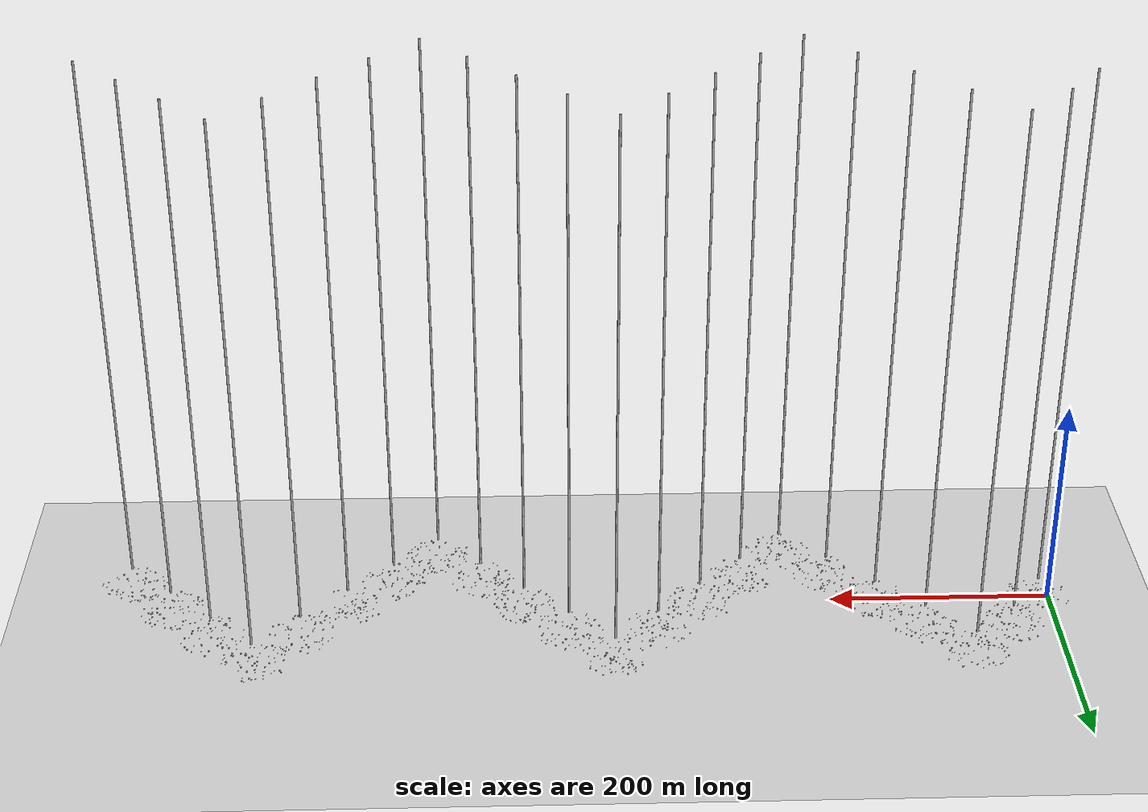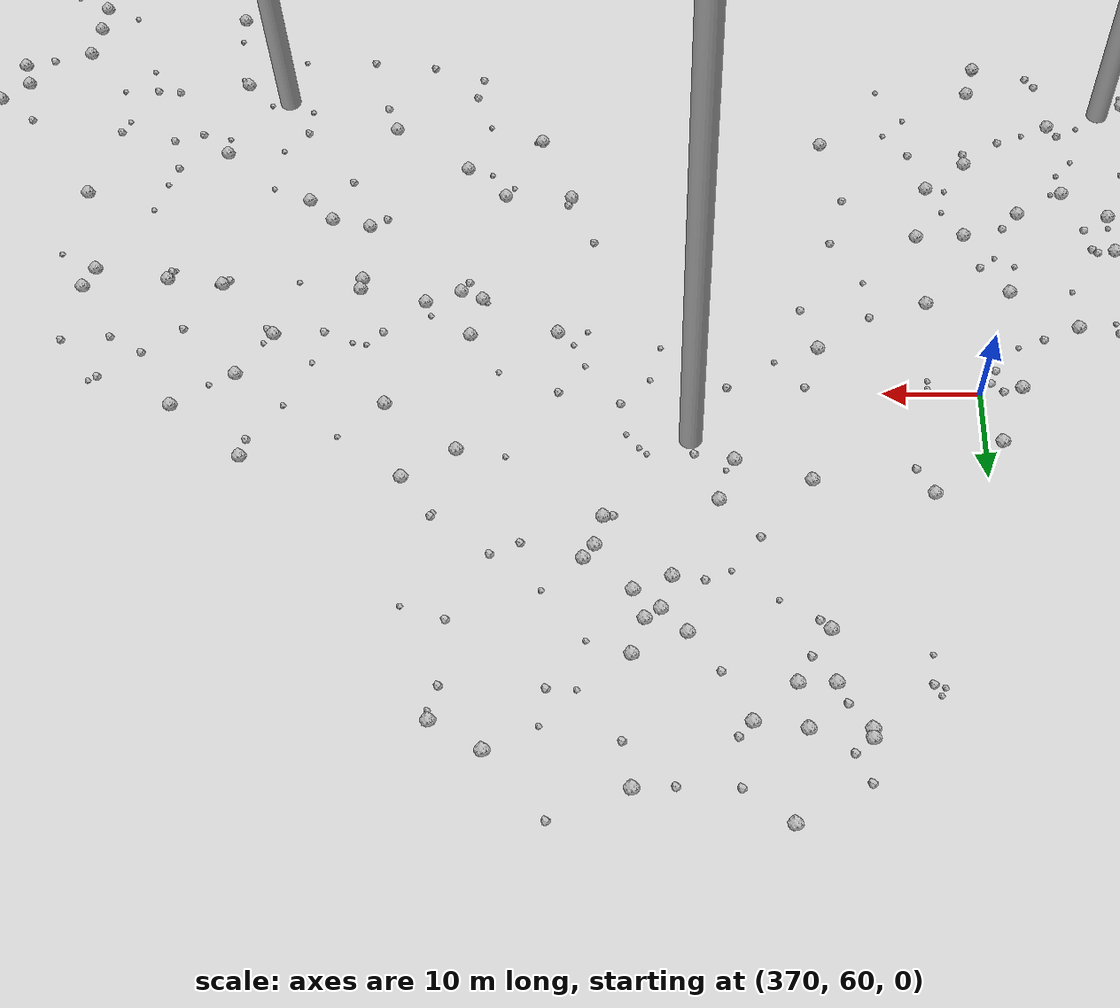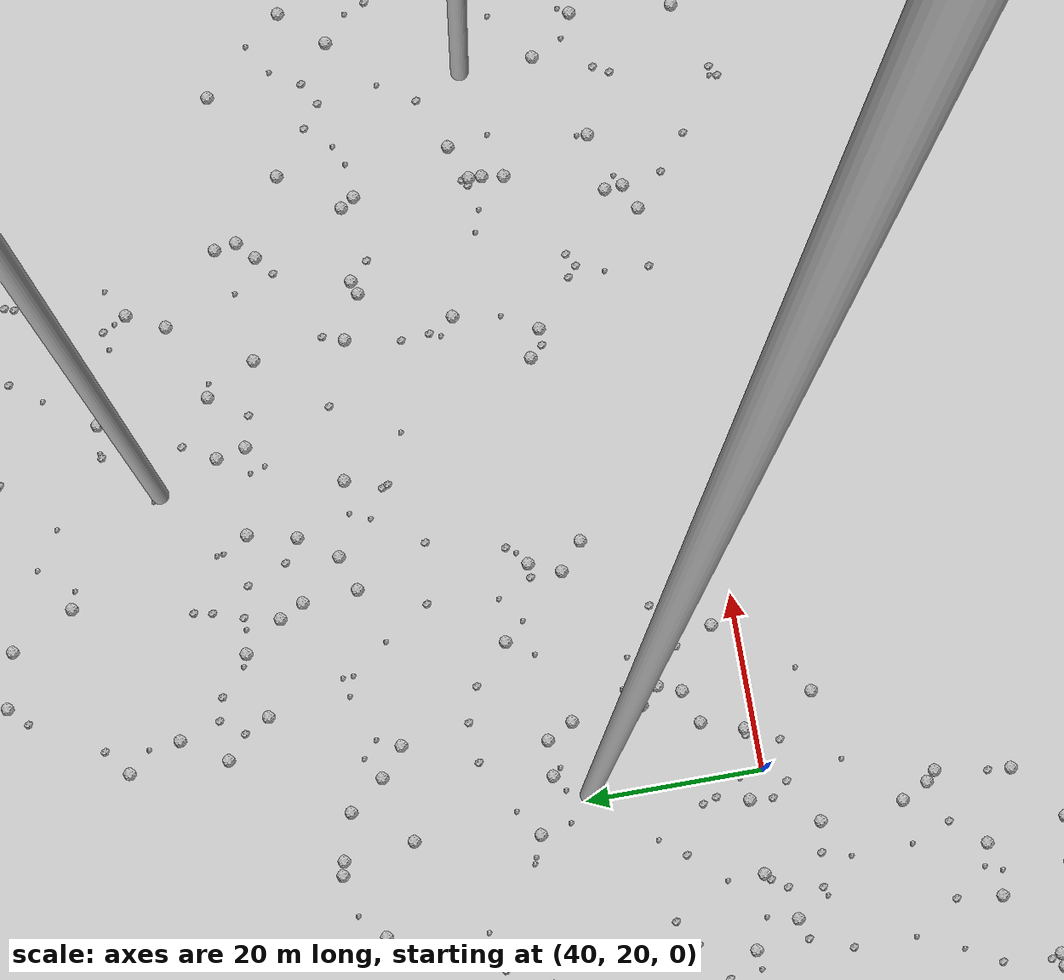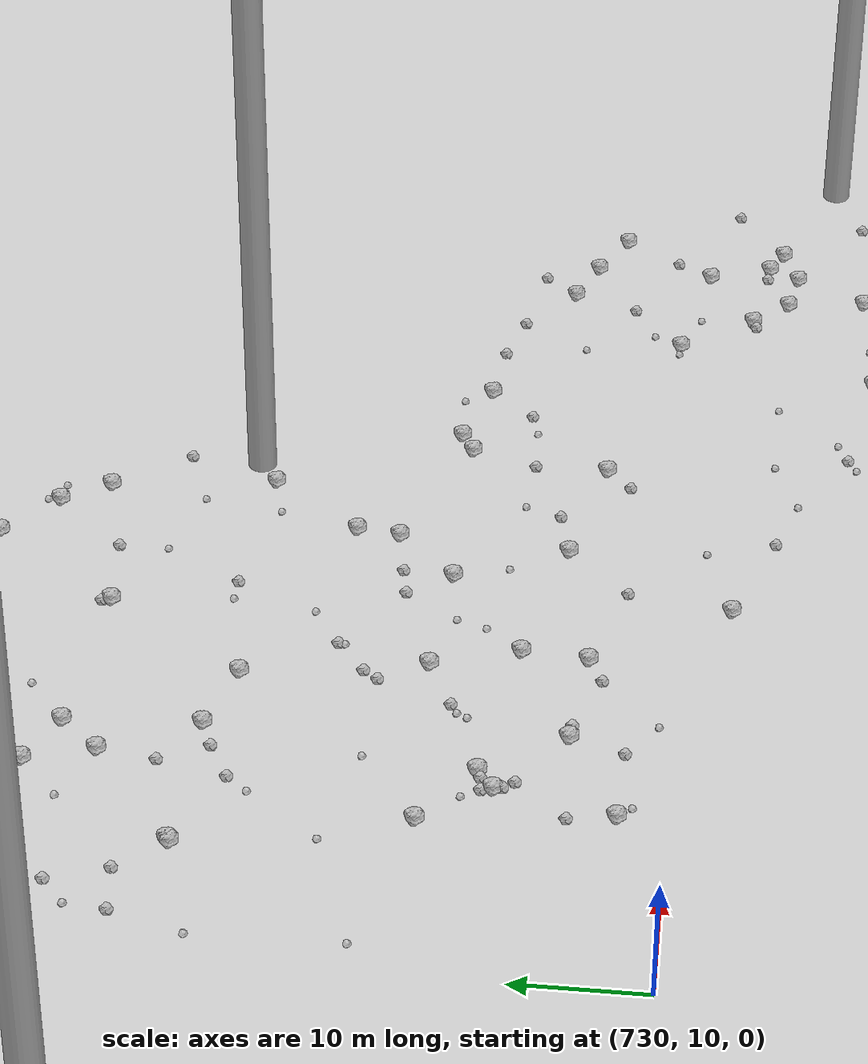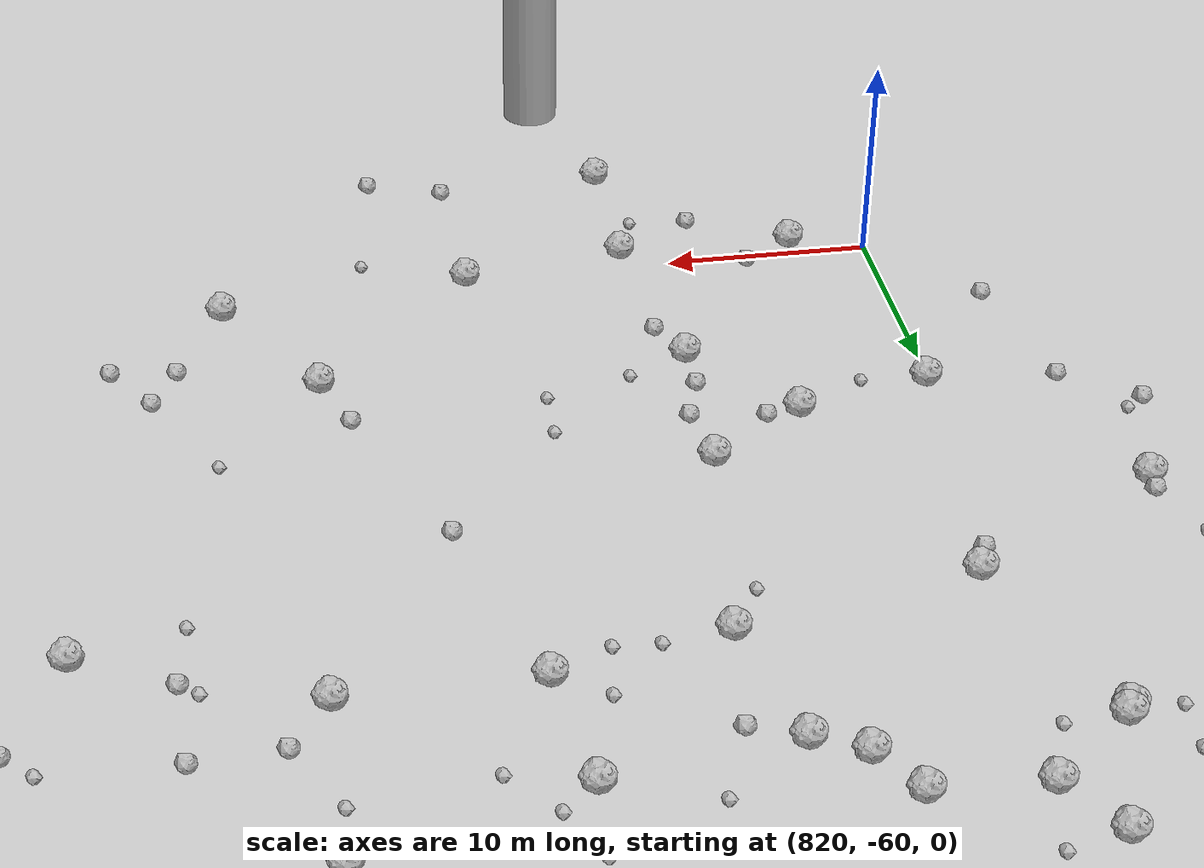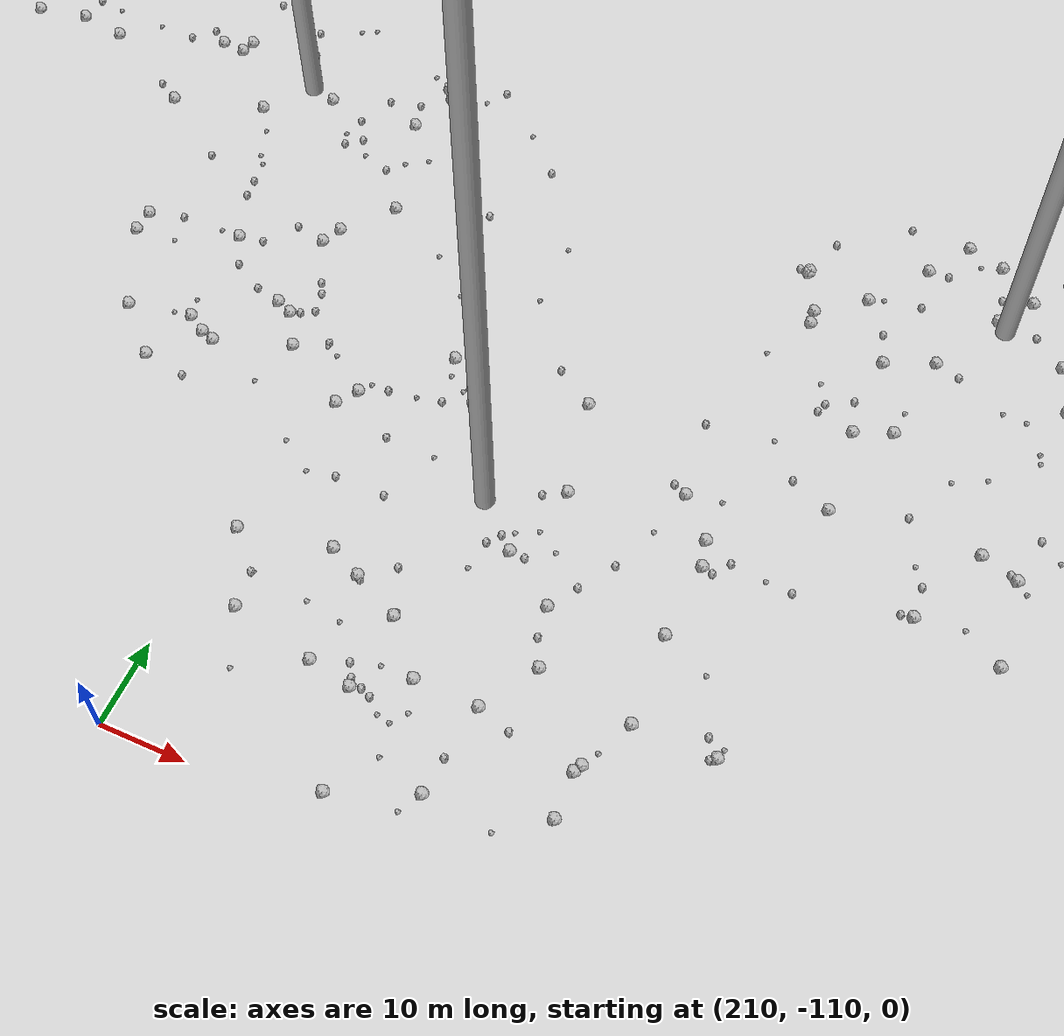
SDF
<sdf version="1.6">
 <world name="default">
  <include><uri>model://custom_ground</uri></include>
  <include><uri>model://sun</uri></include>
  <spherical_coordinates>
   <surface_model>EARTH_WGS84</surface_model>
   <latitude_deg>38.161479</latitude_deg>
   <longitude_deg>-122.454630</longitude_deg>
   <elevation>488.0</elevation>
   <heading_deg>90</heading_deg>
  </spherical_coordinates>
  <model name="rock1_0_0">
   <include><uri>model://rock1</uri><pose>-2.3179333578813264 13.560882379770803 0.5 0 0 0</pose></include>
  </model>
  <model name="rock1_0_1">
   <include><uri>model://rock1</uri><pose>35.42879417177929 -7.32027476160393 0.5 0 0 0</pose></include>
  </model>
  <model name="rock1_0_2">
   <include><uri>model://rock1</uri><pose>21.581545104936787 -3.8465649257423635 0.5 0 0 0</pose></include>
  </model>
  <model name="rock1_0_3">
   <include><uri>model://rock1</uri><pose>14.154558860241679 -9.086605189511875 0.5 0 0 0</pose></include>
  </model>
  <model name="rock1_0_4">
   <include><uri>model://rock1</uri><pose>27.65853363959293 -3.230656400104543 0.5 0 0 0</pose></include>
  </model>
  <model name="rock1_0_5">
   <include><uri>model://rock1</uri><pose>29.094546418056844 -12.289263828323172 0.5 0 0 0</pose></include>
  </model>
  <model name="rock1_0_6">
   <include><uri>model://rock1</uri><pose>3.198670501860949 20.49417938783744 0.5 0 0 0</pose></include>
  </model>
  <model name="rock1_0_7">
   <include><uri>model://rock1</uri><pose>0.24017302983536126 -11.786511357522208 0.5 0 0 0</pose></include>
  </model>
  <model name="rock1_0_8">
   <include><uri>model://rock1</uri><pose>23.03232408651691 19.011693689634235 0.5 0 0 0</pose></include>
  </model>
  <model name="rock1_0_9">
   <include><uri>model://rock1</uri><pose>-5.743131616759921 -4.579162004420187 0.5 0 0 0</pose></include>
  </model>
  <model name="rock1_0_10">
   <include><uri>model://rock1</uri><pose>36.63659674533312 1.1256504691619753 0.5 0 0 0</pose></include>
  </model>
  <model name="rock1_0_11">
   <include><uri>model://rock1</uri><pose>11.309967775192554 13.801374216508073 0.5 0 0 0</pose></include>
  </model>
  <model name="rock1_0_12">
   <include><uri>model://rock1</uri><pose>20.40131893221796 24.209533620573623 0.5 0 0 0</pose></include>
  </model>
  <model name="rock1_0_13">
   <include><uri>model://rock1</uri><pose>33.9714327469201 5.185652311127356 0.5 0 0 0</pose></include>
  </model>
  <model name="rock1_0_14">
   <include><uri>model://rock1</uri><pose>12.68814462211909 -9.212461563729967 0.5 0 0 0</pose></include>
  </model>
  <model name="rock1_0_15">
   <include><uri>model://rock1</uri><pose>-4.495454815119269 -24.41063740558753 0.5 0 0 0</pose></include>
  </model>
  <model name="rock1_0_16">
   <include><uri>model://rock1</uri><pose>-16.2600233374851 -12.978320971455904 0.5 0 0 0</pose></include>
  </model>
  <model name="rock1_0_17">
   <include><uri>model://rock1</uri><pose>-1.277852879630828 21.734546999537862 0.5 0 0 0</pose></include>
  </model>
  <model name="rock1_0_18">
   <include><uri>model://rock1</uri><pose>35.538360486798894 2.1798920704354785 0.5 0 0 0</pose></include>
  </model>
  <model name="rock1_0_19">
   <include><uri>model://rock1</uri><pose>-9.039252355263388 6.359858653403421 0.5 0 0 0</pose></include>
  </model>
  <model name="rock1_0_20">
   <include><uri>model://rock1</uri><pose>-0.7985197492981371 -6.389997465224059 0.5 0 0 0</pose></include>
  </model>
  <model name="rock1_0_21">
   <include><uri>model://rock1</uri><pose>6.826980417559213 -9.06796743425366 0.5 0 0 0</pose></include>
  </model>
  <model name="rock1_0_22">
   <include><uri>model://rock1</uri><pose>-5.800979872090526 -22.76597659327219 0.5 0 0 0</pose></include>
  </model>
  <model name="rock1_0_23">
   <include><uri>model://rock1</uri><pose>7.272387600494859 17.61991123202018 0.5 0 0 0</pose></include>
  </model>
  <model name="rock1_0_24">
   <include><uri>model://rock1</uri><pose>-4.086814954762641 -18.043475079565905 0.5 0 0 0</pose></include>
  </model>
  <model name="rock1_0_25">
   <include><uri>model://rock1</uri><pose>28.602862980748334 21.847904795090813 0.5 0 0 0</pose></include>
  </model>
  <model name="rock1_0_26">
   <include><uri>model://rock1</uri><pose>11.284858371103642 14.621078858084417 0.5 0 0 0</pose></include>
  </model>
  <model name="rock2_0_0">
   <include><uri>model://rock2</uri><pose>0.5463026047976562 -4.640105250451377 0.3 0 0 0</pose></include>
  </model>
  <model name="rock2_0_1">
   <include><uri>model://rock2</uri><pose>26.00869314270973 15.65532478216906 0.3 0 0 0</pose></include>
  </model>
  <model name="rock2_0_2">
   <include><uri>model://rock2</uri><pose>22.154533138157788 1.2678934521407648 0.3 0 0 0</pose></include>
  </model>
  <model name="rock2_0_3">
   <include><uri>model://rock2</uri><pose>13.720953628431367 -7.947625316800611 0.3 0 0 0</pose></include>
  </model>
  <model name="rock2_0_4">
   <include><uri>model://rock2</uri><pose>-7.989690144838635 -10.376225260570607 0.3 0 0 0</pose></include>
  </model>
  <model name="rock2_0_5">
   <include><uri>model://rock2</uri><pose>-0.2792132185209404 -8.091818863086328 0.3 0 0 0</pose></include>
  </model>
  <model name="rock2_0_6">
   <include><uri>model://rock2</uri><pose>27.835957108695894 21.232729382300192 0.3 0 0 0</pose></include>
  </model>
  <model name="rock2_0_7">
   <include><uri>model://rock2</uri><pose>25.739267921812505 -13.394298329485125 0.3 0 0 0</pose></include>
  </model>
  <model name="rock2_0_8">
   <include><uri>model://rock2</uri><pose>4.212172429432936 6.347844747802434 0.3 0 0 0</pose></include>
  </model>
  <model name="rock2_0_9">
   <include><uri>model://rock2</uri><pose>16.18523214950892 -24.677823639163925 0.3 0 0 0</pose></include>
  </model>
  <model name="rock2_0_10">
   <include><uri>model://rock2</uri><pose>18.814040897604322 13.48808018215108 0.3 0 0 0</pose></include>
  </model>
  <model name="rock2_0_11">
   <include><uri>model://rock2</uri><pose>3.3902720927348966 19.188910628032637 0.3 0 0 0</pose></include>
  </model>
  <model name="rock2_0_12">
   <include><uri>model://rock2</uri><pose>30.75988119830958 0.5365990000301863 0.3 0 0 0</pose></include>
  </model>
  <model name="rock2_0_13">
   <include><uri>model://rock2</uri><pose>-15.79756155092216 12.574645919020163 0.3 0 0 0</pose></include>
  </model>
  <model name="rock2_0_14">
   <include><uri>model://rock2</uri><pose>30.734799648009 -20.088682091205484 0.3 0 0 0</pose></include>
  </model>
  <model name="rock2_0_15">
   <include><uri>model://rock2</uri><pose>35.617320170198305 -4.750661294031065 0.3 0 0 0</pose></include>
  </model>
  <model name="rock2_0_16">
   <include><uri>model://rock2</uri><pose>-0.3264794654034695 -6.935395551641818 0.3 0 0 0</pose></include>
  </model>
  <model name="rock2_0_17">
   <include><uri>model://rock2</uri><pose>14.337470174045734 -2.5625191978718327 0.3 0 0 0</pose></include>
  </model>
  <model name="rock2_0_18">
   <include><uri>model://rock2</uri><pose>1.5543590172975144 16.74558341341629 0.3 0 0 0</pose></include>
  </model>
  <model name="rock2_0_19">
   <include><uri>model://rock2</uri><pose>8.976806714405605 -10.399571308252092 0.3 0 0 0</pose></include>
  </model>
  <model name="rock2_0_20">
   <include><uri>model://rock2</uri><pose>0.9514570624525831 7.001598513136983 0.3 0 0 0</pose></include>
  </model>
  <model name="rock2_0_21">
   <include><uri>model://rock2</uri><pose>24.128626590346094 -11.646652468917026 0.3 0 0 0</pose></include>
  </model>
  <model name="rock2_0_22">
   <include><uri>model://rock2</uri><pose>-3.7603999779578317 9.558205634559606 0.3 0 0 0</pose></include>
  </model>
  <model name="rock2_0_23">
   <include><uri>model://rock2</uri><pose>4.071835118737262 -20.104944339322422 0.3 0 0 0</pose></include>
  </model>
  <model name="rock2_0_24">
   <include><uri>model://rock2</uri><pose>29.811284602996906 15.153143464207147 0.3 0 0 0</pose></include>
  </model>
  <model name="rock2_0_25">
   <include><uri>model://rock2</uri><pose>3.100491064064798 -11.308121044746528 0.3 0 0 0</pose></include>
  </model>
  <model name="rock2_0_26">
   <include><uri>model://rock2</uri><pose>0.10401981901976143 -6.083960708332988 0.3 0 0 0</pose></include>
  </model>
  <model name="rock3_0_0">
   <include><uri>model://rock3</uri><pose>16.490904006436367 1.3498611615530116 0.2 0 0 0</pose></include>
  </model>
  <model name="rock3_0_1">
   <include><uri>model://rock3</uri><pose>11.502678683504737 23.762554681959024 0.2 0 0 0</pose></include>
  </model>
  <model name="rock3_0_2">
   <include><uri>model://rock3</uri><pose>11.71104165336104 9.89098389388073 0.2 0 0 0</pose></include>
  </model>
  <model name="rock3_0_3">
   <include><uri>model://rock3</uri><pose>25.10708369541971 -2.5208305269198448 0.2 0 0 0</pose></include>
  </model>
  <model name="rock3_0_4">
   <include><uri>model://rock3</uri><pose>18.738380752692542 6.394485886884183 0.2 0 0 0</pose></include>
  </model>
  <model name="rock3_0_5">
   <include><uri>model://rock3</uri><pose>8.499700348426071 7.86978208536997 0.2 0 0 0</pose></include>
  </model>
  <model name="rock3_0_6">
   <include><uri>model://rock3</uri><pose>18.173485029757586 23.97292818734269 0.2 0 0 0</pose></include>
  </model>
  <model name="rock3_0_7">
   <include><uri>model://rock3</uri><pose>-14.897465942850978 -9.738426541859006 0.2 0 0 0</pose></include>
  </model>
  <model name="rock3_0_8">
   <include><uri>model://rock3</uri><pose>29.2252205034496 -16.04168563881981 0.2 0 0 0</pose></include>
  </model>
  <model name="rock3_0_9">
   <include><uri>model://rock3</uri><pose>31.35086204368308 -15.941731130507753 0.2 0 0 0</pose></include>
  </model>
  <model name="rock3_0_10">
   <include><uri>model://rock3</uri><pose>28.98278875884275 4.963873967362112 0.2 0 0 0</pose></include>
  </model>
  <model name="rock3_0_11">
   <include><uri>model://rock3</uri><pose>28.836766378940574 11.903743935818305 0.2 0 0 0</pose></include>
  </model>
  <model name="rock3_0_12">
   <include><uri>model://rock3</uri><pose>29.181256798631935 -19.61593262853048 0.2 0 0 0</pose></include>
  </model>
  <model name="rock3_0_13">
   <include><uri>model://rock3</uri><pose>1.4867942043570643 3.52497643567299 0.2 0 0 0</pose></include>
  </model>
  <model name="rock3_0_14">
   <include><uri>model://rock3</uri><pose>-0.13153301104572535 -26.350055039452272 0.2 0 0 0</pose></include>
  </model>
  <model name="rock3_0_15">
   <include><uri>model://rock3</uri><pose>6.047401201441172 -20.759246871109454 0.2 0 0 0</pose></include>
  </model>
  <model name="rock3_0_16">
   <include><uri>model://rock3</uri><pose>9.511516969583436 -17.788929663051047 0.2 0 0 0</pose></include>
  </model>
  <model name="rock3_0_17">
   <include><uri>model://rock3</uri><pose>-18.112518220105223 8.82966947689529 0.2 0 0 0</pose></include>
  </model>
  <model name="rock3_0_18">
   <include><uri>model://rock3</uri><pose>-15.991923187417488 -13.094708544352372 0.2 0 0 0</pose></include>
  </model>
  <model name="rock3_0_19">
   <include><uri>model://rock3</uri><pose>-4.3233743782236225 -10.836891108862073 0.2 0 0 0</pose></include>
  </model>
  <model name="rock3_0_20">
   <include><uri>model://rock3</uri><pose>-5.662266002298487 2.0271021558785947 0.2 0 0 0</pose></include>
  </model>
  <model name="rock3_0_21">
   <include><uri>model://rock3</uri><pose>15.544413835715893 -18.33908476693603 0.2 0 0 0</pose></include>
  </model>
  <model name="rock3_0_22">
   <include><uri>model://rock3</uri><pose>27.8103149015241 -16.386412444973868 0.2 0 0 0</pose></include>
  </model>
  <model name="rock3_0_23">
   <include><uri>model://rock3</uri><pose>-7.722771857915582 -14.392285582664117 0.2 0 0 0</pose></include>
  </model>
  <model name="rock3_0_24">
   <include><uri>model://rock3</uri><pose>7.407234007304055 -12.594038010928411 0.2 0 0 0</pose></include>
  </model>
  <model name="rock3_0_25">
   <include><uri>model://rock3</uri><pose>23.77947312079521 22.40909286240194 0.2 0 0 0</pose></include>
  </model>
  <model name="rock3_0_26">
   <include><uri>model://rock3</uri><pose>24.350274445975266 -4.393582506563487 0.2 0 0 0</pose></include>
  </model>
  <model name="rock1_1_0">
   <include><uri>model://rock1</uri><pose>47.44763989165227 42.96826876005569 0.5 0 0 0</pose></include>
  </model>
  <model name="rock1_1_1">
   <include><uri>model://rock1</uri><pose>46.55380104997427 61.893330283744845 0.5 0 0 0</pose></include>
  </model>
  <model name="rock1_1_2">
   <include><uri>model://rock1</uri><pose>43.374192303188046 65.96534356922913 0.5 0 0 0</pose></include>
  </model>
  <model name="rock1_1_3">
   <include><uri>model://rock1</uri><pose>29.03972115283842 64.48170717661375 0.5 0 0 0</pose></include>
  </model>
  <model name="rock1_1_4">
   <include><uri>model://rock1</uri><pose>36.61126120132343 68.07499662354519 0.5 0 0 0</pose></include>
  </model>
  <model name="rock1_1_5">
   <include><uri>model://rock1</uri><pose>46.45358706129601 25.86582692449307 0.5 0 0 0</pose></include>
  </model>
  <model name="rock1_1_6">
   <include><uri>model://rock1</uri><pose>47.79118568106911 13.058911505328165 0.5 0 0 0</pose></include>
  </model>
  <model name="rock1_1_7">
   <include><uri>model://rock1</uri><pose>67.3384800196299 41.68331948398367 0.5 0 0 0</pose></include>
  </model>
  <model name="rock1_1_8">
   <include><uri>model://rock1</uri><pose>49.036913852898486 39.95257304765551 0.5 0 0 0</pose></include>
  </model>
  <model name="rock1_1_9">
   <include><uri>model://rock1</uri><pose>51.35207813736724 29.910116445847557 0.5 0 0 0</pose></include>
  </model>
  <model name="rock1_1_10">
   <include><uri>model://rock1</uri><pose>43.43173048161581 43.09808303491857 0.5 0 0 0</pose></include>
  </model>
  <model name="rock1_1_11">
   <include><uri>model://rock1</uri><pose>38.971684186874185 59.60723098507361 0.5 0 0 0</pose></include>
  </model>
  <model name="rock1_1_12">
   <include><uri>model://rock1</uri><pose>20.82183745379934 62.29009269342083 0.5 0 0 0</pose></include>
  </model>
  <model name="rock1_1_13">
   <include><uri>model://rock1</uri><pose>68.8425929743245 35.48786965559486 0.5 0 0 0</pose></include>
  </model>
  <model name="rock1_1_14">
   <include><uri>model://rock1</uri><pose>49.736240335781105 59.19244874530739 0.5 0 0 0</pose></include>
  </model>
  <model name="rock1_1_15">
   <include><uri>model://rock1</uri><pose>33.279394341304794 14.619444239611708 0.5 0 0 0</pose></include>
  </model>
  <model name="rock1_1_16">
   <include><uri>model://rock1</uri><pose>49.461951492363035 31.966408624217795 0.5 0 0 0</pose></include>
  </model>
  <model name="rock1_1_17">
   <include><uri>model://rock1</uri><pose>65.83217820524192 38.12956313545186 0.5 0 0 0</pose></include>
  </model>
  <model name="rock1_1_18">
   <include><uri>model://rock1</uri><pose>50.27465347764306 27.262759126135602 0.5 0 0 0</pose></include>
  </model>
  <model name="rock1_1_19">
   <include><uri>model://rock1</uri><pose>56.97052117926404 22.73060959694297 0.5 0 0 0</pose></include>
  </model>
  <model name="rock1_1_20">
   <include><uri>model://rock1</uri><pose>59.12725569751134 45.70588830783372 0.5 0 0 0</pose></include>
  </model>
  <model name="rock1_1_21">
   <include><uri>model://rock1</uri><pose>36.99077787395778 21.98488056281603 0.5 0 0 0</pose></include>
  </model>
  <model name="rock1_1_22">
   <include><uri>model://rock1</uri><pose>38.166201747649254 67.68367473726107 0.5 0 0 0</pose></include>
  </model>
  <model name="rock1_1_23">
   <include><uri>model://rock1</uri><pose>20.398877034304732 47.073994653836394 0.5 0 0 0</pose></include>
  </model>
  <model name="rock1_1_24">
   <include><uri>model://rock1</uri><pose>44.9174746579147 21.1351037345793 0.5 0 0 0</pose></include>
  </model>
  <model name="rock1_1_25">
   <include><uri>model://rock1</uri><pose>12.507147261436561 46.902270522743436 0.5 0 0 0</pose></include>
  </model>
  <model name="rock1_1_26">
   <include><uri>model://rock1</uri><pose>37.218370344597645 45.57456536139988 0.5 0 0 0</pose></include>
  </model>
  <model name="rock2_1_0">
   <include><uri>model://rock2</uri><pose>55.314203192448836 27.041985567788583 0.3 0 0 0</pose></include>
  </model>
  <model name="rock2_1_1">
   <include><uri>model://rock2</uri><pose>32.13793236212547 29.973106001232424 0.3 0 0 0</pose></include>
  </model>
  <model name="rock2_1_2">
   <include><uri>model://rock2</uri><pose>37.416241645480014 27.1826820319596 0.3 0 0 0</pose></include>
  </model>
  <model name="rock2_1_3">
   <include><uri>model://rock2</uri><pose>22.93713410528433 44.90863504048274 0.3 0 0 0</pose></include>
  </model>
  <model name="rock2_1_4">
   <include><uri>model://rock2</uri><pose>38.3482495605861 17.557753870922728 0.3 0 0 0</pose></include>
  </model>
  <model name="rock2_1_5">
   <include><uri>model://rock2</uri><pose>20.979576442309757 37.223674922122754 0.3 0 0 0</pose></include>
  </model>
  <model name="rock2_1_6">
   <include><uri>model://rock2</uri><pose>43.05327768063544 17.476156952609827 0.3 0 0 0</pose></include>
  </model>
  <model name="rock2_1_7">
   <include><uri>model://rock2</uri><pose>23.04192441442848 52.03358166957516 0.3 0 0 0</pose></include>
  </model>
  <model name="rock2_1_8">
   <include><uri>model://rock2</uri><pose>64.85547525467379 53.62451363110228 0.3 0 0 0</pose></include>
  </model>
  <model name="rock2_1_9">
   <include><uri>model://rock2</uri><pose>44.19746521121698 21.10767409310983 0.3 0 0 0</pose></include>
  </model>
  <model name="rock2_1_10">
   <include><uri>model://rock2</uri><pose>20.62170317801185 18.230523821674147 0.3 0 0 0</pose></include>
  </model>
  <model name="rock2_1_11">
   <include><uri>model://rock2</uri><pose>20.30092350614835 32.85382749810558 0.3 0 0 0</pose></include>
  </model>
  <model name="rock2_1_12">
   <include><uri>model://rock2</uri><pose>65.7513092309785 41.68445868811993 0.3 0 0 0</pose></include>
  </model>
  <model name="rock2_1_13">
   <include><uri>model://rock2</uri><pose>69.52205438105145 43.84522345802157 0.3 0 0 0</pose></include>
  </model>
  <model name="rock2_1_14">
   <include><uri>model://rock2</uri><pose>46.359529692171975 50.98455241920965 0.3 0 0 0</pose></include>
  </model>
  <model name="rock2_1_15">
   <include><uri>model://rock2</uri><pose>60.32531257504582 29.169207631441846 0.3 0 0 0</pose></include>
  </model>
  <model name="rock2_1_16">
   <include><uri>model://rock2</uri><pose>25.158090916688884 49.54723133945309 0.3 0 0 0</pose></include>
  </model>
  <model name="rock2_1_17">
   <include><uri>model://rock2</uri><pose>13.437451586284627 33.75724140232148 0.3 0 0 0</pose></include>
  </model>
  <model name="rock2_1_18">
   <include><uri>model://rock2</uri><pose>28.757853088322456 66.82753005673919 0.3 0 0 0</pose></include>
  </model>
  <model name="rock2_1_19">
   <include><uri>model://rock2</uri><pose>36.74341929816454 19.408428110938758 0.3 0 0 0</pose></include>
  </model>
  <model name="rock2_1_20">
   <include><uri>model://rock2</uri><pose>26.664162531636187 19.508901223898153 0.3 0 0 0</pose></include>
  </model>
  <model name="rock2_1_21">
   <include><uri>model://rock2</uri><pose>16.169975683566506 39.923476316965974 0.3 0 0 0</pose></include>
  </model>
  <model name="rock2_1_22">
   <include><uri>model://rock2</uri><pose>17.791870791161593 27.66320840004991 0.3 0 0 0</pose></include>
  </model>
  <model name="rock2_1_23">
   <include><uri>model://rock2</uri><pose>50.923948988006266 51.33648964983467 0.3 0 0 0</pose></include>
  </model>
  <model name="rock2_1_24">
   <include><uri>model://rock2</uri><pose>37.93338199646006 25.591217616408148 0.3 0 0 0</pose></include>
  </model>
  <model name="rock2_1_25">
   <include><uri>model://rock2</uri><pose>25.07507584025802 32.47356484222532 0.3 0 0 0</pose></include>
  </model>
  <model name="rock2_1_26">
   <include><uri>model://rock2</uri><pose>54.79146931552592 49.767248233393374 0.3 0 0 0</pose></include>
  </model>
  <model name="rock3_1_0">
   <include><uri>model://rock3</uri><pose>34.33286079591721 32.76263953091156 0.2 0 0 0</pose></include>
  </model>
  <model name="rock3_1_1">
   <include><uri>model://rock3</uri><pose>63.98659139908326 45.57053354694453 0.2 0 0 0</pose></include>
  </model>
  <model name="rock3_1_2">
   <include><uri>model://rock3</uri><pose>40.216644442087805 47.77078756744722 0.2 0 0 0</pose></include>
  </model>
  <model name="rock3_1_3">
   <include><uri>model://rock3</uri><pose>22.08936982160683 30.216625297540524 0.2 0 0 0</pose></include>
  </model>
  <model name="rock3_1_4">
   <include><uri>model://rock3</uri><pose>34.80599106227694 46.5010534680029 0.2 0 0 0</pose></include>
  </model>
  <model name="rock3_1_5">
   <include><uri>model://rock3</uri><pose>28.529918640231056 25.969573351991677 0.2 0 0 0</pose></include>
  </model>
  <model name="rock3_1_6">
   <include><uri>model://rock3</uri><pose>61.08777866516416 43.384181547811366 0.2 0 0 0</pose></include>
  </model>
  <model name="rock3_1_7">
   <include><uri>model://rock3</uri><pose>26.570014911077227 59.352583437193346 0.2 0 0 0</pose></include>
  </model>
  <model name="rock3_1_8">
   <include><uri>model://rock3</uri><pose>44.16524585104756 42.13140283378433 0.2 0 0 0</pose></include>
  </model>
  <model name="rock3_1_9">
   <include><uri>model://rock3</uri><pose>41.57762180353775 41.91349362721654 0.2 0 0 0</pose></include>
  </model>
  <model name="rock3_1_10">
   <include><uri>model://rock3</uri><pose>31.82453253472215 67.16161857417494 0.2 0 0 0</pose></include>
  </model>
  <model name="rock3_1_11">
   <include><uri>model://rock3</uri><pose>58.840006064337004 28.602100606635027 0.2 0 0 0</pose></include>
  </model>
  <model name="rock3_1_12">
   <include><uri>model://rock3</uri><pose>68.73132738793196 42.76649492805007 0.2 0 0 0</pose></include>
  </model>
  <model name="rock3_1_13">
   <include><uri>model://rock3</uri><pose>34.11364997202836 46.787550302305924 0.2 0 0 0</pose></include>
  </model>
  <model name="rock3_1_14">
   <include><uri>model://rock3</uri><pose>59.822052745915705 23.935048472061716 0.2 0 0 0</pose></include>
  </model>
  <model name="rock3_1_15">
   <include><uri>model://rock3</uri><pose>21.15224776217842 34.959524320004746 0.2 0 0 0</pose></include>
  </model>
  <model name="rock3_1_16">
   <include><uri>model://rock3</uri><pose>50.82838240125382 61.82752821438994 0.2 0 0 0</pose></include>
  </model>
  <model name="rock3_1_17">
   <include><uri>model://rock3</uri><pose>24.95433117169764 15.27391565105196 0.2 0 0 0</pose></include>
  </model>
  <model name="rock3_1_18">
   <include><uri>model://rock3</uri><pose>39.50351469326158 22.561710443720735 0.2 0 0 0</pose></include>
  </model>
  <model name="rock3_1_19">
   <include><uri>model://rock3</uri><pose>55.01808446116185 32.61571736201865 0.2 0 0 0</pose></include>
  </model>
  <model name="rock3_1_20">
   <include><uri>model://rock3</uri><pose>57.1403493904009 42.696490045696436 0.2 0 0 0</pose></include>
  </model>
  <model name="rock3_1_21">
   <include><uri>model://rock3</uri><pose>37.89444430570417 42.01607614203014 0.2 0 0 0</pose></include>
  </model>
  <model name="rock3_1_22">
   <include><uri>model://rock3</uri><pose>51.59139295148502 33.76490307674884 0.2 0 0 0</pose></include>
  </model>
  <model name="rock3_1_23">
   <include><uri>model://rock3</uri><pose>50.640834538370555 14.319470831562068 0.2 0 0 0</pose></include>
  </model>
  <model name="rock3_1_24">
   <include><uri>model://rock3</uri><pose>39.667136130148535 11.065032025911638 0.2 0 0 0</pose></include>
  </model>
  <model name="rock3_1_25">
   <include><uri>model://rock3</uri><pose>27.476586967008313 53.15905126310675 0.2 0 0 0</pose></include>
  </model>
  <model name="rock3_1_26">
   <include><uri>model://rock3</uri><pose>48.987405693899824 63.50889172304816 0.2 0 0 0</pose></include>
  </model>
  <model name="rock1_2_0">
   <include><uri>model://rock1</uri><pose>67.7992649475986 60.98831708419295 0.5 0 0 0</pose></include>
  </model>
  <model name="rock1_2_1">
   <include><uri>model://rock1</uri><pose>102.78904938940173 81.33772502122757 0.5 0 0 0</pose></include>
  </model>
  <model name="rock1_2_2">
   <include><uri>model://rock1</uri><pose>51.935266759329394 89.55382025964582 0.5 0 0 0</pose></include>
  </model>
  <model name="rock1_2_3">
   <include><uri>model://rock1</uri><pose>81.84824819162912 102.25857192717481 0.5 0 0 0</pose></include>
  </model>
  <model name="rock1_2_4">
   <include><uri>model://rock1</uri><pose>95.56342289879657 105.26910286257419 0.5 0 0 0</pose></include>
  </model>
  <model name="rock1_2_5">
   <include><uri>model://rock1</uri><pose>61.479324821665585 101.77595162635919 0.5 0 0 0</pose></include>
  </model>
  <model name="rock1_2_6">
   <include><uri>model://rock1</uri><pose>67.6236324027325 100.14110059017459 0.5 0 0 0</pose></include>
  </model>
  <model name="rock1_2_7">
   <include><uri>model://rock1</uri><pose>92.05466156433852 73.84687365330393 0.5 0 0 0</pose></include>
  </model>
  <model name="rock1_2_8">
   <include><uri>model://rock1</uri><pose>80.13048596523535 60.34842564738714 0.5 0 0 0</pose></include>
  </model>
  <model name="rock1_2_9">
   <include><uri>model://rock1</uri><pose>55.49880069002928 73.22233130527171 0.5 0 0 0</pose></include>
  </model>
  <model name="rock1_2_10">
   <include><uri>model://rock1</uri><pose>67.4139663340718 67.28292431592882 0.5 0 0 0</pose></include>
  </model>
  <model name="rock1_2_11">
   <include><uri>model://rock1</uri><pose>95.26484627711959 68.05103069562574 0.5 0 0 0</pose></include>
  </model>
  <model name="rock1_2_12">
   <include><uri>model://rock1</uri><pose>62.87443224376435 74.46308696822516 0.5 0 0 0</pose></include>
  </model>
  <model name="rock1_2_13">
   <include><uri>model://rock1</uri><pose>54.58530585259458 83.40353112701573 0.5 0 0 0</pose></include>
  </model>
  <model name="rock1_2_14">
   <include><uri>model://rock1</uri><pose>66.06164297991032 70.03896468789306 0.5 0 0 0</pose></include>
  </model>
  <model name="rock1_2_15">
   <include><uri>model://rock1</uri><pose>85.09343098860862 74.03194639923029 0.5 0 0 0</pose></include>
  </model>
  <model name="rock1_2_16">
   <include><uri>model://rock1</uri><pose>76.00455470696052 72.13944669741306 0.5 0 0 0</pose></include>
  </model>
  <model name="rock1_2_17">
   <include><uri>model://rock1</uri><pose>71.69463526211626 101.98464837010495 0.5 0 0 0</pose></include>
  </model>
  <model name="rock1_2_18">
   <include><uri>model://rock1</uri><pose>71.22166965340189 92.82349056268156 0.5 0 0 0</pose></include>
  </model>
  <model name="rock1_2_19">
   <include><uri>model://rock1</uri><pose>51.47036104913432 78.41292601548774 0.5 0 0 0</pose></include>
  </model>
  <model name="rock1_2_20">
   <include><uri>model://rock1</uri><pose>71.79468979576279 62.38781838172298 0.5 0 0 0</pose></include>
  </model>
  <model name="rock1_2_21">
   <include><uri>model://rock1</uri><pose>108.35476002117436 70.23077770189582 0.5 0 0 0</pose></include>
  </model>
  <model name="rock1_2_22">
   <include><uri>model://rock1</uri><pose>74.70958862318753 66.62647819819739 0.5 0 0 0</pose></include>
  </model>
  <model name="rock1_2_23">
   <include><uri>model://rock1</uri><pose>95.78614778453405 57.56715612549465 0.5 0 0 0</pose></include>
  </model>
  <model name="rock1_2_24">
   <include><uri>model://rock1</uri><pose>85.78348046176944 70.62992880823732 0.5 0 0 0</pose></include>
  </model>
  <model name="rock1_2_25">
   <include><uri>model://rock1</uri><pose>91.1099415725353 86.5416931691751 0.5 0 0 0</pose></include>
  </model>
  <model name="rock1_2_26">
   <include><uri>model://rock1</uri><pose>100.72383835800457 77.11251511356988 0.5 0 0 0</pose></include>
  </model>
  <model name="rock2_2_0">
   <include><uri>model://rock2</uri><pose>95.00346489093643 85.91408969631102 0.3 0 0 0</pose></include>
  </model>
  <model name="rock2_2_1">
   <include><uri>model://rock2</uri><pose>86.07360111759792 98.73082356190471 0.3 0 0 0</pose></include>
  </model>
  <model name="rock2_2_2">
   <include><uri>model://rock2</uri><pose>78.57637963676112 56.28730857759436 0.3 0 0 0</pose></include>
  </model>
  <model name="rock2_2_3">
   <include><uri>model://rock2</uri><pose>58.53979759217912 77.93250014933501 0.3 0 0 0</pose></include>
  </model>
  <model name="rock2_2_4">
   <include><uri>model://rock2</uri><pose>78.83736623618245 55.639520755626705 0.3 0 0 0</pose></include>
  </model>
  <model name="rock2_2_5">
   <include><uri>model://rock2</uri><pose>68.3893472971414 79.49378363357849 0.3 0 0 0</pose></include>
  </model>
  <model name="rock2_2_6">
   <include><uri>model://rock2</uri><pose>105.62295591506943 93.59181211259849 0.3 0 0 0</pose></include>
  </model>
  <model name="rock2_2_7">
   <include><uri>model://rock2</uri><pose>86.33607015465446 98.50921575479333 0.3 0 0 0</pose></include>
  </model>
  <model name="rock2_2_8">
   <include><uri>model://rock2</uri><pose>96.56450016564344 60.0096265209865 0.3 0 0 0</pose></include>
  </model>
  <model name="rock2_2_9">
   <include><uri>model://rock2</uri><pose>71.69363027138459 52.596890351217255 0.3 0 0 0</pose></include>
  </model>
  <model name="rock2_2_10">
   <include><uri>model://rock2</uri><pose>89.26241002484284 69.66424862811292 0.3 0 0 0</pose></include>
  </model>
  <model name="rock2_2_11">
   <include><uri>model://rock2</uri><pose>105.96898096305392 94.65006425627172 0.3 0 0 0</pose></include>
  </model>
  <model name="rock2_2_12">
   <include><uri>model://rock2</uri><pose>77.63938752212351 107.16285031014732 0.3 0 0 0</pose></include>
  </model>
  <model name="rock2_2_13">
   <include><uri>model://rock2</uri><pose>101.38920863615107 84.15527384220468 0.3 0 0 0</pose></include>
  </model>
  <model name="rock2_2_14">
   <include><uri>model://rock2</uri><pose>94.2569348924191 103.44775159305644 0.3 0 0 0</pose></include>
  </model>
  <model name="rock2_2_15">
   <include><uri>model://rock2</uri><pose>87.39765148240315 86.70673434731363 0.3 0 0 0</pose></include>
  </model>
  <model name="rock2_2_16">
   <include><uri>model://rock2</uri><pose>55.97426741619277 78.70445101239692 0.3 0 0 0</pose></include>
  </model>
  <model name="rock2_2_17">
   <include><uri>model://rock2</uri><pose>72.14763763488963 68.41034768023704 0.3 0 0 0</pose></include>
  </model>
  <model name="rock2_2_18">
   <include><uri>model://rock2</uri><pose>87.04654442756964 77.62117559240161 0.3 0 0 0</pose></include>
  </model>
  <model name="rock2_2_19">
   <include><uri>model://rock2</uri><pose>66.902168511062 74.053417200572 0.3 0 0 0</pose></include>
  </model>
  <model name="rock2_2_20">
   <include><uri>model://rock2</uri><pose>59.33098814594184 99.80310634627031 0.3 0 0 0</pose></include>
  </model>
  <model name="rock2_2_21">
   <include><uri>model://rock2</uri><pose>70.37431136290076 72.97141030976584 0.3 0 0 0</pose></include>
  </model>
  <model name="rock2_2_22">
   <include><uri>model://rock2</uri><pose>54.05754615486876 76.13488665426843 0.3 0 0 0</pose></include>
  </model>
  <model name="rock2_2_23">
   <include><uri>model://rock2</uri><pose>88.68833774228433 60.56586721887064 0.3 0 0 0</pose></include>
  </model>
  <model name="rock2_2_24">
   <include><uri>model://rock2</uri><pose>97.34728241205234 95.60142877528789 0.3 0 0 0</pose></include>
  </model>
  <model name="rock2_2_25">
   <include><uri>model://rock2</uri><pose>54.83326279035538 91.88887468822651 0.3 0 0 0</pose></include>
  </model>
  <model name="rock2_2_26">
   <include><uri>model://rock2</uri><pose>68.00498067644223 77.41800068847341 0.3 0 0 0</pose></include>
  </model>
  <model name="rock3_2_0">
   <include><uri>model://rock3</uri><pose>58.329688742774614 63.10413544596802 0.2 0 0 0</pose></include>
  </model>
  <model name="rock3_2_1">
   <include><uri>model://rock3</uri><pose>56.12795025086295 63.87399424615447 0.2 0 0 0</pose></include>
  </model>
  <model name="rock3_2_2">
   <include><uri>model://rock3</uri><pose>73.12764788919527 92.12915420398076 0.2 0 0 0</pose></include>
  </model>
  <model name="rock3_2_3">
   <include><uri>model://rock3</uri><pose>58.27278038765747 64.29690927319527 0.2 0 0 0</pose></include>
  </model>
  <model name="rock3_2_4">
   <include><uri>model://rock3</uri><pose>99.31349171776635 83.77459674033277 0.2 0 0 0</pose></include>
  </model>
  <model name="rock3_2_5">
   <include><uri>model://rock3</uri><pose>82.75688650503494 70.54613602056881 0.2 0 0 0</pose></include>
  </model>
  <model name="rock3_2_6">
   <include><uri>model://rock3</uri><pose>84.36573217946912 53.1256155560817 0.2 0 0 0</pose></include>
  </model>
  <model name="rock3_2_7">
   <include><uri>model://rock3</uri><pose>83.29324648905725 68.84310698492357 0.2 0 0 0</pose></include>
  </model>
  <model name="rock3_2_8">
   <include><uri>model://rock3</uri><pose>75.36378485313975 58.132691728377196 0.2 0 0 0</pose></include>
  </model>
  <model name="rock3_2_9">
   <include><uri>model://rock3</uri><pose>65.5148065173449 73.996776550806 0.2 0 0 0</pose></include>
  </model>
  <model name="rock3_2_10">
   <include><uri>model://rock3</uri><pose>61.469309423508875 74.98464755789409 0.2 0 0 0</pose></include>
  </model>
  <model name="rock3_2_11">
   <include><uri>model://rock3</uri><pose>93.55263558847491 73.46286361768426 0.2 0 0 0</pose></include>
  </model>
  <model name="rock3_2_12">
   <include><uri>model://rock3</uri><pose>97.33132595496801 104.41967029045949 0.2 0 0 0</pose></include>
  </model>
  <model name="rock3_2_13">
   <include><uri>model://rock3</uri><pose>80.30569485881593 92.99280029662914 0.2 0 0 0</pose></include>
  </model>
  <model name="rock3_2_14">
   <include><uri>model://rock3</uri><pose>54.15334690348724 86.97213492188615 0.2 0 0 0</pose></include>
  </model>
  <model name="rock3_2_15">
   <include><uri>model://rock3</uri><pose>66.3389466931106 103.58479470032523 0.2 0 0 0</pose></include>
  </model>
  <model name="rock3_2_16">
   <include><uri>model://rock3</uri><pose>81.53640847475475 81.71272091348027 0.2 0 0 0</pose></include>
  </model>
  <model name="rock3_2_17">
   <include><uri>model://rock3</uri><pose>103.06951387886961 68.82008260093785 0.2 0 0 0</pose></include>
  </model>
  <model name="rock3_2_18">
   <include><uri>model://rock3</uri><pose>102.01295224788826 82.73237705481412 0.2 0 0 0</pose></include>
  </model>
  <model name="rock3_2_19">
   <include><uri>model://rock3</uri><pose>76.34761267292234 60.40920484253148 0.2 0 0 0</pose></include>
  </model>
  <model name="rock3_2_20">
   <include><uri>model://rock3</uri><pose>94.79629733500161 92.16159932801709 0.2 0 0 0</pose></include>
  </model>
  <model name="rock3_2_21">
   <include><uri>model://rock3</uri><pose>74.33212694669984 75.06206505120517 0.2 0 0 0</pose></include>
  </model>
  <model name="rock3_2_22">
   <include><uri>model://rock3</uri><pose>74.26213477517418 75.81224503132127 0.2 0 0 0</pose></include>
  </model>
  <model name="rock3_2_23">
   <include><uri>model://rock3</uri><pose>76.12962868422028 95.9121840024416 0.2 0 0 0</pose></include>
  </model>
  <model name="rock3_2_24">
   <include><uri>model://rock3</uri><pose>61.45068924353152 58.85223945586538 0.2 0 0 0</pose></include>
  </model>
  <model name="rock3_2_25">
   <include><uri>model://rock3</uri><pose>87.89025823989928 86.77923485121141 0.2 0 0 0</pose></include>
  </model>
  <model name="rock3_2_26">
   <include><uri>model://rock3</uri><pose>105.870447440155 83.20901857585898 0.2 0 0 0</pose></include>
  </model>
  <model name="rock1_3_0">
   <include><uri>model://rock1</uri><pose>104.75505347595042 22.439833705545993 0.5 0 0 0</pose></include>
  </model>
  <model name="rock1_3_1">
   <include><uri>model://rock1</uri><pose>123.78961231574627 31.161362050627773 0.5 0 0 0</pose></include>
  </model>
  <model name="rock1_3_2">
   <include><uri>model://rock1</uri><pose>115.35743912282356 42.31671345766525 0.5 0 0 0</pose></include>
  </model>
  <model name="rock1_3_3">
   <include><uri>model://rock1</uri><pose>100.67540919410445 55.205934191600406 0.5 0 0 0</pose></include>
  </model>
  <model name="rock1_3_4">
   <include><uri>model://rock1</uri><pose>111.38690040503111 39.15825269230602 0.5 0 0 0</pose></include>
  </model>
  <model name="rock1_3_5">
   <include><uri>model://rock1</uri><pose>138.12195894658055 25.677062820834138 0.5 0 0 0</pose></include>
  </model>
  <model name="rock1_3_6">
   <include><uri>model://rock1</uri><pose>96.28551486031466 45.15381333196375 0.5 0 0 0</pose></include>
  </model>
  <model name="rock1_3_7">
   <include><uri>model://rock1</uri><pose>107.62604548998584 23.701441005061092 0.5 0 0 0</pose></include>
  </model>
  <model name="rock1_3_8">
   <include><uri>model://rock1</uri><pose>107.4917729090495 25.74405775392387 0.5 0 0 0</pose></include>
  </model>
  <model name="rock1_3_9">
   <include><uri>model://rock1</uri><pose>110.9919971714288 36.69126252836428 0.5 0 0 0</pose></include>
  </model>
  <model name="rock1_3_10">
   <include><uri>model://rock1</uri><pose>111.47232549851631 40.618866625453265 0.5 0 0 0</pose></include>
  </model>
  <model name="rock1_3_11">
   <include><uri>model://rock1</uri><pose>113.97093025141957 26.566621037508888 0.5 0 0 0</pose></include>
  </model>
  <model name="rock1_3_12">
   <include><uri>model://rock1</uri><pose>106.73500343145034 65.8672447767658 0.5 0 0 0</pose></include>
  </model>
  <model name="rock1_3_13">
   <include><uri>model://rock1</uri><pose>126.95527579866453 14.683840642518959 0.5 0 0 0</pose></include>
  </model>
  <model name="rock1_3_14">
   <include><uri>model://rock1</uri><pose>115.41202403765513 61.90041288893542 0.5 0 0 0</pose></include>
  </model>
  <model name="rock1_3_15">
   <include><uri>model://rock1</uri><pose>110.60825517149021 55.352751170268306 0.5 0 0 0</pose></include>
  </model>
  <model name="rock1_3_16">
   <include><uri>model://rock1</uri><pose>108.75070475403874 67.70854714809133 0.5 0 0 0</pose></include>
  </model>
  <model name="rock1_3_17">
   <include><uri>model://rock1</uri><pose>111.5860535308869 53.79734207240785 0.5 0 0 0</pose></include>
  </model>
  <model name="rock1_3_18">
   <include><uri>model://rock1</uri><pose>129.45660193756385 53.871072697381976 0.5 0 0 0</pose></include>
  </model>
  <model name="rock1_3_19">
   <include><uri>model://rock1</uri><pose>90.12666548634617 37.30689160104003 0.5 0 0 0</pose></include>
  </model>
  <model name="rock1_3_20">
   <include><uri>model://rock1</uri><pose>134.98358168447365 39.83687462829373 0.5 0 0 0</pose></include>
  </model>
  <model name="rock1_3_21">
   <include><uri>model://rock1</uri><pose>133.6967956101083 58.61802711296322 0.5 0 0 0</pose></include>
  </model>
  <model name="rock1_3_22">
   <include><uri>model://rock1</uri><pose>102.21052587141278 55.724519101967125 0.5 0 0 0</pose></include>
  </model>
  <model name="rock1_3_23">
   <include><uri>model://rock1</uri><pose>93.21343534279059 35.819966336526676 0.5 0 0 0</pose></include>
  </model>
  <model name="rock1_3_24">
   <include><uri>model://rock1</uri><pose>125.6232591053236 68.07362073983406 0.5 0 0 0</pose></include>
  </model>
  <model name="rock1_3_25">
   <include><uri>model://rock1</uri><pose>146.18714916956353 47.46028110786112 0.5 0 0 0</pose></include>
  </model>
  <model name="rock1_3_26">
   <include><uri>model://rock1</uri><pose>128.02384342408902 26.171050619684415 0.5 0 0 0</pose></include>
  </model>
  <model name="rock2_3_0">
   <include><uri>model://rock2</uri><pose>110.65166690019964 40.82714030657371 0.3 0 0 0</pose></include>
  </model>
  <model name="rock2_3_1">
   <include><uri>model://rock2</uri><pose>120.24403680724231 57.9445252995024 0.3 0 0 0</pose></include>
  </model>
  <model name="rock2_3_2">
   <include><uri>model://rock2</uri><pose>137.10738948265168 20.26920315269416 0.3 0 0 0</pose></include>
  </model>
  <model name="rock2_3_3">
   <include><uri>model://rock2</uri><pose>104.21701161090935 53.569562898261466 0.3 0 0 0</pose></include>
  </model>
  <model name="rock2_3_4">
   <include><uri>model://rock2</uri><pose>104.61183002623878 64.21821447263689 0.3 0 0 0</pose></include>
  </model>
  <model name="rock2_3_5">
   <include><uri>model://rock2</uri><pose>111.36939891049823 41.378229123345264 0.3 0 0 0</pose></include>
  </model>
  <model name="rock2_3_6">
   <include><uri>model://rock2</uri><pose>121.51361021243876 24.615094363426813 0.3 0 0 0</pose></include>
  </model>
  <model name="rock2_3_7">
   <include><uri>model://rock2</uri><pose>125.31747940850471 57.3936708868139 0.3 0 0 0</pose></include>
  </model>
  <model name="rock2_3_8">
   <include><uri>model://rock2</uri><pose>133.27532226241962 48.789234868929555 0.3 0 0 0</pose></include>
  </model>
  <model name="rock2_3_9">
   <include><uri>model://rock2</uri><pose>94.82462866555494 48.073272810525246 0.3 0 0 0</pose></include>
  </model>
  <model name="rock2_3_10">
   <include><uri>model://rock2</uri><pose>98.3692065301807 31.537532923271186 0.3 0 0 0</pose></include>
  </model>
  <model name="rock2_3_11">
   <include><uri>model://rock2</uri><pose>121.18629101372207 44.918504883639805 0.3 0 0 0</pose></include>
  </model>
  <model name="rock2_3_12">
   <include><uri>model://rock2</uri><pose>91.33527793157708 35.83084793516353 0.3 0 0 0</pose></include>
  </model>
  <model name="rock2_3_13">
   <include><uri>model://rock2</uri><pose>120.61058152388209 22.848825161128143 0.3 0 0 0</pose></include>
  </model>
  <model name="rock2_3_14">
   <include><uri>model://rock2</uri><pose>130.42752182057035 12.693764766248632 0.3 0 0 0</pose></include>
  </model>
  <model name="rock2_3_15">
   <include><uri>model://rock2</uri><pose>118.1169121528546 10.953978670377474 0.3 0 0 0</pose></include>
  </model>
  <model name="rock2_3_16">
   <include><uri>model://rock2</uri><pose>137.72892146047974 55.686065932394264 0.3 0 0 0</pose></include>
  </model>
  <model name="rock2_3_17">
   <include><uri>model://rock2</uri><pose>122.78957339138381 55.954958902647384 0.3 0 0 0</pose></include>
  </model>
  <model name="rock2_3_18">
   <include><uri>model://rock2</uri><pose>98.07223293042513 22.38014925477389 0.3 0 0 0</pose></include>
  </model>
  <model name="rock2_3_19">
   <include><uri>model://rock2</uri><pose>94.61006635987472 51.30941071352489 0.3 0 0 0</pose></include>
  </model>
  <model name="rock2_3_20">
   <include><uri>model://rock2</uri><pose>108.40278464929165 19.169814792244715 0.3 0 0 0</pose></include>
  </model>
  <model name="rock2_3_21">
   <include><uri>model://rock2</uri><pose>101.02475367934656 31.35486992135562 0.3 0 0 0</pose></include>
  </model>
  <model name="rock2_3_22">
   <include><uri>model://rock2</uri><pose>99.52125914862336 30.517975586946093 0.3 0 0 0</pose></include>
  </model>
  <model name="rock2_3_23">
   <include><uri>model://rock2</uri><pose>119.28968959012519 11.696456534457198 0.3 0 0 0</pose></include>
  </model>
  <model name="rock2_3_24">
   <include><uri>model://rock2</uri><pose>112.32660660633984 15.908635190565455 0.3 0 0 0</pose></include>
  </model>
  <model name="rock2_3_25">
   <include><uri>model://rock2</uri><pose>149.5759808166922 35.14796977920992 0.3 0 0 0</pose></include>
  </model>
  <model name="rock2_3_26">
   <include><uri>model://rock2</uri><pose>146.61304364328828 49.81742286433834 0.3 0 0 0</pose></include>
  </model>
  <model name="rock3_3_0">
   <include><uri>model://rock3</uri><pose>129.29008960274263 35.319607039944486 0.2 0 0 0</pose></include>
  </model>
  <model name="rock3_3_1">
   <include><uri>model://rock3</uri><pose>115.957762156462 37.686845743695116 0.2 0 0 0</pose></include>
  </model>
  <model name="rock3_3_2">
   <include><uri>model://rock3</uri><pose>127.23979927827932 60.72320951933958 0.2 0 0 0</pose></include>
  </model>
  <model name="rock3_3_3">
   <include><uri>model://rock3</uri><pose>118.26533045020767 11.787651603621377 0.2 0 0 0</pose></include>
  </model>
  <model name="rock3_3_4">
   <include><uri>model://rock3</uri><pose>136.03253992334723 46.6176181194615 0.2 0 0 0</pose></include>
  </model>
  <model name="rock3_3_5">
   <include><uri>model://rock3</uri><pose>147.7568798961209 36.594753950379044 0.2 0 0 0</pose></include>
  </model>
  <model name="rock3_3_6">
   <include><uri>model://rock3</uri><pose>135.6009040047276 58.04677457684568 0.2 0 0 0</pose></include>
  </model>
  <model name="rock3_3_7">
   <include><uri>model://rock3</uri><pose>115.40958267391332 54.034170098979175 0.2 0 0 0</pose></include>
  </model>
  <model name="rock3_3_8">
   <include><uri>model://rock3</uri><pose>108.85502600736864 24.45206979472975 0.2 0 0 0</pose></include>
  </model>
  <model name="rock3_3_9">
   <include><uri>model://rock3</uri><pose>145.26590594378303 32.25552618083242 0.2 0 0 0</pose></include>
  </model>
  <model name="rock3_3_10">
   <include><uri>model://rock3</uri><pose>117.63828300578547 55.11732665583771 0.2 0 0 0</pose></include>
  </model>
  <model name="rock3_3_11">
   <include><uri>model://rock3</uri><pose>128.76588963216855 27.374127390531623 0.2 0 0 0</pose></include>
  </model>
  <model name="rock3_3_12">
   <include><uri>model://rock3</uri><pose>107.69562953446672 40.110711197250886 0.2 0 0 0</pose></include>
  </model>
  <model name="rock3_3_13">
   <include><uri>model://rock3</uri><pose>149.16695095217239 40.35382545927291 0.2 0 0 0</pose></include>
  </model>
  <model name="rock3_3_14">
   <include><uri>model://rock3</uri><pose>137.87282504825885 55.756900868901155 0.2 0 0 0</pose></include>
  </model>
  <model name="rock3_3_15">
   <include><uri>model://rock3</uri><pose>98.35402460333393 27.360742980228572 0.2 0 0 0</pose></include>
  </model>
  <model name="rock3_3_16">
   <include><uri>model://rock3</uri><pose>131.10123724103627 25.66136231041341 0.2 0 0 0</pose></include>
  </model>
  <model name="rock3_3_17">
   <include><uri>model://rock3</uri><pose>142.2993748971374 51.5308729747097 0.2 0 0 0</pose></include>
  </model>
  <model name="rock3_3_18">
   <include><uri>model://rock3</uri><pose>130.60602356201397 62.81764695374662 0.2 0 0 0</pose></include>
  </model>
  <model name="rock3_3_19">
   <include><uri>model://rock3</uri><pose>105.21302460701884 40.9179274472281 0.2 0 0 0</pose></include>
  </model>
  <model name="rock3_3_20">
   <include><uri>model://rock3</uri><pose>94.32558356003541 46.79695012620728 0.2 0 0 0</pose></include>
  </model>
  <model name="rock3_3_21">
   <include><uri>model://rock3</uri><pose>132.33238641395172 51.2117638432428 0.2 0 0 0</pose></include>
  </model>
  <model name="rock3_3_22">
   <include><uri>model://rock3</uri><pose>123.68269175361034 49.0240454744831 0.2 0 0 0</pose></include>
  </model>
  <model name="rock3_3_23">
   <include><uri>model://rock3</uri><pose>137.38180985995714 21.17892312665404 0.2 0 0 0</pose></include>
  </model>
  <model name="rock3_3_24">
   <include><uri>model://rock3</uri><pose>114.06372462949048 27.755596160384695 0.2 0 0 0</pose></include>
  </model>
  <model name="rock3_3_25">
   <include><uri>model://rock3</uri><pose>125.32008697898831 27.54744607005528 0.2 0 0 0</pose></include>
  </model>
  <model name="rock3_3_26">
   <include><uri>model://rock3</uri><pose>95.36077586222882 39.77553706623981 0.2 0 0 0</pose></include>
  </model>
  <model name="rock1_4_0">
   <include><uri>model://rock1</uri><pose>178.37932861265767 -23.040784851610162 0.5 0 0 0</pose></include>
  </model>
  <model name="rock1_4_1">
   <include><uri>model://rock1</uri><pose>162.6293370022461 -27.053771115045382 0.5 0 0 0</pose></include>
  </model>
  <model name="rock1_4_2">
   <include><uri>model://rock1</uri><pose>155.32642338487412 -14.985905595586068 0.5 0 0 0</pose></include>
  </model>
  <model name="rock1_4_3">
   <include><uri>model://rock1</uri><pose>148.43048004704022 8.142680772115753 0.5 0 0 0</pose></include>
  </model>
  <model name="rock1_4_4">
   <include><uri>model://rock1</uri><pose>174.41137348748273 -9.813971557914137 0.5 0 0 0</pose></include>
  </model>
  <model name="rock1_4_5">
   <include><uri>model://rock1</uri><pose>167.6936930826681 25.70259057506116 0.5 0 0 0</pose></include>
  </model>
  <model name="rock1_4_6">
   <include><uri>model://rock1</uri><pose>157.25882866581847 29.660295545142027 0.5 0 0 0</pose></include>
  </model>
  <model name="rock1_4_7">
   <include><uri>model://rock1</uri><pose>157.09492107012724 -26.23913666106335 0.5 0 0 0</pose></include>
  </model>
  <model name="rock1_4_8">
   <include><uri>model://rock1</uri><pose>182.09247975957743 -5.667109518617757 0.5 0 0 0</pose></include>
  </model>
  <model name="rock1_4_9">
   <include><uri>model://rock1</uri><pose>170.5751188742484 22.181711435049657 0.5 0 0 0</pose></include>
  </model>
  <model name="rock1_4_10">
   <include><uri>model://rock1</uri><pose>153.29879987793166 -3.532626697540607 0.5 0 0 0</pose></include>
  </model>
  <model name="rock1_4_11">
   <include><uri>model://rock1</uri><pose>138.09990534354955 -7.605581980136023 0.5 0 0 0</pose></include>
  </model>
  <model name="rock1_4_12">
   <include><uri>model://rock1</uri><pose>151.20281570235719 -8.33553795806483 0.5 0 0 0</pose></include>
  </model>
  <model name="rock1_4_13">
   <include><uri>model://rock1</uri><pose>159.14774900582822 16.8196643593245 0.5 0 0 0</pose></include>
  </model>
  <model name="rock1_4_14">
   <include><uri>model://rock1</uri><pose>136.33774671656636 6.905454327284268 0.5 0 0 0</pose></include>
  </model>
  <model name="rock1_4_15">
   <include><uri>model://rock1</uri><pose>172.80354352990292 26.19439223258982 0.5 0 0 0</pose></include>
  </model>
  <model name="rock1_4_16">
   <include><uri>model://rock1</uri><pose>175.5202774069259 -22.796520671471107 0.5 0 0 0</pose></include>
  </model>
  <model name="rock1_4_17">
   <include><uri>model://rock1</uri><pose>151.05588815198058 -27.42869511999502 0.5 0 0 0</pose></include>
  </model>
  <model name="rock1_4_18">
   <include><uri>model://rock1</uri><pose>139.15286511766305 21.53838985062613 0.5 0 0 0</pose></include>
  </model>
  <model name="rock1_4_19">
   <include><uri>model://rock1</uri><pose>183.4525325858993 -2.692984955730818 0.5 0 0 0</pose></include>
  </model>
  <model name="rock1_4_20">
   <include><uri>model://rock1</uri><pose>183.2926081562555 -6.127883378546244 0.5 0 0 0</pose></include>
  </model>
  <model name="rock1_4_21">
   <include><uri>model://rock1</uri><pose>170.47979132486967 7.230650137411558 0.5 0 0 0</pose></include>
  </model>
  <model name="rock1_4_22">
   <include><uri>model://rock1</uri><pose>164.82760681449994 23.023108417919865 0.5 0 0 0</pose></include>
  </model>
  <model name="rock1_4_23">
   <include><uri>model://rock1</uri><pose>151.83107475584404 9.139827150158936 0.5 0 0 0</pose></include>
  </model>
  <model name="rock1_4_24">
   <include><uri>model://rock1</uri><pose>165.37099120303984 26.15099761814856 0.5 0 0 0</pose></include>
  </model>
  <model name="rock1_4_25">
   <include><uri>model://rock1</uri><pose>181.1286981710711 1.5914871154440782 0.5 0 0 0</pose></include>
  </model>
  <model name="rock1_4_26">
   <include><uri>model://rock1</uri><pose>166.31162863887036 6.561978370396027 0.5 0 0 0</pose></include>
  </model>
  <model name="rock2_4_0">
   <include><uri>model://rock2</uri><pose>158.4177362395543 -16.979785141065705 0.3 0 0 0</pose></include>
  </model>
  <model name="rock2_4_1">
   <include><uri>model://rock2</uri><pose>151.9192759909845 28.21532134844005 0.3 0 0 0</pose></include>
  </model>
  <model name="rock2_4_2">
   <include><uri>model://rock2</uri><pose>189.36509194353184 4.478765258296356 0.3 0 0 0</pose></include>
  </model>
  <model name="rock2_4_3">
   <include><uri>model://rock2</uri><pose>185.80514180463828 0.4128718878902262 0.3 0 0 0</pose></include>
  </model>
  <model name="rock2_4_4">
   <include><uri>model://rock2</uri><pose>173.55710740539521 -21.41219458345713 0.3 0 0 0</pose></include>
  </model>
  <model name="rock2_4_5">
   <include><uri>model://rock2</uri><pose>171.31356826195744 -23.64047173035327 0.3 0 0 0</pose></include>
  </model>
  <model name="rock2_4_6">
   <include><uri>model://rock2</uri><pose>140.43689490670317 11.427270622832133 0.3 0 0 0</pose></include>
  </model>
  <model name="rock2_4_7">
   <include><uri>model://rock2</uri><pose>157.68320560743598 -3.385905842796852 0.3 0 0 0</pose></include>
  </model>
  <model name="rock2_4_8">
   <include><uri>model://rock2</uri><pose>136.93458391067114 1.4214938746756935 0.3 0 0 0</pose></include>
  </model>
  <model name="rock2_4_9">
   <include><uri>model://rock2</uri><pose>179.2122354826073 13.734304194138794 0.3 0 0 0</pose></include>
  </model>
  <model name="rock2_4_10">
   <include><uri>model://rock2</uri><pose>147.25119785179947 18.01125983093474 0.3 0 0 0</pose></include>
  </model>
  <model name="rock2_4_11">
   <include><uri>model://rock2</uri><pose>141.87554996541314 -7.778806198044332 0.3 0 0 0</pose></include>
  </model>
  <model name="rock2_4_12">
   <include><uri>model://rock2</uri><pose>164.24466473775493 26.96464248784303 0.3 0 0 0</pose></include>
  </model>
  <model name="rock2_4_13">
   <include><uri>model://rock2</uri><pose>176.96368106527552 -9.929930015173472 0.3 0 0 0</pose></include>
  </model>
  <model name="rock2_4_14">
   <include><uri>model://rock2</uri><pose>146.0332607769089 19.21649271590789 0.3 0 0 0</pose></include>
  </model>
  <model name="rock2_4_15">
   <include><uri>model://rock2</uri><pose>148.21623972715454 -9.162690901267847 0.3 0 0 0</pose></include>
  </model>
  <model name="rock2_4_16">
   <include><uri>model://rock2</uri><pose>142.91767781336196 16.54321286254261 0.3 0 0 0</pose></include>
  </model>
  <model name="rock2_4_17">
   <include><uri>model://rock2</uri><pose>173.29924794033707 22.007130064671685 0.3 0 0 0</pose></include>
  </model>
  <model name="rock2_4_18">
   <include><uri>model://rock2</uri><pose>179.221004346736 -13.89887790310247 0.3 0 0 0</pose></include>
  </model>
  <model name="rock2_4_19">
   <include><uri>model://rock2</uri><pose>160.0460478998638 25.601885035211765 0.3 0 0 0</pose></include>
  </model>
  <model name="rock2_4_20">
   <include><uri>model://rock2</uri><pose>147.36023823995612 -10.877435636289956 0.3 0 0 0</pose></include>
  </model>
  <model name="rock2_4_21">
   <include><uri>model://rock2</uri><pose>154.2202838210295 -13.32706722702008 0.3 0 0 0</pose></include>
  </model>
  <model name="rock2_4_22">
   <include><uri>model://rock2</uri><pose>167.42652628850038 23.165560257124227 0.3 0 0 0</pose></include>
  </model>
  <model name="rock2_4_23">
   <include><uri>model://rock2</uri><pose>157.5463040469115 -22.959322913903666 0.3 0 0 0</pose></include>
  </model>
  <model name="rock2_4_24">
   <include><uri>model://rock2</uri><pose>180.26192142038235 -8.718427976948274 0.3 0 0 0</pose></include>
  </model>
  <model name="rock2_4_25">
   <include><uri>model://rock2</uri><pose>136.74628043943463 -18.43089794790693 0.3 0 0 0</pose></include>
  </model>
  <model name="rock2_4_26">
   <include><uri>model://rock2</uri><pose>157.3604673595905 -1.2284782078326053 0.3 0 0 0</pose></include>
  </model>
  <model name="rock3_4_0">
   <include><uri>model://rock3</uri><pose>171.553406163261 12.440583926753753 0.2 0 0 0</pose></include>
  </model>
  <model name="rock3_4_1">
   <include><uri>model://rock3</uri><pose>147.71445871144138 1.6172647518599703 0.2 0 0 0</pose></include>
  </model>
  <model name="rock3_4_2">
   <include><uri>model://rock3</uri><pose>169.59929664137644 -12.94343857744656 0.2 0 0 0</pose></include>
  </model>
  <model name="rock3_4_3">
   <include><uri>model://rock3</uri><pose>183.8605600094995 -1.3389808808888652 0.2 0 0 0</pose></include>
  </model>
  <model name="rock3_4_4">
   <include><uri>model://rock3</uri><pose>134.32607215329438 2.9095907191665376 0.2 0 0 0</pose></include>
  </model>
  <model name="rock3_4_5">
   <include><uri>model://rock3</uri><pose>170.52259426214368 1.5824789526768583 0.2 0 0 0</pose></include>
  </model>
  <model name="rock3_4_6">
   <include><uri>model://rock3</uri><pose>173.50301547895054 -3.787103171199991 0.2 0 0 0</pose></include>
  </model>
  <model name="rock3_4_7">
   <include><uri>model://rock3</uri><pose>179.25900280645374 15.690842007832096 0.2 0 0 0</pose></include>
  </model>
  <model name="rock3_4_8">
   <include><uri>model://rock3</uri><pose>147.54058963541772 11.107896329667987 0.2 0 0 0</pose></include>
  </model>
  <model name="rock3_4_9">
   <include><uri>model://rock3</uri><pose>155.82472854328753 -1.0748704547314176 0.2 0 0 0</pose></include>
  </model>
  <model name="rock3_4_10">
   <include><uri>model://rock3</uri><pose>137.54840422424192 -12.898050036413284 0.2 0 0 0</pose></include>
  </model>
  <model name="rock3_4_11">
   <include><uri>model://rock3</uri><pose>139.48737615510115 16.267022328763183 0.2 0 0 0</pose></include>
  </model>
  <model name="rock3_4_12">
   <include><uri>model://rock3</uri><pose>148.285625799322 27.057599678260758 0.2 0 0 0</pose></include>
  </model>
  <model name="rock3_4_13">
   <include><uri>model://rock3</uri><pose>154.602802970681 18.335864204217756 0.2 0 0 0</pose></include>
  </model>
  <model name="rock3_4_14">
   <include><uri>model://rock3</uri><pose>155.14108865099968 24.99742041907475 0.2 0 0 0</pose></include>
  </model>
  <model name="rock3_4_15">
   <include><uri>model://rock3</uri><pose>168.2217517679513 -10.57577192274659 0.2 0 0 0</pose></include>
  </model>
  <model name="rock3_4_16">
   <include><uri>model://rock3</uri><pose>160.594637857212 -23.287919965960953 0.2 0 0 0</pose></include>
  </model>
  <model name="rock3_4_17">
   <include><uri>model://rock3</uri><pose>150.49343356786872 28.206441246781765 0.2 0 0 0</pose></include>
  </model>
  <model name="rock3_4_18">
   <include><uri>model://rock3</uri><pose>169.8105904419938 -15.427035400858937 0.2 0 0 0</pose></include>
  </model>
  <model name="rock3_4_19">
   <include><uri>model://rock3</uri><pose>154.7555838617942 20.766184931108143 0.2 0 0 0</pose></include>
  </model>
  <model name="rock3_4_20">
   <include><uri>model://rock3</uri><pose>160.0335948915731 24.11389340830928 0.2 0 0 0</pose></include>
  </model>
  <model name="rock3_4_21">
   <include><uri>model://rock3</uri><pose>155.26663395271387 23.309818373770774 0.2 0 0 0</pose></include>
  </model>
  <model name="rock3_4_22">
   <include><uri>model://rock3</uri><pose>155.030781551138 13.403025712699026 0.2 0 0 0</pose></include>
  </model>
  <model name="rock3_4_23">
   <include><uri>model://rock3</uri><pose>133.9906189586579 -7.317033854068523 0.2 0 0 0</pose></include>
  </model>
  <model name="rock3_4_24">
   <include><uri>model://rock3</uri><pose>166.7130759157423 -23.53851847230716 0.2 0 0 0</pose></include>
  </model>
  <model name="rock3_4_25">
   <include><uri>model://rock3</uri><pose>133.52281969376315 10.647639675504166 0.2 0 0 0</pose></include>
  </model>
  <model name="rock3_4_26">
   <include><uri>model://rock3</uri><pose>175.7899587526371 -8.639224574086647 0.2 0 0 0</pose></include>
  </model>
  <model name="rock1_5_0">
   <include><uri>model://rock1</uri><pose>185.3584318570774 -30.36731872960499 0.5 0 0 0</pose></include>
  </model>
  <model name="rock1_5_1">
   <include><uri>model://rock1</uri><pose>195.27756295436018 -63.04773510716844 0.5 0 0 0</pose></include>
  </model>
  <model name="rock1_5_2">
   <include><uri>model://rock1</uri><pose>178.91538416997548 -21.35099572721755 0.5 0 0 0</pose></include>
  </model>
  <model name="rock1_5_3">
   <include><uri>model://rock1</uri><pose>212.9615234890644 -31.03770359503789 0.5 0 0 0</pose></include>
  </model>
  <model name="rock1_5_4">
   <include><uri>model://rock1</uri><pose>213.85910394062813 -65.39639281775021 0.5 0 0 0</pose></include>
  </model>
  <model name="rock1_5_5">
   <include><uri>model://rock1</uri><pose>205.9742507269705 -19.34736174973328 0.5 0 0 0</pose></include>
  </model>
  <model name="rock1_5_6">
   <include><uri>model://rock1</uri><pose>205.74504661884112 -60.47135648491757 0.5 0 0 0</pose></include>
  </model>
  <model name="rock1_5_7">
   <include><uri>model://rock1</uri><pose>180.90409171592478 -50.57786739630087 0.5 0 0 0</pose></include>
  </model>
  <model name="rock1_5_8">
   <include><uri>model://rock1</uri><pose>203.2303535900507 -56.52954578494405 0.5 0 0 0</pose></include>
  </model>
  <model name="rock1_5_9">
   <include><uri>model://rock1</uri><pose>223.5567102142627 -54.456415125777 0.5 0 0 0</pose></include>
  </model>
  <model name="rock1_5_10">
   <include><uri>model://rock1</uri><pose>187.05465447298127 -20.09250066155562 0.5 0 0 0</pose></include>
  </model>
  <model name="rock1_5_11">
   <include><uri>model://rock1</uri><pose>190.99194790123423 -68.45204202565142 0.5 0 0 0</pose></include>
  </model>
  <model name="rock1_5_12">
   <include><uri>model://rock1</uri><pose>205.0273347594706 -18.013602236454936 0.5 0 0 0</pose></include>
  </model>
  <model name="rock1_5_13">
   <include><uri>model://rock1</uri><pose>192.47785977496488 -49.232095392462064 0.5 0 0 0</pose></include>
  </model>
  <model name="rock1_5_14">
   <include><uri>model://rock1</uri><pose>207.54826079293787 -37.80071899554932 0.5 0 0 0</pose></include>
  </model>
  <model name="rock1_5_15">
   <include><uri>model://rock1</uri><pose>193.06617273799475 -61.6764343039479 0.5 0 0 0</pose></include>
  </model>
  <model name="rock1_5_16">
   <include><uri>model://rock1</uri><pose>192.6327271637757 -25.665815303022065 0.5 0 0 0</pose></include>
  </model>
  <model name="rock1_5_17">
   <include><uri>model://rock1</uri><pose>185.5535348344239 -63.18528048905259 0.5 0 0 0</pose></include>
  </model>
  <model name="rock1_5_18">
   <include><uri>model://rock1</uri><pose>196.9527154297729 -63.600006723922284 0.5 0 0 0</pose></include>
  </model>
  <model name="rock1_5_19">
   <include><uri>model://rock1</uri><pose>180.76385336079812 -53.32245675666674 0.5 0 0 0</pose></include>
  </model>
  <model name="rock1_5_20">
   <include><uri>model://rock1</uri><pose>206.63465162666802 -17.269344885830407 0.5 0 0 0</pose></include>
  </model>
  <model name="rock1_5_21">
   <include><uri>model://rock1</uri><pose>201.26103911005913 -55.718033028925944 0.5 0 0 0</pose></include>
  </model>
  <model name="rock1_5_22">
   <include><uri>model://rock1</uri><pose>201.8450953260301 -45.7791852591412 0.5 0 0 0</pose></include>
  </model>
  <model name="rock1_5_23">
   <include><uri>model://rock1</uri><pose>222.67140094604198 -48.87437299684606 0.5 0 0 0</pose></include>
  </model>
  <model name="rock1_5_24">
   <include><uri>model://rock1</uri><pose>202.95366570782284 -43.39331823814717 0.5 0 0 0</pose></include>
  </model>
  <model name="rock1_5_25">
   <include><uri>model://rock1</uri><pose>174.48559065905934 -33.60325565060264 0.5 0 0 0</pose></include>
  </model>
  <model name="rock1_5_26">
   <include><uri>model://rock1</uri><pose>203.85459865339524 -25.09552956860528 0.5 0 0 0</pose></include>
  </model>
  <model name="rock2_5_0">
   <include><uri>model://rock2</uri><pose>199.3267657713016 -22.856764284415902 0.3 0 0 0</pose></include>
  </model>
  <model name="rock2_5_1">
   <include><uri>model://rock2</uri><pose>171.8215785747354 -32.009292118383414 0.3 0 0 0</pose></include>
  </model>
  <model name="rock2_5_2">
   <include><uri>model://rock2</uri><pose>204.3366686211066 -56.026856152573856 0.3 0 0 0</pose></include>
  </model>
  <model name="rock2_5_3">
   <include><uri>model://rock2</uri><pose>211.9451959284602 -15.674467029165044 0.3 0 0 0</pose></include>
  </model>
  <model name="rock2_5_4">
   <include><uri>model://rock2</uri><pose>205.82320337667593 -55.126008914566064 0.3 0 0 0</pose></include>
  </model>
  <model name="rock2_5_5">
   <include><uri>model://rock2</uri><pose>196.17084814853195 -69.26818296115788 0.3 0 0 0</pose></include>
  </model>
  <model name="rock2_5_6">
   <include><uri>model://rock2</uri><pose>194.37682331030544 -52.814430175325725 0.3 0 0 0</pose></include>
  </model>
  <model name="rock2_5_7">
   <include><uri>model://rock2</uri><pose>190.2011568190286 -43.29307306338637 0.3 0 0 0</pose></include>
  </model>
  <model name="rock2_5_8">
   <include><uri>model://rock2</uri><pose>218.8644317373216 -42.683245319073166 0.3 0 0 0</pose></include>
  </model>
  <model name="rock2_5_9">
   <include><uri>model://rock2</uri><pose>195.33390614640405 -48.65256544198765 0.3 0 0 0</pose></include>
  </model>
  <model name="rock2_5_10">
   <include><uri>model://rock2</uri><pose>218.26219520453753 -34.07386691924467 0.3 0 0 0</pose></include>
  </model>
  <model name="rock2_5_11">
   <include><uri>model://rock2</uri><pose>197.40338300577423 -27.14925893998179 0.3 0 0 0</pose></include>
  </model>
  <model name="rock2_5_12">
   <include><uri>model://rock2</uri><pose>204.55977207002104 -51.20750389601168 0.3 0 0 0</pose></include>
  </model>
  <model name="rock2_5_13">
   <include><uri>model://rock2</uri><pose>205.3000176937547 -52.58119661880025 0.3 0 0 0</pose></include>
  </model>
  <model name="rock2_5_14">
   <include><uri>model://rock2</uri><pose>185.9396865241735 -16.261590138358727 0.3 0 0 0</pose></include>
  </model>
  <model name="rock2_5_15">
   <include><uri>model://rock2</uri><pose>198.1160177417787 -44.96889201527929 0.3 0 0 0</pose></include>
  </model>
  <model name="rock2_5_16">
   <include><uri>model://rock2</uri><pose>199.00301486553988 -29.79930340414129 0.3 0 0 0</pose></include>
  </model>
  <model name="rock2_5_17">
   <include><uri>model://rock2</uri><pose>183.21253791215858 -39.61460593392769 0.3 0 0 0</pose></include>
  </model>
  <model name="rock2_5_18">
   <include><uri>model://rock2</uri><pose>218.5485062498612 -61.45975882521788 0.3 0 0 0</pose></include>
  </model>
  <model name="rock2_5_19">
   <include><uri>model://rock2</uri><pose>222.31538438690262 -24.99286732403165 0.3 0 0 0</pose></include>
  </model>
  <model name="rock2_5_20">
   <include><uri>model://rock2</uri><pose>198.11733856466537 -54.9395807149514 0.3 0 0 0</pose></include>
  </model>
  <model name="rock2_5_21">
   <include><uri>model://rock2</uri><pose>185.0004028295626 -49.37932377139347 0.3 0 0 0</pose></include>
  </model>
  <model name="rock2_5_22">
   <include><uri>model://rock2</uri><pose>197.22793268807447 -31.201962159195688 0.3 0 0 0</pose></include>
  </model>
  <model name="rock2_5_23">
   <include><uri>model://rock2</uri><pose>203.7333619449524 -32.848735953159235 0.3 0 0 0</pose></include>
  </model>
  <model name="rock2_5_24">
   <include><uri>model://rock2</uri><pose>189.91089355498806 -40.99652226980204 0.3 0 0 0</pose></include>
  </model>
  <model name="rock2_5_25">
   <include><uri>model://rock2</uri><pose>203.0170554418231 -21.902755465423297 0.3 0 0 0</pose></include>
  </model>
  <model name="rock2_5_26">
   <include><uri>model://rock2</uri><pose>209.36522736046703 -58.391382265882044 0.3 0 0 0</pose></include>
  </model>
  <model name="rock3_5_0">
   <include><uri>model://rock3</uri><pose>228.85651947084992 -42.90235897437877 0.2 0 0 0</pose></include>
  </model>
  <model name="rock3_5_1">
   <include><uri>model://rock3</uri><pose>202.65132862514497 -16.787944205230616 0.2 0 0 0</pose></include>
  </model>
  <model name="rock3_5_2">
   <include><uri>model://rock3</uri><pose>203.79588680086218 -12.901299577852427 0.2 0 0 0</pose></include>
  </model>
  <model name="rock3_5_3">
   <include><uri>model://rock3</uri><pose>228.87235607424537 -34.81557526079206 0.2 0 0 0</pose></include>
  </model>
  <model name="rock3_5_4">
   <include><uri>model://rock3</uri><pose>216.41609744433896 -61.51874089553352 0.2 0 0 0</pose></include>
  </model>
  <model name="rock3_5_5">
   <include><uri>model://rock3</uri><pose>209.3962693872666 -58.890288870966614 0.2 0 0 0</pose></include>
  </model>
  <model name="rock3_5_6">
   <include><uri>model://rock3</uri><pose>210.23871000067163 -18.014893819510704 0.2 0 0 0</pose></include>
  </model>
  <model name="rock3_5_7">
   <include><uri>model://rock3</uri><pose>192.2555181292754 -12.910005762927348 0.2 0 0 0</pose></include>
  </model>
  <model name="rock3_5_8">
   <include><uri>model://rock3</uri><pose>200.30353696916347 -31.816105899019206 0.2 0 0 0</pose></include>
  </model>
  <model name="rock3_5_9">
   <include><uri>model://rock3</uri><pose>207.77703554773157 -29.46630554036407 0.2 0 0 0</pose></include>
  </model>
  <model name="rock3_5_10">
   <include><uri>model://rock3</uri><pose>210.94116184236407 -59.62930722914264 0.2 0 0 0</pose></include>
  </model>
  <model name="rock3_5_11">
   <include><uri>model://rock3</uri><pose>190.56686732595696 -13.841415426755383 0.2 0 0 0</pose></include>
  </model>
  <model name="rock3_5_12">
   <include><uri>model://rock3</uri><pose>215.3393499900419 -42.01327247334854 0.2 0 0 0</pose></include>
  </model>
  <model name="rock3_5_13">
   <include><uri>model://rock3</uri><pose>189.48831498616605 -38.221575148283144 0.2 0 0 0</pose></include>
  </model>
  <model name="rock3_5_14">
   <include><uri>model://rock3</uri><pose>192.411981457269 -59.33880759333184 0.2 0 0 0</pose></include>
  </model>
  <model name="rock3_5_15">
   <include><uri>model://rock3</uri><pose>190.8654428270549 -61.94152221066176 0.2 0 0 0</pose></include>
  </model>
  <model name="rock3_5_16">
   <include><uri>model://rock3</uri><pose>222.98826315862905 -54.21404892018613 0.2 0 0 0</pose></include>
  </model>
  <model name="rock3_5_17">
   <include><uri>model://rock3</uri><pose>217.71769922015895 -20.591253375522612 0.2 0 0 0</pose></include>
  </model>
  <model name="rock3_5_18">
   <include><uri>model://rock3</uri><pose>188.6202141105917 -37.10240248069771 0.2 0 0 0</pose></include>
  </model>
  <model name="rock3_5_19">
   <include><uri>model://rock3</uri><pose>196.56816900022542 -29.658236822399346 0.2 0 0 0</pose></include>
  </model>
  <model name="rock3_5_20">
   <include><uri>model://rock3</uri><pose>205.34759674175314 -31.03916143019304 0.2 0 0 0</pose></include>
  </model>
  <model name="rock3_5_21">
   <include><uri>model://rock3</uri><pose>224.1113509591573 -56.715076417360756 0.2 0 0 0</pose></include>
  </model>
  <model name="rock3_5_22">
   <include><uri>model://rock3</uri><pose>220.17097271548465 -46.13933518540032 0.2 0 0 0</pose></include>
  </model>
  <model name="rock3_5_23">
   <include><uri>model://rock3</uri><pose>190.0250329678846 -49.18114857181705 0.2 0 0 0</pose></include>
  </model>
  <model name="rock3_5_24">
   <include><uri>model://rock3</uri><pose>203.96497836573667 -66.50015526425247 0.2 0 0 0</pose></include>
  </model>
  <model name="rock3_5_25">
   <include><uri>model://rock3</uri><pose>187.33582686223062 -33.39184863537148 0.2 0 0 0</pose></include>
  </model>
  <model name="rock3_5_26">
   <include><uri>model://rock3</uri><pose>185.58900832100113 -52.82878720994968 0.2 0 0 0</pose></include>
  </model>
  <model name="rock1_6_0">
   <include><uri>model://rock1</uri><pose>237.06952550115116 -92.32827476084526 0.5 0 0 0</pose></include>
  </model>
  <model name="rock1_6_1">
   <include><uri>model://rock1</uri><pose>259.3415498080998 -67.76828352884883 0.5 0 0 0</pose></include>
  </model>
  <model name="rock1_6_2">
   <include><uri>model://rock1</uri><pose>246.21439762850326 -78.9661829823422 0.5 0 0 0</pose></include>
  </model>
  <model name="rock1_6_3">
   <include><uri>model://rock1</uri><pose>222.3511905587815 -82.05397436913994 0.5 0 0 0</pose></include>
  </model>
  <model name="rock1_6_4">
   <include><uri>model://rock1</uri><pose>244.55910432983538 -92.37835946886025 0.5 0 0 0</pose></include>
  </model>
  <model name="rock1_6_5">
   <include><uri>model://rock1</uri><pose>239.7789867488709 -74.56723486681025 0.5 0 0 0</pose></include>
  </model>
  <model name="rock1_6_6">
   <include><uri>model://rock1</uri><pose>256.3423020316602 -94.82337592044551 0.5 0 0 0</pose></include>
  </model>
  <model name="rock1_6_7">
   <include><uri>model://rock1</uri><pose>242.48341316874752 -65.29112072292159 0.5 0 0 0</pose></include>
  </model>
  <model name="rock1_6_8">
   <include><uri>model://rock1</uri><pose>259.610143719302 -87.6673176744853 0.5 0 0 0</pose></include>
  </model>
  <model name="rock1_6_9">
   <include><uri>model://rock1</uri><pose>258.5035343689296 -64.62326113948413 0.5 0 0 0</pose></include>
  </model>
  <model name="rock1_6_10">
   <include><uri>model://rock1</uri><pose>256.6364714918414 -100.20748830260388 0.5 0 0 0</pose></include>
  </model>
  <model name="rock1_6_11">
   <include><uri>model://rock1</uri><pose>231.43646727735194 -95.83449079678397 0.5 0 0 0</pose></include>
  </model>
  <model name="rock1_6_12">
   <include><uri>model://rock1</uri><pose>258.855913697893 -76.92918974754333 0.5 0 0 0</pose></include>
  </model>
  <model name="rock1_6_13">
   <include><uri>model://rock1</uri><pose>227.92178650161986 -58.962646936371925 0.5 0 0 0</pose></include>
  </model>
  <model name="rock1_6_14">
   <include><uri>model://rock1</uri><pose>226.22708223330937 -83.92820329673503 0.5 0 0 0</pose></include>
  </model>
  <model name="rock1_6_15">
   <include><uri>model://rock1</uri><pose>216.14374221118987 -92.55506017773557 0.5 0 0 0</pose></include>
  </model>
  <model name="rock1_6_16">
   <include><uri>model://rock1</uri><pose>268.96357826213057 -87.52309460132163 0.5 0 0 0</pose></include>
  </model>
  <model name="rock1_6_17">
   <include><uri>model://rock1</uri><pose>256.78360416349085 -93.88373690150496 0.5 0 0 0</pose></include>
  </model>
  <model name="rock1_6_18">
   <include><uri>model://rock1</uri><pose>239.94867342488277 -53.873212872908184 0.5 0 0 0</pose></include>
  </model>
  <model name="rock1_6_19">
   <include><uri>model://rock1</uri><pose>248.38963269729373 -85.81077997116472 0.5 0 0 0</pose></include>
  </model>
  <model name="rock1_6_20">
   <include><uri>model://rock1</uri><pose>215.51307412600096 -62.98040935314356 0.5 0 0 0</pose></include>
  </model>
  <model name="rock1_6_21">
   <include><uri>model://rock1</uri><pose>231.92967595224212 -86.6914285480332 0.5 0 0 0</pose></include>
  </model>
  <model name="rock1_6_22">
   <include><uri>model://rock1</uri><pose>211.6740763506469 -84.11901403090317 0.5 0 0 0</pose></include>
  </model>
  <model name="rock1_6_23">
   <include><uri>model://rock1</uri><pose>226.24417920759578 -94.81432468473648 0.5 0 0 0</pose></include>
  </model>
  <model name="rock1_6_24">
   <include><uri>model://rock1</uri><pose>234.33403779201177 -107.16283778965743 0.5 0 0 0</pose></include>
  </model>
  <model name="rock1_6_25">
   <include><uri>model://rock1</uri><pose>243.47298041179585 -103.25748379577905 0.5 0 0 0</pose></include>
  </model>
  <model name="rock1_6_26">
   <include><uri>model://rock1</uri><pose>254.36350712346973 -60.23929479059657 0.5 0 0 0</pose></include>
  </model>
  <model name="rock2_6_0">
   <include><uri>model://rock2</uri><pose>243.78034236315256 -98.81621852956425 0.3 0 0 0</pose></include>
  </model>
  <model name="rock2_6_1">
   <include><uri>model://rock2</uri><pose>238.12296473135433 -73.06566262667297 0.3 0 0 0</pose></include>
  </model>
  <model name="rock2_6_2">
   <include><uri>model://rock2</uri><pose>262.00354233479584 -66.08857306059188 0.3 0 0 0</pose></include>
  </model>
  <model name="rock2_6_3">
   <include><uri>model://rock2</uri><pose>231.1236177196782 -94.8476385720203 0.3 0 0 0</pose></include>
  </model>
  <model name="rock2_6_4">
   <include><uri>model://rock2</uri><pose>221.13944817486868 -67.10935655397678 0.3 0 0 0</pose></include>
  </model>
  <model name="rock2_6_5">
   <include><uri>model://rock2</uri><pose>250.8298338101276 -71.44493047192874 0.3 0 0 0</pose></include>
  </model>
  <model name="rock2_6_6">
   <include><uri>model://rock2</uri><pose>252.71551292140998 -59.44155199444962 0.3 0 0 0</pose></include>
  </model>
  <model name="rock2_6_7">
   <include><uri>model://rock2</uri><pose>215.58742791206612 -88.19230965184889 0.3 0 0 0</pose></include>
  </model>
  <model name="rock2_6_8">
   <include><uri>model://rock2</uri><pose>224.68620189585542 -60.28685148189207 0.3 0 0 0</pose></include>
  </model>
  <model name="rock2_6_9">
   <include><uri>model://rock2</uri><pose>230.1759765953285 -93.2997101627508 0.3 0 0 0</pose></include>
  </model>
  <model name="rock2_6_10">
   <include><uri>model://rock2</uri><pose>248.22147877671412 -75.53783327801058 0.3 0 0 0</pose></include>
  </model>
  <model name="rock2_6_11">
   <include><uri>model://rock2</uri><pose>267.321015884523 -85.66289010731332 0.3 0 0 0</pose></include>
  </model>
  <model name="rock2_6_12">
   <include><uri>model://rock2</uri><pose>246.76656251758305 -82.58960582111598 0.3 0 0 0</pose></include>
  </model>
  <model name="rock2_6_13">
   <include><uri>model://rock2</uri><pose>226.82754297801011 -57.42803389422461 0.3 0 0 0</pose></include>
  </model>
  <model name="rock2_6_14">
   <include><uri>model://rock2</uri><pose>260.62198796360514 -68.04002717788292 0.3 0 0 0</pose></include>
  </model>
  <model name="rock2_6_15">
   <include><uri>model://rock2</uri><pose>268.2922262641546 -87.90963319665086 0.3 0 0 0</pose></include>
  </model>
  <model name="rock2_6_16">
   <include><uri>model://rock2</uri><pose>224.28265935296056 -73.93775157940789 0.3 0 0 0</pose></include>
  </model>
  <model name="rock2_6_17">
   <include><uri>model://rock2</uri><pose>248.5342110676374 -93.55814318380416 0.3 0 0 0</pose></include>
  </model>
  <model name="rock2_6_18">
   <include><uri>model://rock2</uri><pose>236.9857730673853 -74.55361667102386 0.3 0 0 0</pose></include>
  </model>
  <model name="rock2_6_19">
   <include><uri>model://rock2</uri><pose>232.59700965819417 -95.4427228540908 0.3 0 0 0</pose></include>
  </model>
  <model name="rock2_6_20">
   <include><uri>model://rock2</uri><pose>218.34434113512054 -73.93893381309377 0.3 0 0 0</pose></include>
  </model>
  <model name="rock2_6_21">
   <include><uri>model://rock2</uri><pose>226.63535119777987 -84.21579452044853 0.3 0 0 0</pose></include>
  </model>
  <model name="rock2_6_22">
   <include><uri>model://rock2</uri><pose>240.02630993874902 -66.66633248606996 0.3 0 0 0</pose></include>
  </model>
  <model name="rock2_6_23">
   <include><uri>model://rock2</uri><pose>235.24185115091663 -50.857816235589745 0.3 0 0 0</pose></include>
  </model>
  <model name="rock2_6_24">
   <include><uri>model://rock2</uri><pose>233.8117609819394 -95.9358773416184 0.3 0 0 0</pose></include>
  </model>
  <model name="rock2_6_25">
   <include><uri>model://rock2</uri><pose>241.55765248581318 -74.62177516080004 0.3 0 0 0</pose></include>
  </model>
  <model name="rock2_6_26">
   <include><uri>model://rock2</uri><pose>229.7431739504116 -81.25689593366035 0.3 0 0 0</pose></include>
  </model>
  <model name="rock3_6_0">
   <include><uri>model://rock3</uri><pose>244.31632009260446 -72.64393307379845 0.2 0 0 0</pose></include>
  </model>
  <model name="rock3_6_1">
   <include><uri>model://rock3</uri><pose>239.96023463145883 -54.03156989394257 0.2 0 0 0</pose></include>
  </model>
  <model name="rock3_6_2">
   <include><uri>model://rock3</uri><pose>236.48961343830786 -78.18233099141271 0.2 0 0 0</pose></include>
  </model>
  <model name="rock3_6_3">
   <include><uri>model://rock3</uri><pose>236.94838150932057 -97.70551470614222 0.2 0 0 0</pose></include>
  </model>
  <model name="rock3_6_4">
   <include><uri>model://rock3</uri><pose>226.25612654592783 -58.05139728035685 0.2 0 0 0</pose></include>
  </model>
  <model name="rock3_6_5">
   <include><uri>model://rock3</uri><pose>241.6715006338807 -70.9881873691069 0.2 0 0 0</pose></include>
  </model>
  <model name="rock3_6_6">
   <include><uri>model://rock3</uri><pose>251.4577022946829 -104.01897231582838 0.2 0 0 0</pose></include>
  </model>
  <model name="rock3_6_7">
   <include><uri>model://rock3</uri><pose>239.29365961675344 -72.23305897238178 0.2 0 0 0</pose></include>
  </model>
  <model name="rock3_6_8">
   <include><uri>model://rock3</uri><pose>233.25320380051016 -92.32795943954852 0.2 0 0 0</pose></include>
  </model>
  <model name="rock3_6_9">
   <include><uri>model://rock3</uri><pose>226.98034621489307 -89.58607988698628 0.2 0 0 0</pose></include>
  </model>
  <model name="rock3_6_10">
   <include><uri>model://rock3</uri><pose>258.32854305992106 -59.42009217403627 0.2 0 0 0</pose></include>
  </model>
  <model name="rock3_6_11">
   <include><uri>model://rock3</uri><pose>214.96506013321536 -74.63821410234678 0.2 0 0 0</pose></include>
  </model>
  <model name="rock3_6_12">
   <include><uri>model://rock3</uri><pose>235.40070596756087 -97.39516080369654 0.2 0 0 0</pose></include>
  </model>
  <model name="rock3_6_13">
   <include><uri>model://rock3</uri><pose>219.06596028321937 -99.02138510307306 0.2 0 0 0</pose></include>
  </model>
  <model name="rock3_6_14">
   <include><uri>model://rock3</uri><pose>227.05973224359104 -67.26353218398594 0.2 0 0 0</pose></include>
  </model>
  <model name="rock3_6_15">
   <include><uri>model://rock3</uri><pose>252.94216117232713 -65.92214407324047 0.2 0 0 0</pose></include>
  </model>
  <model name="rock3_6_16">
   <include><uri>model://rock3</uri><pose>238.22461176875433 -95.92849220713215 0.2 0 0 0</pose></include>
  </model>
  <model name="rock3_6_17">
   <include><uri>model://rock3</uri><pose>257.7593778716066 -91.93464254055706 0.2 0 0 0</pose></include>
  </model>
  <model name="rock3_6_18">
   <include><uri>model://rock3</uri><pose>237.721115912165 -101.45596588550711 0.2 0 0 0</pose></include>
  </model>
  <model name="rock3_6_19">
   <include><uri>model://rock3</uri><pose>215.81454706486286 -88.09516544056837 0.2 0 0 0</pose></include>
  </model>
  <model name="rock3_6_20">
   <include><uri>model://rock3</uri><pose>211.07724213731078 -72.05472347185031 0.2 0 0 0</pose></include>
  </model>
  <model name="rock3_6_21">
   <include><uri>model://rock3</uri><pose>231.94246836657933 -85.96497808671191 0.2 0 0 0</pose></include>
  </model>
  <model name="rock3_6_22">
   <include><uri>model://rock3</uri><pose>221.78442510661412 -60.97209897752069 0.2 0 0 0</pose></include>
  </model>
  <model name="rock3_6_23">
   <include><uri>model://rock3</uri><pose>242.02392426227377 -105.87447930924489 0.2 0 0 0</pose></include>
  </model>
  <model name="rock3_6_24">
   <include><uri>model://rock3</uri><pose>222.6575417102364 -88.84642091819721 0.2 0 0 0</pose></include>
  </model>
  <model name="rock3_6_25">
   <include><uri>model://rock3</uri><pose>269.26611618615016 -86.30294636400842 0.2 0 0 0</pose></include>
  </model>
  <model name="rock3_6_26">
   <include><uri>model://rock3</uri><pose>264.5011066057512 -79.3990974298501 0.2 0 0 0</pose></include>
  </model>
  <model name="rock1_7_0">
   <include><uri>model://rock1</uri><pose>292.0104568666594 -65.94548388175397 0.5 0 0 0</pose></include>
  </model>
  <model name="rock1_7_1">
   <include><uri>model://rock1</uri><pose>276.6820613275134 -16.31835832559279 0.5 0 0 0</pose></include>
  </model>
  <model name="rock1_7_2">
   <include><uri>model://rock1</uri><pose>290.603191112679 -55.51014915259998 0.5 0 0 0</pose></include>
  </model>
  <model name="rock1_7_3">
   <include><uri>model://rock1</uri><pose>272.46281769625887 -43.269907413283775 0.5 0 0 0</pose></include>
  </model>
  <model name="rock1_7_4">
   <include><uri>model://rock1</uri><pose>289.297338312387 -32.68122914603259 0.5 0 0 0</pose></include>
  </model>
  <model name="rock1_7_5">
   <include><uri>model://rock1</uri><pose>287.08890754065595 -27.05573990479501 0.5 0 0 0</pose></include>
  </model>
  <model name="rock1_7_6">
   <include><uri>model://rock1</uri><pose>302.2435280940231 -37.44683805188177 0.5 0 0 0</pose></include>
  </model>
  <model name="rock1_7_7">
   <include><uri>model://rock1</uri><pose>298.10779395199944 -39.41572609609991 0.5 0 0 0</pose></include>
  </model>
  <model name="rock1_7_8">
   <include><uri>model://rock1</uri><pose>268.24140477498605 -45.06312773407009 0.5 0 0 0</pose></include>
  </model>
  <model name="rock1_7_9">
   <include><uri>model://rock1</uri><pose>304.45078505767464 -24.068567257257385 0.5 0 0 0</pose></include>
  </model>
  <model name="rock1_7_10">
   <include><uri>model://rock1</uri><pose>256.0890162206937 -25.952209040554415 0.5 0 0 0</pose></include>
  </model>
  <model name="rock1_7_11">
   <include><uri>model://rock1</uri><pose>269.2410863182729 -55.62522250063694 0.5 0 0 0</pose></include>
  </model>
  <model name="rock1_7_12">
   <include><uri>model://rock1</uri><pose>256.05580996456416 -26.337928717829357 0.5 0 0 0</pose></include>
  </model>
  <model name="rock1_7_13">
   <include><uri>model://rock1</uri><pose>268.2124770329055 -34.82332098459044 0.5 0 0 0</pose></include>
  </model>
  <model name="rock1_7_14">
   <include><uri>model://rock1</uri><pose>298.0662747103201 -50.61673934426065 0.5 0 0 0</pose></include>
  </model>
  <model name="rock1_7_15">
   <include><uri>model://rock1</uri><pose>305.61024498243785 -50.78448582418202 0.5 0 0 0</pose></include>
  </model>
  <model name="rock1_7_16">
   <include><uri>model://rock1</uri><pose>272.23276421934827 -15.092430384115673 0.5 0 0 0</pose></include>
  </model>
  <model name="rock1_7_17">
   <include><uri>model://rock1</uri><pose>258.55590063347245 -31.26387391211368 0.5 0 0 0</pose></include>
  </model>
  <model name="rock1_7_18">
   <include><uri>model://rock1</uri><pose>281.903019403593 -64.17133497556843 0.5 0 0 0</pose></include>
  </model>
  <model name="rock1_7_19">
   <include><uri>model://rock1</uri><pose>286.1526479360541 -54.10845741865452 0.5 0 0 0</pose></include>
  </model>
  <model name="rock1_7_20">
   <include><uri>model://rock1</uri><pose>289.3741779942029 -30.55259793211149 0.5 0 0 0</pose></include>
  </model>
  <model name="rock1_7_21">
   <include><uri>model://rock1</uri><pose>268.8659208455835 -20.27208076412682 0.5 0 0 0</pose></include>
  </model>
  <model name="rock1_7_22">
   <include><uri>model://rock1</uri><pose>258.7790344077323 -32.99387253286006 0.5 0 0 0</pose></include>
  </model>
  <model name="rock1_7_23">
   <include><uri>model://rock1</uri><pose>263.7994169912671 -27.161333180137646 0.5 0 0 0</pose></include>
  </model>
  <model name="rock1_7_24">
   <include><uri>model://rock1</uri><pose>281.45969854957355 -19.72883598532752 0.5 0 0 0</pose></include>
  </model>
  <model name="rock1_7_25">
   <include><uri>model://rock1</uri><pose>273.79366700981547 -32.392819815549146 0.5 0 0 0</pose></include>
  </model>
  <model name="rock1_7_26">
   <include><uri>model://rock1</uri><pose>278.4754133762716 -23.788472924182535 0.5 0 0 0</pose></include>
  </model>
  <model name="rock2_7_0">
   <include><uri>model://rock2</uri><pose>304.5720067465604 -52.021899329306564 0.3 0 0 0</pose></include>
  </model>
  <model name="rock2_7_1">
   <include><uri>model://rock2</uri><pose>254.93337077456653 -26.03163865723797 0.3 0 0 0</pose></include>
  </model>
  <model name="rock2_7_2">
   <include><uri>model://rock2</uri><pose>265.122160696171 -15.141837195790245 0.3 0 0 0</pose></include>
  </model>
  <model name="rock2_7_3">
   <include><uri>model://rock2</uri><pose>269.73102311556704 -25.501003697646475 0.3 0 0 0</pose></include>
  </model>
  <model name="rock2_7_4">
   <include><uri>model://rock2</uri><pose>271.23832913123636 -19.98362652483911 0.3 0 0 0</pose></include>
  </model>
  <model name="rock2_7_5">
   <include><uri>model://rock2</uri><pose>269.2094464317967 -66.70219904134626 0.3 0 0 0</pose></include>
  </model>
  <model name="rock2_7_6">
   <include><uri>model://rock2</uri><pose>266.9357513363664 -30.977968806291045 0.3 0 0 0</pose></include>
  </model>
  <model name="rock2_7_7">
   <include><uri>model://rock2</uri><pose>276.74230444175265 -33.10222354231188 0.3 0 0 0</pose></include>
  </model>
  <model name="rock2_7_8">
   <include><uri>model://rock2</uri><pose>267.0426813934383 -41.045063507038485 0.3 0 0 0</pose></include>
  </model>
  <model name="rock2_7_9">
   <include><uri>model://rock2</uri><pose>280.53083098711176 -64.31104004933941 0.3 0 0 0</pose></include>
  </model>
  <model name="rock2_7_10">
   <include><uri>model://rock2</uri><pose>291.53986999416657 -49.668662517559426 0.3 0 0 0</pose></include>
  </model>
  <model name="rock2_7_11">
   <include><uri>model://rock2</uri><pose>287.7141571354007 -11.846479012302296 0.3 0 0 0</pose></include>
  </model>
  <model name="rock2_7_12">
   <include><uri>model://rock2</uri><pose>263.7160756543238 -43.9480275054389 0.3 0 0 0</pose></include>
  </model>
  <model name="rock2_7_13">
   <include><uri>model://rock2</uri><pose>252.91006928030333 -50.74920700655062 0.3 0 0 0</pose></include>
  </model>
  <model name="rock2_7_14">
   <include><uri>model://rock2</uri><pose>281.5760633319815 -60.334809792827265 0.3 0 0 0</pose></include>
  </model>
  <model name="rock2_7_15">
   <include><uri>model://rock2</uri><pose>301.0544239232451 -53.070645988776974 0.3 0 0 0</pose></include>
  </model>
  <model name="rock2_7_16">
   <include><uri>model://rock2</uri><pose>264.38356822787756 -53.618784519891605 0.3 0 0 0</pose></include>
  </model>
  <model name="rock2_7_17">
   <include><uri>model://rock2</uri><pose>283.19920341902804 -24.16309986938422 0.3 0 0 0</pose></include>
  </model>
  <model name="rock2_7_18">
   <include><uri>model://rock2</uri><pose>283.5537840333878 -11.604627611154847 0.3 0 0 0</pose></include>
  </model>
  <model name="rock2_7_19">
   <include><uri>model://rock2</uri><pose>294.9832523866444 -26.5130584179646 0.3 0 0 0</pose></include>
  </model>
  <model name="rock2_7_20">
   <include><uri>model://rock2</uri><pose>295.6044398438879 -48.12301181453287 0.3 0 0 0</pose></include>
  </model>
  <model name="rock2_7_21">
   <include><uri>model://rock2</uri><pose>290.68663111898246 -28.67047602567238 0.3 0 0 0</pose></include>
  </model>
  <model name="rock2_7_22">
   <include><uri>model://rock2</uri><pose>277.990926937521 -20.64735843125011 0.3 0 0 0</pose></include>
  </model>
  <model name="rock2_7_23">
   <include><uri>model://rock2</uri><pose>257.67553251918395 -20.975322829019 0.3 0 0 0</pose></include>
  </model>
  <model name="rock2_7_24">
   <include><uri>model://rock2</uri><pose>264.1314711401479 -42.696788669680075 0.3 0 0 0</pose></include>
  </model>
  <model name="rock2_7_25">
   <include><uri>model://rock2</uri><pose>289.74486376156824 -54.977438061975775 0.3 0 0 0</pose></include>
  </model>
  <model name="rock2_7_26">
   <include><uri>model://rock2</uri><pose>277.52948607031715 -52.8258912449151 0.3 0 0 0</pose></include>
  </model>
  <model name="rock3_7_0">
   <include><uri>model://rock3</uri><pose>292.3399705006137 -18.022688132072872 0.2 0 0 0</pose></include>
  </model>
  <model name="rock3_7_1">
   <include><uri>model://rock3</uri><pose>279.1545336275493 -23.769567431415666 0.2 0 0 0</pose></include>
  </model>
  <model name="rock3_7_2">
   <include><uri>model://rock3</uri><pose>260.6779299864923 -49.646395158329 0.2 0 0 0</pose></include>
  </model>
  <model name="rock3_7_3">
   <include><uri>model://rock3</uri><pose>286.55618617361307 -14.141856162224357 0.2 0 0 0</pose></include>
  </model>
  <model name="rock3_7_4">
   <include><uri>model://rock3</uri><pose>252.7281486375642 -50.50950821032673 0.2 0 0 0</pose></include>
  </model>
  <model name="rock3_7_5">
   <include><uri>model://rock3</uri><pose>300.39134303384265 -31.028311774642475 0.2 0 0 0</pose></include>
  </model>
  <model name="rock3_7_6">
   <include><uri>model://rock3</uri><pose>283.9200499594641 -44.72566486709941 0.2 0 0 0</pose></include>
  </model>
  <model name="rock3_7_7">
   <include><uri>model://rock3</uri><pose>285.078691126097 -15.634890682851776 0.2 0 0 0</pose></include>
  </model>
  <model name="rock3_7_8">
   <include><uri>model://rock3</uri><pose>272.6914136624863 -40.18028761022349 0.2 0 0 0</pose></include>
  </model>
  <model name="rock3_7_9">
   <include><uri>model://rock3</uri><pose>274.23246071435625 -17.08061739677691 0.2 0 0 0</pose></include>
  </model>
  <model name="rock3_7_10">
   <include><uri>model://rock3</uri><pose>262.7032264718929 -40.3109790423409 0.2 0 0 0</pose></include>
  </model>
  <model name="rock3_7_11">
   <include><uri>model://rock3</uri><pose>288.1785821321961 -39.17969301341445 0.2 0 0 0</pose></include>
  </model>
  <model name="rock3_7_12">
   <include><uri>model://rock3</uri><pose>292.94155169349796 -42.116850946449404 0.2 0 0 0</pose></include>
  </model>
  <model name="rock3_7_13">
   <include><uri>model://rock3</uri><pose>284.0914122192245 -15.496298564161918 0.2 0 0 0</pose></include>
  </model>
  <model name="rock3_7_14">
   <include><uri>model://rock3</uri><pose>288.55546112686545 -40.28868623853862 0.2 0 0 0</pose></include>
  </model>
  <model name="rock3_7_15">
   <include><uri>model://rock3</uri><pose>285.5494585873583 -35.78293735507984 0.2 0 0 0</pose></include>
  </model>
  <model name="rock3_7_16">
   <include><uri>model://rock3</uri><pose>287.34657900246907 -63.30244709138077 0.2 0 0 0</pose></include>
  </model>
  <model name="rock3_7_17">
   <include><uri>model://rock3</uri><pose>303.26962531874733 -41.180885305188234 0.2 0 0 0</pose></include>
  </model>
  <model name="rock3_7_18">
   <include><uri>model://rock3</uri><pose>294.23475273830155 -51.48291064106947 0.2 0 0 0</pose></include>
  </model>
  <model name="rock3_7_19">
   <include><uri>model://rock3</uri><pose>280.31600942427383 -46.65139059817544 0.2 0 0 0</pose></include>
  </model>
  <model name="rock3_7_20">
   <include><uri>model://rock3</uri><pose>286.71213374353266 -15.937552233075465 0.2 0 0 0</pose></include>
  </model>
  <model name="rock3_7_21">
   <include><uri>model://rock3</uri><pose>255.63828753246574 -38.859110691254614 0.2 0 0 0</pose></include>
  </model>
  <model name="rock3_7_22">
   <include><uri>model://rock3</uri><pose>280.09012250516514 -58.23969279891503 0.2 0 0 0</pose></include>
  </model>
  <model name="rock3_7_23">
   <include><uri>model://rock3</uri><pose>266.145538783646 -66.5572228518574 0.2 0 0 0</pose></include>
  </model>
  <model name="rock3_7_24">
   <include><uri>model://rock3</uri><pose>282.77321424552974 -35.69489139165647 0.2 0 0 0</pose></include>
  </model>
  <model name="rock3_7_25">
   <include><uri>model://rock3</uri><pose>265.42923773819103 -26.301635130109034 0.2 0 0 0</pose></include>
  </model>
  <model name="rock3_7_26">
   <include><uri>model://rock3</uri><pose>292.0088127570475 -56.56834393172589 0.2 0 0 0</pose></include>
  </model>
  <model name="rock1_8_0">
   <include><uri>model://rock1</uri><pose>339.66970864314084 7.781734853062183 0.5 0 0 0</pose></include>
  </model>
  <model name="rock1_8_1">
   <include><uri>model://rock1</uri><pose>292.5748510868079 -6.023860507543169 0.5 0 0 0</pose></include>
  </model>
  <model name="rock1_8_2">
   <include><uri>model://rock1</uri><pose>344.59939911938795 6.755911268307173 0.5 0 0 0</pose></include>
  </model>
  <model name="rock1_8_3">
   <include><uri>model://rock1</uri><pose>342.12879104975656 1.2146791135954977 0.5 0 0 0</pose></include>
  </model>
  <model name="rock1_8_4">
   <include><uri>model://rock1</uri><pose>316.9058359327163 14.085287060229646 0.5 0 0 0</pose></include>
  </model>
  <model name="rock1_8_5">
   <include><uri>model://rock1</uri><pose>328.32705155299175 -1.1720687497899398 0.5 0 0 0</pose></include>
  </model>
  <model name="rock1_8_6">
   <include><uri>model://rock1</uri><pose>329.09293566215234 20.792597177297644 0.5 0 0 0</pose></include>
  </model>
  <model name="rock1_8_7">
   <include><uri>model://rock1</uri><pose>348.4844571446397 8.746178127800782 0.5 0 0 0</pose></include>
  </model>
  <model name="rock1_8_8">
   <include><uri>model://rock1</uri><pose>300.90547672363977 13.9049670082792 0.5 0 0 0</pose></include>
  </model>
  <model name="rock1_8_9">
   <include><uri>model://rock1</uri><pose>307.469735448918 -18.52959388300348 0.5 0 0 0</pose></include>
  </model>
  <model name="rock1_8_10">
   <include><uri>model://rock1</uri><pose>338.11589566069904 18.749242108384358 0.5 0 0 0</pose></include>
  </model>
  <model name="rock1_8_11">
   <include><uri>model://rock1</uri><pose>337.34088477556367 -6.056217490737307 0.5 0 0 0</pose></include>
  </model>
  <model name="rock1_8_12">
   <include><uri>model://rock1</uri><pose>319.19846282001856 -29.865960599034484 0.5 0 0 0</pose></include>
  </model>
  <model name="rock1_8_13">
   <include><uri>model://rock1</uri><pose>323.25261956064315 -5.476495001993889 0.5 0 0 0</pose></include>
  </model>
  <model name="rock1_8_14">
   <include><uri>model://rock1</uri><pose>341.6866886390558 -14.312701438853537 0.5 0 0 0</pose></include>
  </model>
  <model name="rock1_8_15">
   <include><uri>model://rock1</uri><pose>297.85407049073683 -5.114401847932193 0.5 0 0 0</pose></include>
  </model>
  <model name="rock1_8_16">
   <include><uri>model://rock1</uri><pose>301.30121729932 -15.960122247273738 0.5 0 0 0</pose></include>
  </model>
  <model name="rock1_8_17">
   <include><uri>model://rock1</uri><pose>321.2060606936451 -18.496490987839103 0.5 0 0 0</pose></include>
  </model>
  <model name="rock1_8_18">
   <include><uri>model://rock1</uri><pose>333.70621892265416 -18.566478745027567 0.5 0 0 0</pose></include>
  </model>
  <model name="rock1_8_19">
   <include><uri>model://rock1</uri><pose>305.7107488608375 -8.267039520738379 0.5 0 0 0</pose></include>
  </model>
  <model name="rock1_8_20">
   <include><uri>model://rock1</uri><pose>321.19675009884645 -15.671245790555101 0.5 0 0 0</pose></include>
  </model>
  <model name="rock1_8_21">
   <include><uri>model://rock1</uri><pose>296.33168247924885 17.574823715235866 0.5 0 0 0</pose></include>
  </model>
  <model name="rock1_8_22">
   <include><uri>model://rock1</uri><pose>304.4391170176366 11.986950364130479 0.5 0 0 0</pose></include>
  </model>
  <model name="rock1_8_23">
   <include><uri>model://rock1</uri><pose>341.00678894895805 17.65380844398286 0.5 0 0 0</pose></include>
  </model>
  <model name="rock1_8_24">
   <include><uri>model://rock1</uri><pose>318.36463709438976 27.622573673595817 0.5 0 0 0</pose></include>
  </model>
  <model name="rock1_8_25">
   <include><uri>model://rock1</uri><pose>343.8883190625539 12.728200803956405 0.5 0 0 0</pose></include>
  </model>
  <model name="rock1_8_26">
   <include><uri>model://rock1</uri><pose>300.43571088343185 -21.496771721069333 0.5 0 0 0</pose></include>
  </model>
  <model name="rock2_8_0">
   <include><uri>model://rock2</uri><pose>325.76030377202636 10.830968065224994 0.3 0 0 0</pose></include>
  </model>
  <model name="rock2_8_1">
   <include><uri>model://rock2</uri><pose>338.9455296764448 -22.66817195156902 0.3 0 0 0</pose></include>
  </model>
  <model name="rock2_8_2">
   <include><uri>model://rock2</uri><pose>312.5963456980134 1.381879613868712 0.3 0 0 0</pose></include>
  </model>
  <model name="rock2_8_3">
   <include><uri>model://rock2</uri><pose>324.35745566597507 -4.8076340807443465 0.3 0 0 0</pose></include>
  </model>
  <model name="rock2_8_4">
   <include><uri>model://rock2</uri><pose>348.5002102620173 -2.7816499173661633 0.3 0 0 0</pose></include>
  </model>
  <model name="rock2_8_5">
   <include><uri>model://rock2</uri><pose>326.1438702816921 2.7662118387839882 0.3 0 0 0</pose></include>
  </model>
  <model name="rock2_8_6">
   <include><uri>model://rock2</uri><pose>306.038298433507 23.641861390873437 0.3 0 0 0</pose></include>
  </model>
  <model name="rock2_8_7">
   <include><uri>model://rock2</uri><pose>336.3427031803991 -16.638967317884777 0.3 0 0 0</pose></include>
  </model>
  <model name="rock2_8_8">
   <include><uri>model://rock2</uri><pose>313.07854213295184 10.936380222568083 0.3 0 0 0</pose></include>
  </model>
  <model name="rock2_8_9">
   <include><uri>model://rock2</uri><pose>309.21275278177563 -14.476822886381067 0.3 0 0 0</pose></include>
  </model>
  <model name="rock2_8_10">
   <include><uri>model://rock2</uri><pose>294.5681909719668 10.293146192050628 0.3 0 0 0</pose></include>
  </model>
  <model name="rock2_8_11">
   <include><uri>model://rock2</uri><pose>309.62298542586643 1.5841845663127465 0.3 0 0 0</pose></include>
  </model>
  <model name="rock2_8_12">
   <include><uri>model://rock2</uri><pose>321.237656487093 -17.35776721785646 0.3 0 0 0</pose></include>
  </model>
  <model name="rock2_8_13">
   <include><uri>model://rock2</uri><pose>330.6846224136783 4.957885978943793 0.3 0 0 0</pose></include>
  </model>
  <model name="rock2_8_14">
   <include><uri>model://rock2</uri><pose>316.99073942802016 -21.457167426804084 0.3 0 0 0</pose></include>
  </model>
  <model name="rock2_8_15">
   <include><uri>model://rock2</uri><pose>322.5097210158613 26.746157298199954 0.3 0 0 0</pose></include>
  </model>
  <model name="rock2_8_16">
   <include><uri>model://rock2</uri><pose>296.594508636653 2.2179737587907695 0.3 0 0 0</pose></include>
  </model>
  <model name="rock2_8_17">
   <include><uri>model://rock2</uri><pose>307.9220851267079 9.125140641596246 0.3 0 0 0</pose></include>
  </model>
  <model name="rock2_8_18">
   <include><uri>model://rock2</uri><pose>323.62145539178454 -21.00702523487646 0.3 0 0 0</pose></include>
  </model>
  <model name="rock2_8_19">
   <include><uri>model://rock2</uri><pose>317.16731039418556 21.08872030321465 0.3 0 0 0</pose></include>
  </model>
  <model name="rock2_8_20">
   <include><uri>model://rock2</uri><pose>326.3504315311335 -13.984939676235427 0.3 0 0 0</pose></include>
  </model>
  <model name="rock2_8_21">
   <include><uri>model://rock2</uri><pose>314.1455090407757 7.945412859559781 0.3 0 0 0</pose></include>
  </model>
  <model name="rock2_8_22">
   <include><uri>model://rock2</uri><pose>318.3781831283633 18.23915960629069 0.3 0 0 0</pose></include>
  </model>
  <model name="rock2_8_23">
   <include><uri>model://rock2</uri><pose>345.8523436317038 -9.36093734081508 0.3 0 0 0</pose></include>
  </model>
  <model name="rock2_8_24">
   <include><uri>model://rock2</uri><pose>306.6089916401141 -4.654428922669876 0.3 0 0 0</pose></include>
  </model>
  <model name="rock2_8_25">
   <include><uri>model://rock2</uri><pose>340.9503910866781 -13.151067841550034 0.3 0 0 0</pose></include>
  </model>
  <model name="rock2_8_26">
   <include><uri>model://rock2</uri><pose>334.3875647240934 -23.54226668327301 0.3 0 0 0</pose></include>
  </model>
  <model name="rock3_8_0">
   <include><uri>model://rock3</uri><pose>320.32841252282776 11.300466714707873 0.2 0 0 0</pose></include>
  </model>
  <model name="rock3_8_1">
   <include><uri>model://rock3</uri><pose>297.66601494653554 -16.53023508615444 0.2 0 0 0</pose></include>
  </model>
  <model name="rock3_8_2">
   <include><uri>model://rock3</uri><pose>322.8935236562825 -8.810206813279397 0.2 0 0 0</pose></include>
  </model>
  <model name="rock3_8_3">
   <include><uri>model://rock3</uri><pose>330.01505794184277 24.221401535393397 0.2 0 0 0</pose></include>
  </model>
  <model name="rock3_8_4">
   <include><uri>model://rock3</uri><pose>297.41368193883426 6.824813343274748 0.2 0 0 0</pose></include>
  </model>
  <model name="rock3_8_5">
   <include><uri>model://rock3</uri><pose>341.74486595059443 -2.101292788036538 0.2 0 0 0</pose></include>
  </model>
  <model name="rock3_8_6">
   <include><uri>model://rock3</uri><pose>296.40368635956617 3.7088125299384416 0.2 0 0 0</pose></include>
  </model>
  <model name="rock3_8_7">
   <include><uri>model://rock3</uri><pose>337.3979682305179 -22.448213458574802 0.2 0 0 0</pose></include>
  </model>
  <model name="rock3_8_8">
   <include><uri>model://rock3</uri><pose>319.4496765930442 9.559090060266094 0.2 0 0 0</pose></include>
  </model>
  <model name="rock3_8_9">
   <include><uri>model://rock3</uri><pose>342.5234413214581 -3.722463706057461 0.2 0 0 0</pose></include>
  </model>
  <model name="rock3_8_10">
   <include><uri>model://rock3</uri><pose>313.65658712355844 -26.845865450465993 0.2 0 0 0</pose></include>
  </model>
  <model name="rock3_8_11">
   <include><uri>model://rock3</uri><pose>313.9528576597375 26.91990034085402 0.2 0 0 0</pose></include>
  </model>
  <model name="rock3_8_12">
   <include><uri>model://rock3</uri><pose>331.9703066627151 14.130052046696115 0.2 0 0 0</pose></include>
  </model>
  <model name="rock3_8_13">
   <include><uri>model://rock3</uri><pose>342.17408793155914 16.362985279066734 0.2 0 0 0</pose></include>
  </model>
  <model name="rock3_8_14">
   <include><uri>model://rock3</uri><pose>296.0284937400974 -0.627131640559476 0.2 0 0 0</pose></include>
  </model>
  <model name="rock3_8_15">
   <include><uri>model://rock3</uri><pose>293.6108083044626 4.996033360366241 0.2 0 0 0</pose></include>
  </model>
  <model name="rock3_8_16">
   <include><uri>model://rock3</uri><pose>333.50326064160197 -11.4865291359209 0.2 0 0 0</pose></include>
  </model>
  <model name="rock3_8_17">
   <include><uri>model://rock3</uri><pose>311.2853855669762 11.686892636757293 0.2 0 0 0</pose></include>
  </model>
  <model name="rock3_8_18">
   <include><uri>model://rock3</uri><pose>313.09111551724834 20.73253478113812 0.2 0 0 0</pose></include>
  </model>
  <model name="rock3_8_19">
   <include><uri>model://rock3</uri><pose>328.84992871464345 7.396015901651921 0.2 0 0 0</pose></include>
  </model>
  <model name="rock3_8_20">
   <include><uri>model://rock3</uri><pose>329.1087286956232 6.349773158838509 0.2 0 0 0</pose></include>
  </model>
  <model name="rock3_8_21">
   <include><uri>model://rock3</uri><pose>341.93696338909336 7.959092477906324 0.2 0 0 0</pose></include>
  </model>
  <model name="rock3_8_22">
   <include><uri>model://rock3</uri><pose>331.41006975122707 -2.4268918265068358 0.2 0 0 0</pose></include>
  </model>
  <model name="rock3_8_23">
   <include><uri>model://rock3</uri><pose>331.480467315798 -6.421947281679884 0.2 0 0 0</pose></include>
  </model>
  <model name="rock3_8_24">
   <include><uri>model://rock3</uri><pose>331.07396110929767 -2.349531081132284 0.2 0 0 0</pose></include>
  </model>
  <model name="rock3_8_25">
   <include><uri>model://rock3</uri><pose>317.1317558290845 -22.26371800794412 0.2 0 0 0</pose></include>
  </model>
  <model name="rock3_8_26">
   <include><uri>model://rock3</uri><pose>322.3843604816688 2.9542741246462896 0.2 0 0 0</pose></include>
  </model>
  <model name="rock1_9_0">
   <include><uri>model://rock1</uri><pose>353.77826584653326 40.48670929399208 0.5 0 0 0</pose></include>
  </model>
  <model name="rock1_9_1">
   <include><uri>model://rock1</uri><pose>351.1637619517479 38.509421825436405 0.5 0 0 0</pose></include>
  </model>
  <model name="rock1_9_2">
   <include><uri>model://rock1</uri><pose>368.3108742247895 65.91237906166081 0.5 0 0 0</pose></include>
  </model>
  <model name="rock1_9_3">
   <include><uri>model://rock1</uri><pose>351.2847804914937 42.966509630635436 0.5 0 0 0</pose></include>
  </model>
  <model name="rock1_9_4">
   <include><uri>model://rock1</uri><pose>350.2081479903486 18.31729915518077 0.5 0 0 0</pose></include>
  </model>
  <model name="rock1_9_5">
   <include><uri>model://rock1</uri><pose>339.65189753048907 55.650194075865834 0.5 0 0 0</pose></include>
  </model>
  <model name="rock1_9_6">
   <include><uri>model://rock1</uri><pose>366.8855123759396 12.800919585751025 0.5 0 0 0</pose></include>
  </model>
  <model name="rock1_9_7">
   <include><uri>model://rock1</uri><pose>365.6828635488914 59.15753849429229 0.5 0 0 0</pose></include>
  </model>
  <model name="rock1_9_8">
   <include><uri>model://rock1</uri><pose>351.0674808264906 33.35100491318512 0.5 0 0 0</pose></include>
  </model>
  <model name="rock1_9_9">
   <include><uri>model://rock1</uri><pose>385.180450562914 25.35295210667554 0.5 0 0 0</pose></include>
  </model>
  <model name="rock1_9_10">
   <include><uri>model://rock1</uri><pose>367.90104930727716 16.820864414066143 0.5 0 0 0</pose></include>
  </model>
  <model name="rock1_9_11">
   <include><uri>model://rock1</uri><pose>349.0543531904777 18.703224850375534 0.5 0 0 0</pose></include>
  </model>
  <model name="rock1_9_12">
   <include><uri>model://rock1</uri><pose>373.66380341837566 31.856007892049238 0.5 0 0 0</pose></include>
  </model>
  <model name="rock1_9_13">
   <include><uri>model://rock1</uri><pose>359.18819424406837 21.95921940205037 0.5 0 0 0</pose></include>
  </model>
  <model name="rock1_9_14">
   <include><uri>model://rock1</uri><pose>365.7393154544694 46.53611380351675 0.5 0 0 0</pose></include>
  </model>
  <model name="rock1_9_15">
   <include><uri>model://rock1</uri><pose>358.67976918658604 32.257209025565984 0.5 0 0 0</pose></include>
  </model>
  <model name="rock1_9_16">
   <include><uri>model://rock1</uri><pose>346.3133960796491 54.955695111586586 0.5 0 0 0</pose></include>
  </model>
  <model name="rock1_9_17">
   <include><uri>model://rock1</uri><pose>370.01629959458654 38.6194367624455 0.5 0 0 0</pose></include>
  </model>
  <model name="rock1_9_18">
   <include><uri>model://rock1</uri><pose>345.67896476546673 23.643787557221355 0.5 0 0 0</pose></include>
  </model>
  <model name="rock1_9_19">
   <include><uri>model://rock1</uri><pose>369.1301259410988 28.00315574321267 0.5 0 0 0</pose></include>
  </model>
  <model name="rock1_9_20">
   <include><uri>model://rock1</uri><pose>346.97665520927234 40.71113219825439 0.5 0 0 0</pose></include>
  </model>
  <model name="rock1_9_21">
   <include><uri>model://rock1</uri><pose>375.20076940629383 38.966250474418594 0.5 0 0 0</pose></include>
  </model>
  <model name="rock1_9_22">
   <include><uri>model://rock1</uri><pose>336.3572140024349 36.49308774821976 0.5 0 0 0</pose></include>
  </model>
  <model name="rock1_9_23">
   <include><uri>model://rock1</uri><pose>358.9582185471892 51.19186188209725 0.5 0 0 0</pose></include>
  </model>
  <model name="rock1_9_24">
   <include><uri>model://rock1</uri><pose>353.9829340358263 35.56186350587723 0.5 0 0 0</pose></include>
  </model>
  <model name="rock1_9_25">
   <include><uri>model://rock1</uri><pose>374.77651155339413 48.27908289006866 0.5 0 0 0</pose></include>
  </model>
  <model name="rock1_9_26">
   <include><uri>model://rock1</uri><pose>363.8644302285786 35.349026121542664 0.5 0 0 0</pose></include>
  </model>
  <model name="rock2_9_0">
   <include><uri>model://rock2</uri><pose>352.4847023515729 42.33882116168425 0.3 0 0 0</pose></include>
  </model>
  <model name="rock2_9_1">
   <include><uri>model://rock2</uri><pose>366.95947876765126 13.100342322255301 0.3 0 0 0</pose></include>
  </model>
  <model name="rock2_9_2">
   <include><uri>model://rock2</uri><pose>383.02605572596406 33.757768444769425 0.3 0 0 0</pose></include>
  </model>
  <model name="rock2_9_3">
   <include><uri>model://rock2</uri><pose>368.83315035809755 58.56132734166504 0.3 0 0 0</pose></include>
  </model>
  <model name="rock2_9_4">
   <include><uri>model://rock2</uri><pose>358.1432502857556 23.30591214904094 0.3 0 0 0</pose></include>
  </model>
  <model name="rock2_9_5">
   <include><uri>model://rock2</uri><pose>384.59194209682124 39.99530521047129 0.3 0 0 0</pose></include>
  </model>
  <model name="rock2_9_6">
   <include><uri>model://rock2</uri><pose>360.8174806426896 14.137539152162027 0.3 0 0 0</pose></include>
  </model>
  <model name="rock2_9_7">
   <include><uri>model://rock2</uri><pose>364.98790132792465 24.46971150179029 0.3 0 0 0</pose></include>
  </model>
  <model name="rock2_9_8">
   <include><uri>model://rock2</uri><pose>339.5862416772271 55.80011093248372 0.3 0 0 0</pose></include>
  </model>
  <model name="rock2_9_9">
   <include><uri>model://rock2</uri><pose>354.3613598734803 68.60610627680444 0.3 0 0 0</pose></include>
  </model>
  <model name="rock2_9_10">
   <include><uri>model://rock2</uri><pose>355.6072194699182 40.6622613316479 0.3 0 0 0</pose></include>
  </model>
  <model name="rock2_9_11">
   <include><uri>model://rock2</uri><pose>359.93714493449994 15.413224150066098 0.3 0 0 0</pose></include>
  </model>
  <model name="rock2_9_12">
   <include><uri>model://rock2</uri><pose>342.6417876485118 40.834868962695396 0.3 0 0 0</pose></include>
  </model>
  <model name="rock2_9_13">
   <include><uri>model://rock2</uri><pose>380.84774312706537 50.23797241443018 0.3 0 0 0</pose></include>
  </model>
  <model name="rock2_9_14">
   <include><uri>model://rock2</uri><pose>367.58443797367806 59.626868411221324 0.3 0 0 0</pose></include>
  </model>
  <model name="rock2_9_15">
   <include><uri>model://rock2</uri><pose>368.5503773421627 43.0797380656398 0.3 0 0 0</pose></include>
  </model>
  <model name="rock2_9_16">
   <include><uri>model://rock2</uri><pose>365.64583802743635 37.44918371943059 0.3 0 0 0</pose></include>
  </model>
  <model name="rock2_9_17">
   <include><uri>model://rock2</uri><pose>354.7115585456888 51.781954563151714 0.3 0 0 0</pose></include>
  </model>
  <model name="rock2_9_18">
   <include><uri>model://rock2</uri><pose>368.17078170366545 56.946273906005494 0.3 0 0 0</pose></include>
  </model>
  <model name="rock2_9_19">
   <include><uri>model://rock2</uri><pose>356.1838450493046 40.20954810508407 0.3 0 0 0</pose></include>
  </model>
  <model name="rock2_9_20">
   <include><uri>model://rock2</uri><pose>388.1076331850104 49.40952366350757 0.3 0 0 0</pose></include>
  </model>
  <model name="rock2_9_21">
   <include><uri>model://rock2</uri><pose>331.7276062538578 47.91947710872384 0.3 0 0 0</pose></include>
  </model>
  <model name="rock2_9_22">
   <include><uri>model://rock2</uri><pose>335.39030638132635 39.49990854394346 0.3 0 0 0</pose></include>
  </model>
  <model name="rock2_9_23">
   <include><uri>model://rock2</uri><pose>375.32436027708025 26.67495437535941 0.3 0 0 0</pose></include>
  </model>
  <model name="rock2_9_24">
   <include><uri>model://rock2</uri><pose>369.1005342794258 26.36353199490912 0.3 0 0 0</pose></include>
  </model>
  <model name="rock2_9_25">
   <include><uri>model://rock2</uri><pose>356.7359340182647 37.440542161574804 0.3 0 0 0</pose></include>
  </model>
  <model name="rock2_9_26">
   <include><uri>model://rock2</uri><pose>362.7331963449657 52.79652217343682 0.3 0 0 0</pose></include>
  </model>
  <model name="rock3_9_0">
   <include><uri>model://rock3</uri><pose>358.9665869414154 46.15141826373387 0.2 0 0 0</pose></include>
  </model>
  <model name="rock3_9_1">
   <include><uri>model://rock3</uri><pose>381.23455170678284 45.366818358090086 0.2 0 0 0</pose></include>
  </model>
  <model name="rock3_9_2">
   <include><uri>model://rock3</uri><pose>377.90421328341085 23.54358308114564 0.2 0 0 0</pose></include>
  </model>
  <model name="rock3_9_3">
   <include><uri>model://rock3</uri><pose>343.08521701072584 59.702912572390645 0.2 0 0 0</pose></include>
  </model>
  <model name="rock3_9_4">
   <include><uri>model://rock3</uri><pose>354.8740754799978 50.401603608657986 0.2 0 0 0</pose></include>
  </model>
  <model name="rock3_9_5">
   <include><uri>model://rock3</uri><pose>357.0232740237637 27.23004968318544 0.2 0 0 0</pose></include>
  </model>
  <model name="rock3_9_6">
   <include><uri>model://rock3</uri><pose>375.3324662719497 59.36236748427918 0.2 0 0 0</pose></include>
  </model>
  <model name="rock3_9_7">
   <include><uri>model://rock3</uri><pose>371.54399787559595 31.98058043464769 0.2 0 0 0</pose></include>
  </model>
  <model name="rock3_9_8">
   <include><uri>model://rock3</uri><pose>362.10986217491654 23.19443198696095 0.2 0 0 0</pose></include>
  </model>
  <model name="rock3_9_9">
   <include><uri>model://rock3</uri><pose>354.00157553243173 37.03674333782103 0.2 0 0 0</pose></include>
  </model>
  <model name="rock3_9_10">
   <include><uri>model://rock3</uri><pose>364.7939075728791 42.76918675997987 0.2 0 0 0</pose></include>
  </model>
  <model name="rock3_9_11">
   <include><uri>model://rock3</uri><pose>350.14041357277375 16.927126332925376 0.2 0 0 0</pose></include>
  </model>
  <model name="rock3_9_12">
   <include><uri>model://rock3</uri><pose>349.68156903397943 58.87644988762419 0.2 0 0 0</pose></include>
  </model>
  <model name="rock3_9_13">
   <include><uri>model://rock3</uri><pose>355.75890993924753 21.972247349842135 0.2 0 0 0</pose></include>
  </model>
  <model name="rock3_9_14">
   <include><uri>model://rock3</uri><pose>358.8439204920412 29.37829247617609 0.2 0 0 0</pose></include>
  </model>
  <model name="rock3_9_15">
   <include><uri>model://rock3</uri><pose>375.5121277861188 21.110321216288764 0.2 0 0 0</pose></include>
  </model>
  <model name="rock3_9_16">
   <include><uri>model://rock3</uri><pose>372.09587962258604 35.129530091028094 0.2 0 0 0</pose></include>
  </model>
  <model name="rock3_9_17">
   <include><uri>model://rock3</uri><pose>345.8252400704733 30.670013260217626 0.2 0 0 0</pose></include>
  </model>
  <model name="rock3_9_18">
   <include><uri>model://rock3</uri><pose>378.33684266399763 16.63016649811523 0.2 0 0 0</pose></include>
  </model>
  <model name="rock3_9_19">
   <include><uri>model://rock3</uri><pose>351.62740942660724 29.02463379010438 0.2 0 0 0</pose></include>
  </model>
  <model name="rock3_9_20">
   <include><uri>model://rock3</uri><pose>342.3173743252751 57.04072061763466 0.2 0 0 0</pose></include>
  </model>
  <model name="rock3_9_21">
   <include><uri>model://rock3</uri><pose>337.66859348475253 55.908064201906825 0.2 0 0 0</pose></include>
  </model>
  <model name="rock3_9_22">
   <include><uri>model://rock3</uri><pose>366.8579168765689 41.63204043666852 0.2 0 0 0</pose></include>
  </model>
  <model name="rock3_9_23">
   <include><uri>model://rock3</uri><pose>365.4523938044669 53.82434865540065 0.2 0 0 0</pose></include>
  </model>
  <model name="rock3_9_24">
   <include><uri>model://rock3</uri><pose>359.7614714014735 32.221311412830914 0.2 0 0 0</pose></include>
  </model>
  <model name="rock3_9_25">
   <include><uri>model://rock3</uri><pose>340.11357182761554 55.58132510154503 0.2 0 0 0</pose></include>
  </model>
  <model name="rock3_9_26">
   <include><uri>model://rock3</uri><pose>375.2827573345037 58.37459708830204 0.2 0 0 0</pose></include>
  </model>
  <model name="rock1_10_0">
   <include><uri>model://rock1</uri><pose>401.24055827296456 82.1992912445491 0.5 0 0 0</pose></include>
  </model>
  <model name="rock1_10_1">
   <include><uri>model://rock1</uri><pose>390.2147489298882 106.89552239837364 0.5 0 0 0</pose></include>
  </model>
  <model name="rock1_10_2">
   <include><uri>model://rock1</uri><pose>386.0445041692369 93.13516385306181 0.5 0 0 0</pose></include>
  </model>
  <model name="rock1_10_3">
   <include><uri>model://rock1</uri><pose>386.4207963025002 54.52681139489979 0.5 0 0 0</pose></include>
  </model>
  <model name="rock1_10_4">
   <include><uri>model://rock1</uri><pose>399.72545872339845 88.20856704902236 0.5 0 0 0</pose></include>
  </model>
  <model name="rock1_10_5">
   <include><uri>model://rock1</uri><pose>404.89996473882684 90.59901700429667 0.5 0 0 0</pose></include>
  </model>
  <model name="rock1_10_6">
   <include><uri>model://rock1</uri><pose>388.7636223288813 97.77914243824897 0.5 0 0 0</pose></include>
  </model>
  <model name="rock1_10_7">
   <include><uri>model://rock1</uri><pose>418.00370638077425 100.56348150734608 0.5 0 0 0</pose></include>
  </model>
  <model name="rock1_10_8">
   <include><uri>model://rock1</uri><pose>404.57232993894235 103.89572315280101 0.5 0 0 0</pose></include>
  </model>
  <model name="rock1_10_9">
   <include><uri>model://rock1</uri><pose>428.1537534542973 71.49049995956625 0.5 0 0 0</pose></include>
  </model>
  <model name="rock1_10_10">
   <include><uri>model://rock1</uri><pose>408.0341363019036 75.65479792447672 0.5 0 0 0</pose></include>
  </model>
  <model name="rock1_10_11">
   <include><uri>model://rock1</uri><pose>395.20008790861925 68.69448602661666 0.5 0 0 0</pose></include>
  </model>
  <model name="rock1_10_12">
   <include><uri>model://rock1</uri><pose>396.74575659114765 73.46489018131282 0.5 0 0 0</pose></include>
  </model>
  <model name="rock1_10_13">
   <include><uri>model://rock1</uri><pose>408.749492895808 78.89188741128389 0.5 0 0 0</pose></include>
  </model>
  <model name="rock1_10_14">
   <include><uri>model://rock1</uri><pose>409.79826246811126 80.40540929558797 0.5 0 0 0</pose></include>
  </model>
  <model name="rock1_10_15">
   <include><uri>model://rock1</uri><pose>382.9806304347421 97.7038445187154 0.5 0 0 0</pose></include>
  </model>
  <model name="rock1_10_16">
   <include><uri>model://rock1</uri><pose>402.26163939256367 85.73002945741051 0.5 0 0 0</pose></include>
  </model>
  <model name="rock1_10_17">
   <include><uri>model://rock1</uri><pose>423.1080073337879 97.75425140876644 0.5 0 0 0</pose></include>
  </model>
  <model name="rock1_10_18">
   <include><uri>model://rock1</uri><pose>404.93715126498296 83.77963404917077 0.5 0 0 0</pose></include>
  </model>
  <model name="rock1_10_19">
   <include><uri>model://rock1</uri><pose>382.9815614726429 98.5760426368742 0.5 0 0 0</pose></include>
  </model>
  <model name="rock1_10_20">
   <include><uri>model://rock1</uri><pose>375.5441987911084 72.24650111304496 0.5 0 0 0</pose></include>
  </model>
  <model name="rock1_10_21">
   <include><uri>model://rock1</uri><pose>403.7673775846542 86.84815245934331 0.5 0 0 0</pose></include>
  </model>
  <model name="rock1_10_22">
   <include><uri>model://rock1</uri><pose>422.95669946030256 68.08799298301268 0.5 0 0 0</pose></include>
  </model>
  <model name="rock1_10_23">
   <include><uri>model://rock1</uri><pose>387.51998663027973 70.94377092934354 0.5 0 0 0</pose></include>
  </model>
  <model name="rock1_10_24">
   <include><uri>model://rock1</uri><pose>393.76984310636715 97.21531211596775 0.5 0 0 0</pose></include>
  </model>
  <model name="rock1_10_25">
   <include><uri>model://rock1</uri><pose>389.61195665588383 93.22239023652287 0.5 0 0 0</pose></include>
  </model>
  <model name="rock1_10_26">
   <include><uri>model://rock1</uri><pose>386.3175873981754 87.60477424869947 0.5 0 0 0</pose></include>
  </model>
  <model name="rock2_10_0">
   <include><uri>model://rock2</uri><pose>396.6100350233227 92.15441570801369 0.3 0 0 0</pose></include>
  </model>
  <model name="rock2_10_1">
   <include><uri>model://rock2</uri><pose>384.6794959662687 100.07596641927222 0.3 0 0 0</pose></include>
  </model>
  <model name="rock2_10_2">
   <include><uri>model://rock2</uri><pose>415.9179290835938 78.77740113292501 0.3 0 0 0</pose></include>
  </model>
  <model name="rock2_10_3">
   <include><uri>model://rock2</uri><pose>385.0886688351504 95.16703940819698 0.3 0 0 0</pose></include>
  </model>
  <model name="rock2_10_4">
   <include><uri>model://rock2</uri><pose>395.90671916773755 59.76442731629547 0.3 0 0 0</pose></include>
  </model>
  <model name="rock2_10_5">
   <include><uri>model://rock2</uri><pose>400.656424538954 103.61146857988729 0.3 0 0 0</pose></include>
  </model>
  <model name="rock2_10_6">
   <include><uri>model://rock2</uri><pose>424.8544041920574 75.9375457908881 0.3 0 0 0</pose></include>
  </model>
  <model name="rock2_10_7">
   <include><uri>model://rock2</uri><pose>405.5251290323398 99.35345081727128 0.3 0 0 0</pose></include>
  </model>
  <model name="rock2_10_8">
   <include><uri>model://rock2</uri><pose>383.26994236104235 102.92889932360126 0.3 0 0 0</pose></include>
  </model>
  <model name="rock2_10_9">
   <include><uri>model://rock2</uri><pose>387.92509153711364 59.539984397995774 0.3 0 0 0</pose></include>
  </model>
  <model name="rock2_10_10">
   <include><uri>model://rock2</uri><pose>395.05150020934246 98.67789426058614 0.3 0 0 0</pose></include>
  </model>
  <model name="rock2_10_11">
   <include><uri>model://rock2</uri><pose>377.16564915308356 93.07995643041338 0.3 0 0 0</pose></include>
  </model>
  <model name="rock2_10_12">
   <include><uri>model://rock2</uri><pose>418.78918282039604 80.09429846664072 0.3 0 0 0</pose></include>
  </model>
  <model name="rock2_10_13">
   <include><uri>model://rock2</uri><pose>388.2239052276527 90.44469918055714 0.3 0 0 0</pose></include>
  </model>
  <model name="rock2_10_14">
   <include><uri>model://rock2</uri><pose>394.8176636353423 103.62485771152447 0.3 0 0 0</pose></include>
  </model>
  <model name="rock2_10_15">
   <include><uri>model://rock2</uri><pose>411.9978732376636 107.06876014824633 0.3 0 0 0</pose></include>
  </model>
  <model name="rock2_10_16">
   <include><uri>model://rock2</uri><pose>377.18047753356507 69.33646037923921 0.3 0 0 0</pose></include>
  </model>
  <model name="rock2_10_17">
   <include><uri>model://rock2</uri><pose>399.21048946082993 68.02723011244794 0.3 0 0 0</pose></include>
  </model>
  <model name="rock2_10_18">
   <include><uri>model://rock2</uri><pose>422.43499415132 87.31754168592232 0.3 0 0 0</pose></include>
  </model>
  <model name="rock2_10_19">
   <include><uri>model://rock2</uri><pose>407.044901263153 75.47546477865467 0.3 0 0 0</pose></include>
  </model>
  <model name="rock2_10_20">
   <include><uri>model://rock2</uri><pose>413.0779402430407 60.730882074186674 0.3 0 0 0</pose></include>
  </model>
  <model name="rock2_10_21">
   <include><uri>model://rock2</uri><pose>387.34276995547384 86.60804025636801 0.3 0 0 0</pose></include>
  </model>
  <model name="rock2_10_22">
   <include><uri>model://rock2</uri><pose>398.0732751239209 82.5151513627995 0.3 0 0 0</pose></include>
  </model>
  <model name="rock2_10_23">
   <include><uri>model://rock2</uri><pose>406.71460356713374 62.007248636922384 0.3 0 0 0</pose></include>
  </model>
  <model name="rock2_10_24">
   <include><uri>model://rock2</uri><pose>422.5113640240932 94.21540527500625 0.3 0 0 0</pose></include>
  </model>
  <model name="rock2_10_25">
   <include><uri>model://rock2</uri><pose>392.7013679807126 77.585858118841 0.3 0 0 0</pose></include>
  </model>
  <model name="rock2_10_26">
   <include><uri>model://rock2</uri><pose>412.64597352405343 94.27118344486445 0.3 0 0 0</pose></include>
  </model>
  <model name="rock3_10_0">
   <include><uri>model://rock3</uri><pose>395.54689965309984 81.38384349843773 0.2 0 0 0</pose></include>
  </model>
  <model name="rock3_10_1">
   <include><uri>model://rock3</uri><pose>411.7588082659768 54.468257602728926 0.2 0 0 0</pose></include>
  </model>
  <model name="rock3_10_2">
   <include><uri>model://rock3</uri><pose>376.49517544546507 94.15123569753769 0.2 0 0 0</pose></include>
  </model>
  <model name="rock3_10_3">
   <include><uri>model://rock3</uri><pose>424.6386109830329 75.46259026079127 0.2 0 0 0</pose></include>
  </model>
  <model name="rock3_10_4">
   <include><uri>model://rock3</uri><pose>413.59769379095 83.94499063507564 0.2 0 0 0</pose></include>
  </model>
  <model name="rock3_10_5">
   <include><uri>model://rock3</uri><pose>409.15713373700527 89.22796801492566 0.2 0 0 0</pose></include>
  </model>
  <model name="rock3_10_6">
   <include><uri>model://rock3</uri><pose>419.3211085777178 58.22248611848014 0.2 0 0 0</pose></include>
  </model>
  <model name="rock3_10_7">
   <include><uri>model://rock3</uri><pose>390.93616789582836 56.28396366596596 0.2 0 0 0</pose></include>
  </model>
  <model name="rock3_10_8">
   <include><uri>model://rock3</uri><pose>423.2622421099617 96.64854799288518 0.2 0 0 0</pose></include>
  </model>
  <model name="rock3_10_9">
   <include><uri>model://rock3</uri><pose>389.9193589869519 106.48933837506456 0.2 0 0 0</pose></include>
  </model>
  <model name="rock3_10_10">
   <include><uri>model://rock3</uri><pose>413.0677199517028 97.98595933646757 0.2 0 0 0</pose></include>
  </model>
  <model name="rock3_10_11">
   <include><uri>model://rock3</uri><pose>402.7243403272756 54.68627913364035 0.2 0 0 0</pose></include>
  </model>
  <model name="rock3_10_12">
   <include><uri>model://rock3</uri><pose>376.0951898356556 93.33583318617835 0.2 0 0 0</pose></include>
  </model>
  <model name="rock3_10_13">
   <include><uri>model://rock3</uri><pose>403.7331178539133 58.86661042747592 0.2 0 0 0</pose></include>
  </model>
  <model name="rock3_10_14">
   <include><uri>model://rock3</uri><pose>404.68867355700365 67.35168856935435 0.2 0 0 0</pose></include>
  </model>
  <model name="rock3_10_15">
   <include><uri>model://rock3</uri><pose>385.9237185941828 92.74997438229555 0.2 0 0 0</pose></include>
  </model>
  <model name="rock3_10_16">
   <include><uri>model://rock3</uri><pose>376.97181282459405 89.95348405188332 0.2 0 0 0</pose></include>
  </model>
  <model name="rock3_10_17">
   <include><uri>model://rock3</uri><pose>403.8981328601413 68.07166659850323 0.2 0 0 0</pose></include>
  </model>
  <model name="rock3_10_18">
   <include><uri>model://rock3</uri><pose>391.07044610573405 84.47851541444126 0.2 0 0 0</pose></include>
  </model>
  <model name="rock3_10_19">
   <include><uri>model://rock3</uri><pose>396.0100731042272 69.84613436678369 0.2 0 0 0</pose></include>
  </model>
  <model name="rock3_10_20">
   <include><uri>model://rock3</uri><pose>422.9778108437446 97.38578980069295 0.2 0 0 0</pose></include>
  </model>
  <model name="rock3_10_21">
   <include><uri>model://rock3</uri><pose>417.9687034350677 68.69499596106076 0.2 0 0 0</pose></include>
  </model>
  <model name="rock3_10_22">
   <include><uri>model://rock3</uri><pose>410.37437703124357 52.73735451260702 0.2 0 0 0</pose></include>
  </model>
  <model name="rock3_10_23">
   <include><uri>model://rock3</uri><pose>410.4603636355935 57.21209742697423 0.2 0 0 0</pose></include>
  </model>
  <model name="rock3_10_24">
   <include><uri>model://rock3</uri><pose>405.9839658432337 65.7502531575447 0.2 0 0 0</pose></include>
  </model>
  <model name="rock3_10_25">
   <include><uri>model://rock3</uri><pose>426.8130137010022 85.91991539856437 0.2 0 0 0</pose></include>
  </model>
  <model name="rock3_10_26">
   <include><uri>model://rock3</uri><pose>409.7931632843148 94.28335343025952 0.2 0 0 0</pose></include>
  </model>
  <model name="rock1_11_0">
   <include><uri>model://rock1</uri><pose>424.0320735163659 47.70250276450305 0.5 0 0 0</pose></include>
  </model>
  <model name="rock1_11_1">
   <include><uri>model://rock1</uri><pose>434.7172501816305 46.22824043328584 0.5 0 0 0</pose></include>
  </model>
  <model name="rock1_11_2">
   <include><uri>model://rock1</uri><pose>424.65130141974737 29.918314177872634 0.5 0 0 0</pose></include>
  </model>
  <model name="rock1_11_3">
   <include><uri>model://rock1</uri><pose>455.6050963443591 46.652185521401215 0.5 0 0 0</pose></include>
  </model>
  <model name="rock1_11_4">
   <include><uri>model://rock1</uri><pose>412.89095753892684 34.03108605862735 0.5 0 0 0</pose></include>
  </model>
  <model name="rock1_11_5">
   <include><uri>model://rock1</uri><pose>434.81968923380833 47.58516592211097 0.5 0 0 0</pose></include>
  </model>
  <model name="rock1_11_6">
   <include><uri>model://rock1</uri><pose>433.2155576165417 23.98765487059274 0.5 0 0 0</pose></include>
  </model>
  <model name="rock1_11_7">
   <include><uri>model://rock1</uri><pose>422.64182983679274 53.561720141629216 0.5 0 0 0</pose></include>
  </model>
  <model name="rock1_11_8">
   <include><uri>model://rock1</uri><pose>444.5067853551266 69.36243644508882 0.5 0 0 0</pose></include>
  </model>
  <model name="rock1_11_9">
   <include><uri>model://rock1</uri><pose>449.5999458719999 47.24577381936592 0.5 0 0 0</pose></include>
  </model>
  <model name="rock1_11_10">
   <include><uri>model://rock1</uri><pose>441.8059731798645 35.06864067799192 0.5 0 0 0</pose></include>
  </model>
  <model name="rock1_11_11">
   <include><uri>model://rock1</uri><pose>427.6880822850306 49.24730258593931 0.5 0 0 0</pose></include>
  </model>
  <model name="rock1_11_12">
   <include><uri>model://rock1</uri><pose>463.59708959159275 45.37631679853129 0.5 0 0 0</pose></include>
  </model>
  <model name="rock1_11_13">
   <include><uri>model://rock1</uri><pose>434.7533715454955 38.73084947396024 0.5 0 0 0</pose></include>
  </model>
  <model name="rock1_11_14">
   <include><uri>model://rock1</uri><pose>452.49711989419353 63.24351279522052 0.5 0 0 0</pose></include>
  </model>
  <model name="rock1_11_15">
   <include><uri>model://rock1</uri><pose>430.67917128380464 62.59914820007441 0.5 0 0 0</pose></include>
  </model>
  <model name="rock1_11_16">
   <include><uri>model://rock1</uri><pose>446.45101348827626 59.15479775840353 0.5 0 0 0</pose></include>
  </model>
  <model name="rock1_11_17">
   <include><uri>model://rock1</uri><pose>464.5182706125367 47.87555513129812 0.5 0 0 0</pose></include>
  </model>
  <model name="rock1_11_18">
   <include><uri>model://rock1</uri><pose>466.60144935366543 34.41314787429506 0.5 0 0 0</pose></include>
  </model>
  <model name="rock1_11_19">
   <include><uri>model://rock1</uri><pose>420.1727028250589 33.95108495160438 0.5 0 0 0</pose></include>
  </model>
  <model name="rock1_11_20">
   <include><uri>model://rock1</uri><pose>451.20973342398247 17.206157960112634 0.5 0 0 0</pose></include>
  </model>
  <model name="rock1_11_21">
   <include><uri>model://rock1</uri><pose>443.2354430324818 53.874624978793975 0.5 0 0 0</pose></include>
  </model>
  <model name="rock1_11_22">
   <include><uri>model://rock1</uri><pose>451.9474320463656 28.12644975047049 0.5 0 0 0</pose></include>
  </model>
  <model name="rock1_11_23">
   <include><uri>model://rock1</uri><pose>438.97138660704684 37.831567696796405 0.5 0 0 0</pose></include>
  </model>
  <model name="rock1_11_24">
   <include><uri>model://rock1</uri><pose>416.5600817190166 25.501527681207495 0.5 0 0 0</pose></include>
  </model>
  <model name="rock1_11_25">
   <include><uri>model://rock1</uri><pose>413.5066421088537 53.03793534173304 0.5 0 0 0</pose></include>
  </model>
  <model name="rock1_11_26">
   <include><uri>model://rock1</uri><pose>421.6918569730647 48.70255545106326 0.5 0 0 0</pose></include>
  </model>
  <model name="rock2_11_0">
   <include><uri>model://rock2</uri><pose>464.6228689690069 24.983417622267577 0.3 0 0 0</pose></include>
  </model>
  <model name="rock2_11_1">
   <include><uri>model://rock2</uri><pose>460.28932845115634 54.548970014907326 0.3 0 0 0</pose></include>
  </model>
  <model name="rock2_11_2">
   <include><uri>model://rock2</uri><pose>437.97593246426277 53.41390025618658 0.3 0 0 0</pose></include>
  </model>
  <model name="rock2_11_3">
   <include><uri>model://rock2</uri><pose>432.96322292026827 37.577397960915775 0.3 0 0 0</pose></include>
  </model>
  <model name="rock2_11_4">
   <include><uri>model://rock2</uri><pose>460.6144905847492 59.737978527523836 0.3 0 0 0</pose></include>
  </model>
  <model name="rock2_11_5">
   <include><uri>model://rock2</uri><pose>458.3375427243907 26.225766097083177 0.3 0 0 0</pose></include>
  </model>
  <model name="rock2_11_6">
   <include><uri>model://rock2</uri><pose>444.1318752457369 67.2732576894076 0.3 0 0 0</pose></include>
  </model>
  <model name="rock2_11_7">
   <include><uri>model://rock2</uri><pose>431.77600227524374 53.27503023583055 0.3 0 0 0</pose></include>
  </model>
  <model name="rock2_11_8">
   <include><uri>model://rock2</uri><pose>410.180696523081 40.46359184579724 0.3 0 0 0</pose></include>
  </model>
  <model name="rock2_11_9">
   <include><uri>model://rock2</uri><pose>455.2260409564973 25.19626058544512 0.3 0 0 0</pose></include>
  </model>
  <model name="rock2_11_10">
   <include><uri>model://rock2</uri><pose>456.6684339466942 56.511359293296294 0.3 0 0 0</pose></include>
  </model>
  <model name="rock2_11_11">
   <include><uri>model://rock2</uri><pose>457.1375757339029 30.463371968983825 0.3 0 0 0</pose></include>
  </model>
  <model name="rock2_11_12">
   <include><uri>model://rock2</uri><pose>429.7511994890358 13.857206335140868 0.3 0 0 0</pose></include>
  </model>
  <model name="rock2_11_13">
   <include><uri>model://rock2</uri><pose>436.8229488562936 13.129016843816183 0.3 0 0 0</pose></include>
  </model>
  <model name="rock2_11_14">
   <include><uri>model://rock2</uri><pose>413.203323928802 35.02761505955932 0.3 0 0 0</pose></include>
  </model>
  <model name="rock2_11_15">
   <include><uri>model://rock2</uri><pose>443.997940937926 53.12992175779624 0.3 0 0 0</pose></include>
  </model>
  <model name="rock2_11_16">
   <include><uri>model://rock2</uri><pose>434.5354400271147 20.615222405129295 0.3 0 0 0</pose></include>
  </model>
  <model name="rock2_11_17">
   <include><uri>model://rock2</uri><pose>443.247315298839 24.683097104445466 0.3 0 0 0</pose></include>
  </model>
  <model name="rock2_11_18">
   <include><uri>model://rock2</uri><pose>424.3990016361029 18.553691958895367 0.3 0 0 0</pose></include>
  </model>
  <model name="rock2_11_19">
   <include><uri>model://rock2</uri><pose>459.0284326393492 18.45032552083615 0.3 0 0 0</pose></include>
  </model>
  <model name="rock2_11_20">
   <include><uri>model://rock2</uri><pose>465.35657546198377 55.04347528744095 0.3 0 0 0</pose></include>
  </model>
  <model name="rock2_11_21">
   <include><uri>model://rock2</uri><pose>455.2797371249027 45.57456177121264 0.3 0 0 0</pose></include>
  </model>
  <model name="rock2_11_22">
   <include><uri>model://rock2</uri><pose>423.8976178466585 15.711789610454499 0.3 0 0 0</pose></include>
  </model>
  <model name="rock2_11_23">
   <include><uri>model://rock2</uri><pose>448.9059591121649 46.65281423867153 0.3 0 0 0</pose></include>
  </model>
  <model name="rock2_11_24">
   <include><uri>model://rock2</uri><pose>452.7893152215847 53.35902138805353 0.3 0 0 0</pose></include>
  </model>
  <model name="rock2_11_25">
   <include><uri>model://rock2</uri><pose>437.28589682370034 32.18722889272793 0.3 0 0 0</pose></include>
  </model>
  <model name="rock2_11_26">
   <include><uri>model://rock2</uri><pose>423.24344355152635 46.40728499253048 0.3 0 0 0</pose></include>
  </model>
  <model name="rock3_11_0">
   <include><uri>model://rock3</uri><pose>444.1372174275686 54.94453165027268 0.2 0 0 0</pose></include>
  </model>
  <model name="rock3_11_1">
   <include><uri>model://rock3</uri><pose>445.6999838289983 27.443572541517426 0.2 0 0 0</pose></include>
  </model>
  <model name="rock3_11_2">
   <include><uri>model://rock3</uri><pose>441.0092449054375 62.90210214746347 0.2 0 0 0</pose></include>
  </model>
  <model name="rock3_11_3">
   <include><uri>model://rock3</uri><pose>450.16569463892284 47.17831027038857 0.2 0 0 0</pose></include>
  </model>
  <model name="rock3_11_4">
   <include><uri>model://rock3</uri><pose>451.9184115771156 16.17624906359574 0.2 0 0 0</pose></include>
  </model>
  <model name="rock3_11_5">
   <include><uri>model://rock3</uri><pose>461.46183965314134 60.17645937572174 0.2 0 0 0</pose></include>
  </model>
  <model name="rock3_11_6">
   <include><uri>model://rock3</uri><pose>445.9998098942175 33.24924240380627 0.2 0 0 0</pose></include>
  </model>
  <model name="rock3_11_7">
   <include><uri>model://rock3</uri><pose>417.1524325202327 25.478067369251256 0.2 0 0 0</pose></include>
  </model>
  <model name="rock3_11_8">
   <include><uri>model://rock3</uri><pose>448.00559932728623 20.26839595541321 0.2 0 0 0</pose></include>
  </model>
  <model name="rock3_11_9">
   <include><uri>model://rock3</uri><pose>454.93081883263153 45.33684855265801 0.2 0 0 0</pose></include>
  </model>
  <model name="rock3_11_10">
   <include><uri>model://rock3</uri><pose>435.02853015103483 66.65987958824498 0.2 0 0 0</pose></include>
  </model>
  <model name="rock3_11_11">
   <include><uri>model://rock3</uri><pose>426.96077933402034 50.902736269996005 0.2 0 0 0</pose></include>
  </model>
  <model name="rock3_11_12">
   <include><uri>model://rock3</uri><pose>467.650706303965 43.24868118204862 0.2 0 0 0</pose></include>
  </model>
  <model name="rock3_11_13">
   <include><uri>model://rock3</uri><pose>433.3785194140226 54.888041165663424 0.2 0 0 0</pose></include>
  </model>
  <model name="rock3_11_14">
   <include><uri>model://rock3</uri><pose>434.8458806768785 54.69499397222442 0.2 0 0 0</pose></include>
  </model>
  <model name="rock3_11_15">
   <include><uri>model://rock3</uri><pose>444.9046107470411 13.141643819308293 0.2 0 0 0</pose></include>
  </model>
  <model name="rock3_11_16">
   <include><uri>model://rock3</uri><pose>421.12189339598433 49.05047462144964 0.2 0 0 0</pose></include>
  </model>
  <model name="rock3_11_17">
   <include><uri>model://rock3</uri><pose>443.1616840602286 21.262404694122473 0.2 0 0 0</pose></include>
  </model>
  <model name="rock3_11_18">
   <include><uri>model://rock3</uri><pose>457.9047209179638 32.88771141083156 0.2 0 0 0</pose></include>
  </model>
  <model name="rock3_11_19">
   <include><uri>model://rock3</uri><pose>422.470890450198 23.243636340164215 0.2 0 0 0</pose></include>
  </model>
  <model name="rock3_11_20">
   <include><uri>model://rock3</uri><pose>448.95371264981867 60.47124908122905 0.2 0 0 0</pose></include>
  </model>
  <model name="rock3_11_21">
   <include><uri>model://rock3</uri><pose>458.85248363057127 36.63920041004796 0.2 0 0 0</pose></include>
  </model>
  <model name="rock3_11_22">
   <include><uri>model://rock3</uri><pose>419.3003385659588 32.53351397041792 0.2 0 0 0</pose></include>
  </model>
  <model name="rock3_11_23">
   <include><uri>model://rock3</uri><pose>441.42520347789787 46.64544988274943 0.2 0 0 0</pose></include>
  </model>
  <model name="rock3_11_24">
   <include><uri>model://rock3</uri><pose>438.74435244576847 57.40234650667561 0.2 0 0 0</pose></include>
  </model>
  <model name="rock3_11_25">
   <include><uri>model://rock3</uri><pose>421.8432313439178 30.64330551775254 0.2 0 0 0</pose></include>
  </model>
  <model name="rock3_11_26">
   <include><uri>model://rock3</uri><pose>452.05425011152863 25.74559292364696 0.2 0 0 0</pose></include>
  </model>
  <model name="rock1_12_0">
   <include><uri>model://rock1</uri><pose>490.10305071420106 -19.863601669988515 0.5 0 0 0</pose></include>
  </model>
  <model name="rock1_12_1">
   <include><uri>model://rock1</uri><pose>497.20799781872046 3.7846058923583428 0.5 0 0 0</pose></include>
  </model>
  <model name="rock1_12_2">
   <include><uri>model://rock1</uri><pose>460.07767861958473 -15.54459682218149 0.5 0 0 0</pose></include>
  </model>
  <model name="rock1_12_3">
   <include><uri>model://rock1</uri><pose>480.38065442393247 -26.121611761533053 0.5 0 0 0</pose></include>
  </model>
  <model name="rock1_12_4">
   <include><uri>model://rock1</uri><pose>470.6151184059543 12.34620127630511 0.5 0 0 0</pose></include>
  </model>
  <model name="rock1_12_5">
   <include><uri>model://rock1</uri><pose>486.22943412523546 -5.646276234641231 0.5 0 0 0</pose></include>
  </model>
  <model name="rock1_12_6">
   <include><uri>model://rock1</uri><pose>500.5372356648056 -8.619539766389082 0.5 0 0 0</pose></include>
  </model>
  <model name="rock1_12_7">
   <include><uri>model://rock1</uri><pose>479.8587583547369 25.112894165132325 0.5 0 0 0</pose></include>
  </model>
  <model name="rock1_12_8">
   <include><uri>model://rock1</uri><pose>476.84056838398743 17.51059191724177 0.5 0 0 0</pose></include>
  </model>
  <model name="rock1_12_9">
   <include><uri>model://rock1</uri><pose>480.34715567198856 25.048559017967143 0.5 0 0 0</pose></include>
  </model>
  <model name="rock1_12_10">
   <include><uri>model://rock1</uri><pose>495.9661849295277 8.623692738267046 0.5 0 0 0</pose></include>
  </model>
  <model name="rock1_12_11">
   <include><uri>model://rock1</uri><pose>488.79647525616406 3.96769877872255 0.5 0 0 0</pose></include>
  </model>
  <model name="rock1_12_12">
   <include><uri>model://rock1</uri><pose>470.2062114927169 8.104621147277257 0.5 0 0 0</pose></include>
  </model>
  <model name="rock1_12_13">
   <include><uri>model://rock1</uri><pose>479.5690700209969 20.054851665725018 0.5 0 0 0</pose></include>
  </model>
  <model name="rock1_12_14">
   <include><uri>model://rock1</uri><pose>466.90203911596666 -19.544186248456636 0.5 0 0 0</pose></include>
  </model>
  <model name="rock1_12_15">
   <include><uri>model://rock1</uri><pose>477.8707376518834 -1.358789525222658 0.5 0 0 0</pose></include>
  </model>
  <model name="rock1_12_16">
   <include><uri>model://rock1</uri><pose>477.8711203572989 14.524592341520595 0.5 0 0 0</pose></include>
  </model>
  <model name="rock1_12_17">
   <include><uri>model://rock1</uri><pose>507.14053510778774 -1.9898403768795845 0.5 0 0 0</pose></include>
  </model>
  <model name="rock1_12_18">
   <include><uri>model://rock1</uri><pose>453.2257287647838 6.2590307215273455 0.5 0 0 0</pose></include>
  </model>
  <model name="rock1_12_19">
   <include><uri>model://rock1</uri><pose>495.226375937523 -9.645968867606506 0.5 0 0 0</pose></include>
  </model>
  <model name="rock1_12_20">
   <include><uri>model://rock1</uri><pose>498.92480981404907 -15.840052478565013 0.5 0 0 0</pose></include>
  </model>
  <model name="rock1_12_21">
   <include><uri>model://rock1</uri><pose>497.82548202293555 -1.4998680141681646 0.5 0 0 0</pose></include>
  </model>
  <model name="rock1_12_22">
   <include><uri>model://rock1</uri><pose>483.8711170464764 23.099798009684086 0.5 0 0 0</pose></include>
  </model>
  <model name="rock1_12_23">
   <include><uri>model://rock1</uri><pose>472.61430453250665 -8.606355690586629 0.5 0 0 0</pose></include>
  </model>
  <model name="rock1_12_24">
   <include><uri>model://rock1</uri><pose>505.1047096929792 2.986199472673981 0.5 0 0 0</pose></include>
  </model>
  <model name="rock1_12_25">
   <include><uri>model://rock1</uri><pose>470.1680328726894 4.573369024234175 0.5 0 0 0</pose></include>
  </model>
  <model name="rock1_12_26">
   <include><uri>model://rock1</uri><pose>499.5272384841301 17.865334878985173 0.5 0 0 0</pose></include>
  </model>
  <model name="rock2_12_0">
   <include><uri>model://rock2</uri><pose>472.9082335806386 1.2442766676785304 0.3 0 0 0</pose></include>
  </model>
  <model name="rock2_12_1">
   <include><uri>model://rock2</uri><pose>478.94073624219925 26.61789037535319 0.3 0 0 0</pose></include>
  </model>
  <model name="rock2_12_2">
   <include><uri>model://rock2</uri><pose>461.5976579464 18.325259100506983 0.3 0 0 0</pose></include>
  </model>
  <model name="rock2_12_3">
   <include><uri>model://rock2</uri><pose>499.2248780493118 16.627153532095186 0.3 0 0 0</pose></include>
  </model>
  <model name="rock2_12_4">
   <include><uri>model://rock2</uri><pose>492.0827567216489 25.072050500479456 0.3 0 0 0</pose></include>
  </model>
  <model name="rock2_12_5">
   <include><uri>model://rock2</uri><pose>498.5888669909872 3.4294246629389704 0.3 0 0 0</pose></include>
  </model>
  <model name="rock2_12_6">
   <include><uri>model://rock2</uri><pose>458.3522232453633 -4.3334630832857215 0.3 0 0 0</pose></include>
  </model>
  <model name="rock2_12_7">
   <include><uri>model://rock2</uri><pose>505.4834941784646 -9.384659312679677 0.3 0 0 0</pose></include>
  </model>
  <model name="rock2_12_8">
   <include><uri>model://rock2</uri><pose>475.81439648148006 -2.492878332179302 0.3 0 0 0</pose></include>
  </model>
  <model name="rock2_12_9">
   <include><uri>model://rock2</uri><pose>465.0641946011777 -22.08691860303254 0.3 0 0 0</pose></include>
  </model>
  <model name="rock2_12_10">
   <include><uri>model://rock2</uri><pose>464.4393917511466 0.5250547507130712 0.3 0 0 0</pose></include>
  </model>
  <model name="rock2_12_11">
   <include><uri>model://rock2</uri><pose>474.7049596662432 13.611505052982785 0.3 0 0 0</pose></include>
  </model>
  <model name="rock2_12_12">
   <include><uri>model://rock2</uri><pose>499.7164451895772 -22.299358047868143 0.3 0 0 0</pose></include>
  </model>
  <model name="rock2_12_13">
   <include><uri>model://rock2</uri><pose>456.67259628061504 -6.691129351137505 0.3 0 0 0</pose></include>
  </model>
  <model name="rock2_12_14">
   <include><uri>model://rock2</uri><pose>482.81761955478606 -16.90112237605024 0.3 0 0 0</pose></include>
  </model>
  <model name="rock2_12_15">
   <include><uri>model://rock2</uri><pose>476.4339155366638 -21.549568471011185 0.3 0 0 0</pose></include>
  </model>
  <model name="rock2_12_16">
   <include><uri>model://rock2</uri><pose>474.00444261770303 2.436608043646686 0.3 0 0 0</pose></include>
  </model>
  <model name="rock2_12_17">
   <include><uri>model://rock2</uri><pose>475.24888253688107 23.280431801240013 0.3 0 0 0</pose></include>
  </model>
  <model name="rock2_12_18">
   <include><uri>model://rock2</uri><pose>456.5808986373417 -11.730926959623439 0.3 0 0 0</pose></include>
  </model>
  <model name="rock2_12_19">
   <include><uri>model://rock2</uri><pose>469.0216573170071 0.9460546897607038 0.3 0 0 0</pose></include>
  </model>
  <model name="rock2_12_20">
   <include><uri>model://rock2</uri><pose>453.8222277324822 -5.761836847316136 0.3 0 0 0</pose></include>
  </model>
  <model name="rock2_12_21">
   <include><uri>model://rock2</uri><pose>496.42857731631597 22.0758337049393 0.3 0 0 0</pose></include>
  </model>
  <model name="rock2_12_22">
   <include><uri>model://rock2</uri><pose>488.06131537822444 27.254832841472762 0.3 0 0 0</pose></include>
  </model>
  <model name="rock2_12_23">
   <include><uri>model://rock2</uri><pose>457.2869290880362 1.072498411970983 0.3 0 0 0</pose></include>
  </model>
  <model name="rock2_12_24">
   <include><uri>model://rock2</uri><pose>470.100237107484 -15.709770790668234 0.3 0 0 0</pose></include>
  </model>
  <model name="rock2_12_25">
   <include><uri>model://rock2</uri><pose>497.61489401313224 -22.226576866354176 0.3 0 0 0</pose></include>
  </model>
  <model name="rock2_12_26">
   <include><uri>model://rock2</uri><pose>494.7692646295467 -22.86494145260165 0.3 0 0 0</pose></include>
  </model>
  <model name="rock3_12_0">
   <include><uri>model://rock3</uri><pose>471.51711174885133 -15.141390871853822 0.2 0 0 0</pose></include>
  </model>
  <model name="rock3_12_1">
   <include><uri>model://rock3</uri><pose>452.9793274020025 9.714597258592676 0.2 0 0 0</pose></include>
  </model>
  <model name="rock3_12_2">
   <include><uri>model://rock3</uri><pose>485.84907309873415 -6.717210711082423 0.2 0 0 0</pose></include>
  </model>
  <model name="rock3_12_3">
   <include><uri>model://rock3</uri><pose>487.03727088631086 13.66212681788538 0.2 0 0 0</pose></include>
  </model>
  <model name="rock3_12_4">
   <include><uri>model://rock3</uri><pose>465.10127636850575 -14.27830908740236 0.2 0 0 0</pose></include>
  </model>
  <model name="rock3_12_5">
   <include><uri>model://rock3</uri><pose>504.18947367697024 -11.58357631877584 0.2 0 0 0</pose></include>
  </model>
  <model name="rock3_12_6">
   <include><uri>model://rock3</uri><pose>498.6526568920841 4.339399656548132 0.2 0 0 0</pose></include>
  </model>
  <model name="rock3_12_7">
   <include><uri>model://rock3</uri><pose>500.2373729231133 -17.701055507894136 0.2 0 0 0</pose></include>
  </model>
  <model name="rock3_12_8">
   <include><uri>model://rock3</uri><pose>488.51539389510276 6.391105026315458 0.2 0 0 0</pose></include>
  </model>
  <model name="rock3_12_9">
   <include><uri>model://rock3</uri><pose>501.712003634121 11.719184074793802 0.2 0 0 0</pose></include>
  </model>
  <model name="rock3_12_10">
   <include><uri>model://rock3</uri><pose>463.9677779320713 23.20908874467505 0.2 0 0 0</pose></include>
  </model>
  <model name="rock3_12_11">
   <include><uri>model://rock3</uri><pose>477.9083874394329 -8.683365931918757 0.2 0 0 0</pose></include>
  </model>
  <model name="rock3_12_12">
   <include><uri>model://rock3</uri><pose>462.5674538235834 15.028663734386065 0.2 0 0 0</pose></include>
  </model>
  <model name="rock3_12_13">
   <include><uri>model://rock3</uri><pose>466.25122835616327 6.021645414418451 0.2 0 0 0</pose></include>
  </model>
  <model name="rock3_12_14">
   <include><uri>model://rock3</uri><pose>482.2130232382611 -11.086027243108592 0.2 0 0 0</pose></include>
  </model>
  <model name="rock3_12_15">
   <include><uri>model://rock3</uri><pose>481.7179471539695 -4.004170523921701 0.2 0 0 0</pose></include>
  </model>
  <model name="rock3_12_16">
   <include><uri>model://rock3</uri><pose>493.1724402128074 23.090448671151314 0.2 0 0 0</pose></include>
  </model>
  <model name="rock3_12_17">
   <include><uri>model://rock3</uri><pose>465.440797364682 18.33635886915703 0.2 0 0 0</pose></include>
  </model>
  <model name="rock3_12_18">
   <include><uri>model://rock3</uri><pose>490.34804689746784 9.825483179159285 0.2 0 0 0</pose></include>
  </model>
  <model name="rock3_12_19">
   <include><uri>model://rock3</uri><pose>503.3530440304348 4.983978824869332 0.2 0 0 0</pose></include>
  </model>
  <model name="rock3_12_20">
   <include><uri>model://rock3</uri><pose>468.2027832292017 -2.4223833589171306 0.2 0 0 0</pose></include>
  </model>
  <model name="rock3_12_21">
   <include><uri>model://rock3</uri><pose>473.1003648767138 -20.488589807965063 0.2 0 0 0</pose></include>
  </model>
  <model name="rock3_12_22">
   <include><uri>model://rock3</uri><pose>490.12814674948817 -22.992541812116606 0.2 0 0 0</pose></include>
  </model>
  <model name="rock3_12_23">
   <include><uri>model://rock3</uri><pose>481.6453534076141 27.39330679516324 0.2 0 0 0</pose></include>
  </model>
  <model name="rock3_12_24">
   <include><uri>model://rock3</uri><pose>462.64443618327005 -0.48817494807977724 0.2 0 0 0</pose></include>
  </model>
  <model name="rock3_12_25">
   <include><uri>model://rock3</uri><pose>497.5081983271874 -15.64935856108314 0.2 0 0 0</pose></include>
  </model>
  <model name="rock3_12_26">
   <include><uri>model://rock3</uri><pose>480.4502556901315 -9.900999188910667 0.2 0 0 0</pose></include>
  </model>
  <model name="rock1_13_0">
   <include><uri>model://rock1</uri><pose>536.363702696161 -50.97712068594196 0.5 0 0 0</pose></include>
  </model>
  <model name="rock1_13_1">
   <include><uri>model://rock1</uri><pose>495.270925225427 -40.188191343195925 0.5 0 0 0</pose></include>
  </model>
  <model name="rock1_13_2">
   <include><uri>model://rock1</uri><pose>507.6757324969696 -43.4712515444043 0.5 0 0 0</pose></include>
  </model>
  <model name="rock1_13_3">
   <include><uri>model://rock1</uri><pose>503.90937946964374 -49.11400308387154 0.5 0 0 0</pose></include>
  </model>
  <model name="rock1_13_4">
   <include><uri>model://rock1</uri><pose>540.5287709867241 -52.34734794729191 0.5 0 0 0</pose></include>
  </model>
  <model name="rock1_13_5">
   <include><uri>model://rock1</uri><pose>506.6078535942631 -17.426386398605253 0.5 0 0 0</pose></include>
  </model>
  <model name="rock1_13_6">
   <include><uri>model://rock1</uri><pose>520.617381163511 -42.582246408565936 0.5 0 0 0</pose></include>
  </model>
  <model name="rock1_13_7">
   <include><uri>model://rock1</uri><pose>507.3442664684815 -24.359537996677858 0.5 0 0 0</pose></include>
  </model>
  <model name="rock1_13_8">
   <include><uri>model://rock1</uri><pose>540.1722975373158 -52.301842913443664 0.5 0 0 0</pose></include>
  </model>
  <model name="rock1_13_9">
   <include><uri>model://rock1</uri><pose>536.1226795453493 -29.637871398599643 0.5 0 0 0</pose></include>
  </model>
  <model name="rock1_13_10">
   <include><uri>model://rock1</uri><pose>496.91344722604293 -28.26587137513898 0.5 0 0 0</pose></include>
  </model>
  <model name="rock1_13_11">
   <include><uri>model://rock1</uri><pose>506.5843917305153 -34.435937988120834 0.5 0 0 0</pose></include>
  </model>
  <model name="rock1_13_12">
   <include><uri>model://rock1</uri><pose>516.8609015483046 -16.541840377676486 0.5 0 0 0</pose></include>
  </model>
  <model name="rock1_13_13">
   <include><uri>model://rock1</uri><pose>500.2363478785197 -34.70399218793156 0.5 0 0 0</pose></include>
  </model>
  <model name="rock1_13_14">
   <include><uri>model://rock1</uri><pose>506.4478002338767 -43.42737129280093 0.5 0 0 0</pose></include>
  </model>
  <model name="rock1_13_15">
   <include><uri>model://rock1</uri><pose>519.8105786740435 -42.50922497425401 0.5 0 0 0</pose></include>
  </model>
  <model name="rock1_13_16">
   <include><uri>model://rock1</uri><pose>525.4731255871205 -36.517850225952955 0.5 0 0 0</pose></include>
  </model>
  <model name="rock1_13_17">
   <include><uri>model://rock1</uri><pose>540.4875815695724 -43.93505051041667 0.5 0 0 0</pose></include>
  </model>
  <model name="rock1_13_18">
   <include><uri>model://rock1</uri><pose>503.52606427843085 -53.31924373605544 0.5 0 0 0</pose></include>
  </model>
  <model name="rock1_13_19">
   <include><uri>model://rock1</uri><pose>493.68124718088063 -41.7354630590435 0.5 0 0 0</pose></include>
  </model>
  <model name="rock1_13_20">
   <include><uri>model://rock1</uri><pose>521.4044340701569 -48.730469625326236 0.5 0 0 0</pose></include>
  </model>
  <model name="rock1_13_21">
   <include><uri>model://rock1</uri><pose>523.9843415102644 -58.9448404963707 0.5 0 0 0</pose></include>
  </model>
  <model name="rock1_13_22">
   <include><uri>model://rock1</uri><pose>508.6791616086288 -67.41295803090694 0.5 0 0 0</pose></include>
  </model>
  <model name="rock1_13_23">
   <include><uri>model://rock1</uri><pose>514.6369157933835 -37.40053001884469 0.5 0 0 0</pose></include>
  </model>
  <model name="rock1_13_24">
   <include><uri>model://rock1</uri><pose>518.4025702063675 -13.674791877662365 0.5 0 0 0</pose></include>
  </model>
  <model name="rock1_13_25">
   <include><uri>model://rock1</uri><pose>497.2780551881382 -55.00026899656434 0.5 0 0 0</pose></include>
  </model>
  <model name="rock1_13_26">
   <include><uri>model://rock1</uri><pose>495.33481720047774 -32.09069771169499 0.5 0 0 0</pose></include>
  </model>
  <model name="rock2_13_0">
   <include><uri>model://rock2</uri><pose>526.6993111866958 -16.477004549516217 0.3 0 0 0</pose></include>
  </model>
  <model name="rock2_13_1">
   <include><uri>model://rock2</uri><pose>545.569571805289 -34.58105650203413 0.3 0 0 0</pose></include>
  </model>
  <model name="rock2_13_2">
   <include><uri>model://rock2</uri><pose>538.7846157330969 -54.82397133079136 0.3 0 0 0</pose></include>
  </model>
  <model name="rock2_13_3">
   <include><uri>model://rock2</uri><pose>542.0603535435737 -24.99784420041056 0.3 0 0 0</pose></include>
  </model>
  <model name="rock2_13_4">
   <include><uri>model://rock2</uri><pose>501.03326586618454 -36.277274420171466 0.3 0 0 0</pose></include>
  </model>
  <model name="rock2_13_5">
   <include><uri>model://rock2</uri><pose>496.16187099531976 -55.68517872569279 0.3 0 0 0</pose></include>
  </model>
  <model name="rock2_13_6">
   <include><uri>model://rock2</uri><pose>504.26150285327606 -36.578975646860656 0.3 0 0 0</pose></include>
  </model>
  <model name="rock2_13_7">
   <include><uri>model://rock2</uri><pose>504.03568375433235 -54.49816286008232 0.3 0 0 0</pose></include>
  </model>
  <model name="rock2_13_8">
   <include><uri>model://rock2</uri><pose>520.462488667941 -67.55299805832239 0.3 0 0 0</pose></include>
  </model>
  <model name="rock2_13_9">
   <include><uri>model://rock2</uri><pose>514.1015234631004 -11.608312122566119 0.3 0 0 0</pose></include>
  </model>
  <model name="rock2_13_10">
   <include><uri>model://rock2</uri><pose>530.4926213115182 -18.698580218931006 0.3 0 0 0</pose></include>
  </model>
  <model name="rock2_13_11">
   <include><uri>model://rock2</uri><pose>522.5880116665988 -51.15963665805788 0.3 0 0 0</pose></include>
  </model>
  <model name="rock2_13_12">
   <include><uri>model://rock2</uri><pose>504.37291574212446 -31.157421474707917 0.3 0 0 0</pose></include>
  </model>
  <model name="rock2_13_13">
   <include><uri>model://rock2</uri><pose>490.2493691850339 -42.53231819072302 0.3 0 0 0</pose></include>
  </model>
  <model name="rock2_13_14">
   <include><uri>model://rock2</uri><pose>512.5960218610554 -59.1943428696348 0.3 0 0 0</pose></include>
  </model>
  <model name="rock2_13_15">
   <include><uri>model://rock2</uri><pose>521.003597090498 -48.832086066018135 0.3 0 0 0</pose></include>
  </model>
  <model name="rock2_13_16">
   <include><uri>model://rock2</uri><pose>497.63672209815485 -28.59554555442611 0.3 0 0 0</pose></include>
  </model>
  <model name="rock2_13_17">
   <include><uri>model://rock2</uri><pose>510.84920919632873 -37.2177258528527 0.3 0 0 0</pose></include>
  </model>
  <model name="rock2_13_18">
   <include><uri>model://rock2</uri><pose>503.4118319727073 -48.36746864353074 0.3 0 0 0</pose></include>
  </model>
  <model name="rock2_13_19">
   <include><uri>model://rock2</uri><pose>512.0164433831812 -15.85002610296663 0.3 0 0 0</pose></include>
  </model>
  <model name="rock2_13_20">
   <include><uri>model://rock2</uri><pose>506.18402469875093 -34.307521913492955 0.3 0 0 0</pose></include>
  </model>
  <model name="rock2_13_21">
   <include><uri>model://rock2</uri><pose>531.5995914110254 -46.92861841183488 0.3 0 0 0</pose></include>
  </model>
  <model name="rock2_13_22">
   <include><uri>model://rock2</uri><pose>502.6532173541951 -32.80725547718194 0.3 0 0 0</pose></include>
  </model>
  <model name="rock2_13_23">
   <include><uri>model://rock2</uri><pose>493.8681015681866 -48.250208732897406 0.3 0 0 0</pose></include>
  </model>
  <model name="rock2_13_24">
   <include><uri>model://rock2</uri><pose>506.3877724368028 -39.37524203576195 0.3 0 0 0</pose></include>
  </model>
  <model name="rock2_13_25">
   <include><uri>model://rock2</uri><pose>523.0150073957582 -67.28589805372947 0.3 0 0 0</pose></include>
  </model>
  <model name="rock2_13_26">
   <include><uri>model://rock2</uri><pose>535.5388444179812 -28.886587511253204 0.3 0 0 0</pose></include>
  </model>
  <model name="rock3_13_0">
   <include><uri>model://rock3</uri><pose>537.1466495233017 -40.94395943364578 0.2 0 0 0</pose></include>
  </model>
  <model name="rock3_13_1">
   <include><uri>model://rock3</uri><pose>505.15084584440956 -57.74625479571591 0.2 0 0 0</pose></include>
  </model>
  <model name="rock3_13_2">
   <include><uri>model://rock3</uri><pose>523.5915779217079 -62.15304737283105 0.2 0 0 0</pose></include>
  </model>
  <model name="rock3_13_3">
   <include><uri>model://rock3</uri><pose>491.04142493818114 -44.00300644735394 0.2 0 0 0</pose></include>
  </model>
  <model name="rock3_13_4">
   <include><uri>model://rock3</uri><pose>542.7296652333595 -40.43083570279258 0.2 0 0 0</pose></include>
  </model>
  <model name="rock3_13_5">
   <include><uri>model://rock3</uri><pose>506.52805109043754 -40.53409468787012 0.2 0 0 0</pose></include>
  </model>
  <model name="rock3_13_6">
   <include><uri>model://rock3</uri><pose>519.391361504895 -68.01485036314527 0.2 0 0 0</pose></include>
  </model>
  <model name="rock3_13_7">
   <include><uri>model://rock3</uri><pose>505.51066826375995 -46.32615917236899 0.2 0 0 0</pose></include>
  </model>
  <model name="rock3_13_8">
   <include><uri>model://rock3</uri><pose>540.3126336928448 -36.73075298489588 0.2 0 0 0</pose></include>
  </model>
  <model name="rock3_13_9">
   <include><uri>model://rock3</uri><pose>528.482690035623 -29.244672782094796 0.2 0 0 0</pose></include>
  </model>
  <model name="rock3_13_10">
   <include><uri>model://rock3</uri><pose>525.5256472092074 -67.33075470515641 0.2 0 0 0</pose></include>
  </model>
  <model name="rock3_13_11">
   <include><uri>model://rock3</uri><pose>524.878531072712 -32.13843107349269 0.2 0 0 0</pose></include>
  </model>
  <model name="rock3_13_12">
   <include><uri>model://rock3</uri><pose>514.6665787868002 -29.866327139787572 0.2 0 0 0</pose></include>
  </model>
  <model name="rock3_13_13">
   <include><uri>model://rock3</uri><pose>537.5705211928174 -17.69763476706295 0.2 0 0 0</pose></include>
  </model>
  <model name="rock3_13_14">
   <include><uri>model://rock3</uri><pose>539.6831978009657 -44.765978593989146 0.2 0 0 0</pose></include>
  </model>
  <model name="rock3_13_15">
   <include><uri>model://rock3</uri><pose>543.7913297044092 -29.533268500178245 0.2 0 0 0</pose></include>
  </model>
  <model name="rock3_13_16">
   <include><uri>model://rock3</uri><pose>511.0237614288842 -65.94308760949838 0.2 0 0 0</pose></include>
  </model>
  <model name="rock3_13_17">
   <include><uri>model://rock3</uri><pose>537.884681027663 -37.9047884941109 0.2 0 0 0</pose></include>
  </model>
  <model name="rock3_13_18">
   <include><uri>model://rock3</uri><pose>502.6138479093865 -41.06978707615113 0.2 0 0 0</pose></include>
  </model>
  <model name="rock3_13_19">
   <include><uri>model://rock3</uri><pose>521.4429271074424 -47.346100115327815 0.2 0 0 0</pose></include>
  </model>
  <model name="rock3_13_20">
   <include><uri>model://rock3</uri><pose>516.6978087234445 -56.25909624396006 0.2 0 0 0</pose></include>
  </model>
  <model name="rock3_13_21">
   <include><uri>model://rock3</uri><pose>490.22715146366784 -39.204208314665124 0.2 0 0 0</pose></include>
  </model>
  <model name="rock3_13_22">
   <include><uri>model://rock3</uri><pose>504.91961640142216 -63.668828139048415 0.2 0 0 0</pose></include>
  </model>
  <model name="rock3_13_23">
   <include><uri>model://rock3</uri><pose>513.6776542593055 -63.50881599245969 0.2 0 0 0</pose></include>
  </model>
  <model name="rock3_13_24">
   <include><uri>model://rock3</uri><pose>498.68789090319325 -38.62260595647139 0.2 0 0 0</pose></include>
  </model>
  <model name="rock3_13_25">
   <include><uri>model://rock3</uri><pose>520.5782503179555 -43.72461711829183 0.2 0 0 0</pose></include>
  </model>
  <model name="rock3_13_26">
   <include><uri>model://rock3</uri><pose>520.7478395162847 -17.486258554092224 0.2 0 0 0</pose></include>
  </model>
  <model name="rock1_14_0">
   <include><uri>model://rock1</uri><pose>572.1618635644714 -97.55190599883824 0.5 0 0 0</pose></include>
  </model>
  <model name="rock1_14_1">
   <include><uri>model://rock1</uri><pose>534.179787732634 -94.40932776680717 0.5 0 0 0</pose></include>
  </model>
  <model name="rock1_14_2">
   <include><uri>model://rock1</uri><pose>573.9888187194357 -54.243721483112324 0.5 0 0 0</pose></include>
  </model>
  <model name="rock1_14_3">
   <include><uri>model://rock1</uri><pose>541.2810704832357 -94.03550603455115 0.5 0 0 0</pose></include>
  </model>
  <model name="rock1_14_4">
   <include><uri>model://rock1</uri><pose>585.2836700397123 -78.6337779076928 0.5 0 0 0</pose></include>
  </model>
  <model name="rock1_14_5">
   <include><uri>model://rock1</uri><pose>586.2094824334835 -87.00578330137776 0.5 0 0 0</pose></include>
  </model>
  <model name="rock1_14_6">
   <include><uri>model://rock1</uri><pose>566.0620199630215 -103.6379782047357 0.5 0 0 0</pose></include>
  </model>
  <model name="rock1_14_7">
   <include><uri>model://rock1</uri><pose>567.7020814128534 -106.21180612614911 0.5 0 0 0</pose></include>
  </model>
  <model name="rock1_14_8">
   <include><uri>model://rock1</uri><pose>566.041156478495 -55.01009143872134 0.5 0 0 0</pose></include>
  </model>
  <model name="rock1_14_9">
   <include><uri>model://rock1</uri><pose>554.2372287826504 -102.90430583865518 0.5 0 0 0</pose></include>
  </model>
  <model name="rock1_14_10">
   <include><uri>model://rock1</uri><pose>559.9422056104919 -95.33219749884111 0.5 0 0 0</pose></include>
  </model>
  <model name="rock1_14_11">
   <include><uri>model://rock1</uri><pose>577.840914333379 -71.42593110181288 0.5 0 0 0</pose></include>
  </model>
  <model name="rock1_14_12">
   <include><uri>model://rock1</uri><pose>577.5073514415903 -103.11156501099094 0.5 0 0 0</pose></include>
  </model>
  <model name="rock1_14_13">
   <include><uri>model://rock1</uri><pose>551.3855736271338 -65.51664942112487 0.5 0 0 0</pose></include>
  </model>
  <model name="rock1_14_14">
   <include><uri>model://rock1</uri><pose>549.945672899302 -72.57188615144099 0.5 0 0 0</pose></include>
  </model>
  <model name="rock1_14_15">
   <include><uri>model://rock1</uri><pose>583.0433640374313 -71.79725902548539 0.5 0 0 0</pose></include>
  </model>
  <model name="rock1_14_16">
   <include><uri>model://rock1</uri><pose>544.1683051721593 -88.13087470323772 0.5 0 0 0</pose></include>
  </model>
  <model name="rock1_14_17">
   <include><uri>model://rock1</uri><pose>573.0373152832251 -58.273104794493875 0.5 0 0 0</pose></include>
  </model>
  <model name="rock1_14_18">
   <include><uri>model://rock1</uri><pose>563.3233800800633 -54.34907002993594 0.5 0 0 0</pose></include>
  </model>
  <model name="rock1_14_19">
   <include><uri>model://rock1</uri><pose>569.8910130557261 -68.59215531339859 0.5 0 0 0</pose></include>
  </model>
  <model name="rock1_14_20">
   <include><uri>model://rock1</uri><pose>548.0985731949129 -82.97796236648982 0.5 0 0 0</pose></include>
  </model>
  <model name="rock1_14_21">
   <include><uri>model://rock1</uri><pose>588.9265967617562 -86.19887149094802 0.5 0 0 0</pose></include>
  </model>
  <model name="rock1_14_22">
   <include><uri>model://rock1</uri><pose>568.3680997946857 -69.75391559083845 0.5 0 0 0</pose></include>
  </model>
  <model name="rock1_14_23">
   <include><uri>model://rock1</uri><pose>535.8938304960268 -85.1284710492346 0.5 0 0 0</pose></include>
  </model>
  <model name="rock1_14_24">
   <include><uri>model://rock1</uri><pose>580.342362706064 -92.73731626379083 0.5 0 0 0</pose></include>
  </model>
  <model name="rock1_14_25">
   <include><uri>model://rock1</uri><pose>568.2007012463949 -74.86731630810652 0.5 0 0 0</pose></include>
  </model>
  <model name="rock1_14_26">
   <include><uri>model://rock1</uri><pose>564.8315320843534 -60.896181138607524 0.5 0 0 0</pose></include>
  </model>
  <model name="rock2_14_0">
   <include><uri>model://rock2</uri><pose>585.7993417533313 -93.06444987745496 0.3 0 0 0</pose></include>
  </model>
  <model name="rock2_14_1">
   <include><uri>model://rock2</uri><pose>561.7145702795708 -82.61602060129621 0.3 0 0 0</pose></include>
  </model>
  <model name="rock2_14_2">
   <include><uri>model://rock2</uri><pose>536.283185095485 -75.29201154454877 0.3 0 0 0</pose></include>
  </model>
  <model name="rock2_14_3">
   <include><uri>model://rock2</uri><pose>581.4511679556496 -82.11802926072899 0.3 0 0 0</pose></include>
  </model>
  <model name="rock2_14_4">
   <include><uri>model://rock2</uri><pose>557.2238445232714 -57.56972667535051 0.3 0 0 0</pose></include>
  </model>
  <model name="rock2_14_5">
   <include><uri>model://rock2</uri><pose>538.9997648984214 -88.42464435895431 0.3 0 0 0</pose></include>
  </model>
  <model name="rock2_14_6">
   <include><uri>model://rock2</uri><pose>566.5276609997115 -64.96415121860798 0.3 0 0 0</pose></include>
  </model>
  <model name="rock2_14_7">
   <include><uri>model://rock2</uri><pose>577.7838071515572 -66.07887064223672 0.3 0 0 0</pose></include>
  </model>
  <model name="rock2_14_8">
   <include><uri>model://rock2</uri><pose>546.3933221734366 -83.43821728855404 0.3 0 0 0</pose></include>
  </model>
  <model name="rock2_14_9">
   <include><uri>model://rock2</uri><pose>563.3133078786292 -82.11383852970619 0.3 0 0 0</pose></include>
  </model>
  <model name="rock2_14_10">
   <include><uri>model://rock2</uri><pose>568.7086905899242 -91.11177243054388 0.3 0 0 0</pose></include>
  </model>
  <model name="rock2_14_11">
   <include><uri>model://rock2</uri><pose>582.5451809501221 -96.4577198592908 0.3 0 0 0</pose></include>
  </model>
  <model name="rock2_14_12">
   <include><uri>model://rock2</uri><pose>589.6395524121903 -78.53238555602633 0.3 0 0 0</pose></include>
  </model>
  <model name="rock2_14_13">
   <include><uri>model://rock2</uri><pose>559.8908267316963 -97.77470745911755 0.3 0 0 0</pose></include>
  </model>
  <model name="rock2_14_14">
   <include><uri>model://rock2</uri><pose>546.4388478567329 -63.004885854448915 0.3 0 0 0</pose></include>
  </model>
  <model name="rock2_14_15">
   <include><uri>model://rock2</uri><pose>551.2583420666243 -75.82993609669879 0.3 0 0 0</pose></include>
  </model>
  <model name="rock2_14_16">
   <include><uri>model://rock2</uri><pose>554.0983765194309 -73.71350493676843 0.3 0 0 0</pose></include>
  </model>
  <model name="rock2_14_17">
   <include><uri>model://rock2</uri><pose>567.9017508302652 -59.849841227024825 0.3 0 0 0</pose></include>
  </model>
  <model name="rock2_14_18">
   <include><uri>model://rock2</uri><pose>534.6545562070964 -71.66910772862074 0.3 0 0 0</pose></include>
  </model>
  <model name="rock2_14_19">
   <include><uri>model://rock2</uri><pose>552.4697661421295 -81.91266972732117 0.3 0 0 0</pose></include>
  </model>
  <model name="rock2_14_20">
   <include><uri>model://rock2</uri><pose>577.7687369277139 -96.75740300683277 0.3 0 0 0</pose></include>
  </model>
  <model name="rock2_14_21">
   <include><uri>model://rock2</uri><pose>568.4867042327368 -62.45030986218324 0.3 0 0 0</pose></include>
  </model>
  <model name="rock2_14_22">
   <include><uri>model://rock2</uri><pose>540.5753668990911 -80.72023180929426 0.3 0 0 0</pose></include>
  </model>
  <model name="rock2_14_23">
   <include><uri>model://rock2</uri><pose>555.7460841368229 -56.69587906649327 0.3 0 0 0</pose></include>
  </model>
  <model name="rock2_14_24">
   <include><uri>model://rock2</uri><pose>540.5725866796964 -79.95782755359727 0.3 0 0 0</pose></include>
  </model>
  <model name="rock2_14_25">
   <include><uri>model://rock2</uri><pose>538.7813335964477 -85.79125542962105 0.3 0 0 0</pose></include>
  </model>
  <model name="rock2_14_26">
   <include><uri>model://rock2</uri><pose>569.2717929319998 -51.99822306467668 0.3 0 0 0</pose></include>
  </model>
  <model name="rock3_14_0">
   <include><uri>model://rock3</uri><pose>539.2112046429874 -64.8944962120791 0.2 0 0 0</pose></include>
  </model>
  <model name="rock3_14_1">
   <include><uri>model://rock3</uri><pose>544.5478394484655 -65.36618992996068 0.2 0 0 0</pose></include>
  </model>
  <model name="rock3_14_2">
   <include><uri>model://rock3</uri><pose>585.251178908119 -84.46497713747267 0.2 0 0 0</pose></include>
  </model>
  <model name="rock3_14_3">
   <include><uri>model://rock3</uri><pose>540.4333715165473 -65.9138833812448 0.2 0 0 0</pose></include>
  </model>
  <model name="rock3_14_4">
   <include><uri>model://rock3</uri><pose>576.0097067914996 -74.40543336603555 0.2 0 0 0</pose></include>
  </model>
  <model name="rock3_14_5">
   <include><uri>model://rock3</uri><pose>564.1406464676573 -98.9851905382931 0.2 0 0 0</pose></include>
  </model>
  <model name="rock3_14_6">
   <include><uri>model://rock3</uri><pose>574.0195012024707 -103.89319173038999 0.2 0 0 0</pose></include>
  </model>
  <model name="rock3_14_7">
   <include><uri>model://rock3</uri><pose>561.2403024903333 -53.41388313756098 0.2 0 0 0</pose></include>
  </model>
  <model name="rock3_14_8">
   <include><uri>model://rock3</uri><pose>552.8300936990787 -55.17124420616316 0.2 0 0 0</pose></include>
  </model>
  <model name="rock3_14_9">
   <include><uri>model://rock3</uri><pose>576.7151603211436 -59.6340532066659 0.2 0 0 0</pose></include>
  </model>
  <model name="rock3_14_10">
   <include><uri>model://rock3</uri><pose>579.7860148586166 -67.01433492398031 0.2 0 0 0</pose></include>
  </model>
  <model name="rock3_14_11">
   <include><uri>model://rock3</uri><pose>580.1383794747037 -85.06717395483687 0.2 0 0 0</pose></include>
  </model>
  <model name="rock3_14_12">
   <include><uri>model://rock3</uri><pose>533.9666913061013 -83.41678517563581 0.2 0 0 0</pose></include>
  </model>
  <model name="rock3_14_13">
   <include><uri>model://rock3</uri><pose>548.4383944894013 -75.52740284522007 0.2 0 0 0</pose></include>
  </model>
  <model name="rock3_14_14">
   <include><uri>model://rock3</uri><pose>557.8693719076906 -74.82227568510625 0.2 0 0 0</pose></include>
  </model>
  <model name="rock3_14_15">
   <include><uri>model://rock3</uri><pose>553.2312731031888 -88.51001452264343 0.2 0 0 0</pose></include>
  </model>
  <model name="rock3_14_16">
   <include><uri>model://rock3</uri><pose>542.2861784252749 -70.49992451298641 0.2 0 0 0</pose></include>
  </model>
  <model name="rock3_14_17">
   <include><uri>model://rock3</uri><pose>551.0439848494567 -76.27146835971257 0.2 0 0 0</pose></include>
  </model>
  <model name="rock3_14_18">
   <include><uri>model://rock3</uri><pose>566.9554444927612 -89.18220008778118 0.2 0 0 0</pose></include>
  </model>
  <model name="rock3_14_19">
   <include><uri>model://rock3</uri><pose>577.8096973251721 -91.85715288727968 0.2 0 0 0</pose></include>
  </model>
  <model name="rock3_14_20">
   <include><uri>model://rock3</uri><pose>550.2597828170861 -62.887992620748825 0.2 0 0 0</pose></include>
  </model>
  <model name="rock3_14_21">
   <include><uri>model://rock3</uri><pose>536.8644048023816 -79.61856715878697 0.2 0 0 0</pose></include>
  </model>
  <model name="rock3_14_22">
   <include><uri>model://rock3</uri><pose>544.6431038018594 -92.72156210374635 0.2 0 0 0</pose></include>
  </model>
  <model name="rock3_14_23">
   <include><uri>model://rock3</uri><pose>546.8874356064663 -103.37964610004693 0.2 0 0 0</pose></include>
  </model>
  <model name="rock3_14_24">
   <include><uri>model://rock3</uri><pose>583.5573532432006 -75.68286534247784 0.2 0 0 0</pose></include>
  </model>
  <model name="rock3_14_25">
   <include><uri>model://rock3</uri><pose>539.8498573792041 -96.0802650292522 0.2 0 0 0</pose></include>
  </model>
  <model name="rock3_14_26">
   <include><uri>model://rock3</uri><pose>546.7757569764909 -62.979589387092744 0.2 0 0 0</pose></include>
  </model>
  <model name="rock1_15_0">
   <include><uri>model://rock1</uri><pose>620.8019752487589 -51.31517208113242 0.5 0 0 0</pose></include>
  </model>
  <model name="rock1_15_1">
   <include><uri>model://rock1</uri><pose>584.4095823318063 -51.69411118284995 0.5 0 0 0</pose></include>
  </model>
  <model name="rock1_15_2">
   <include><uri>model://rock1</uri><pose>606.1628456974079 -56.59432644024596 0.5 0 0 0</pose></include>
  </model>
  <model name="rock1_15_3">
   <include><uri>model://rock1</uri><pose>600.8135229081299 -57.585742752445526 0.5 0 0 0</pose></include>
  </model>
  <model name="rock1_15_4">
   <include><uri>model://rock1</uri><pose>612.1162421593712 -54.076344259384335 0.5 0 0 0</pose></include>
  </model>
  <model name="rock1_15_5">
   <include><uri>model://rock1</uri><pose>604.6226240928637 -50.617049483480315 0.5 0 0 0</pose></include>
  </model>
  <model name="rock1_15_6">
   <include><uri>model://rock1</uri><pose>601.5606618348666 -37.08661754910349 0.5 0 0 0</pose></include>
  </model>
  <model name="rock1_15_7">
   <include><uri>model://rock1</uri><pose>596.7379952387901 -56.8962902729114 0.5 0 0 0</pose></include>
  </model>
  <model name="rock1_15_8">
   <include><uri>model://rock1</uri><pose>612.7447471101922 -28.491074772818116 0.5 0 0 0</pose></include>
  </model>
  <model name="rock1_15_9">
   <include><uri>model://rock1</uri><pose>578.997088202787 -35.874986066430914 0.5 0 0 0</pose></include>
  </model>
  <model name="rock1_15_10">
   <include><uri>model://rock1</uri><pose>595.8449381920366 -15.77028414332969 0.5 0 0 0</pose></include>
  </model>
  <model name="rock1_15_11">
   <include><uri>model://rock1</uri><pose>597.268994563178 -69.06286671295234 0.5 0 0 0</pose></include>
  </model>
  <model name="rock1_15_12">
   <include><uri>model://rock1</uri><pose>602.3182236383358 -32.87795039441939 0.5 0 0 0</pose></include>
  </model>
  <model name="rock1_15_13">
   <include><uri>model://rock1</uri><pose>597.3873040651144 -10.60568632994574 0.5 0 0 0</pose></include>
  </model>
  <model name="rock1_15_14">
   <include><uri>model://rock1</uri><pose>597.4997310167587 -43.15158512097113 0.5 0 0 0</pose></include>
  </model>
  <model name="rock1_15_15">
   <include><uri>model://rock1</uri><pose>600.3646708790942 -17.519702003413315 0.5 0 0 0</pose></include>
  </model>
  <model name="rock1_15_16">
   <include><uri>model://rock1</uri><pose>582.2178435004759 -23.476352022470202 0.5 0 0 0</pose></include>
  </model>
  <model name="rock1_15_17">
   <include><uri>model://rock1</uri><pose>572.4779520094531 -37.35868713577746 0.5 0 0 0</pose></include>
  </model>
  <model name="rock1_15_18">
   <include><uri>model://rock1</uri><pose>584.1986404034528 -40.13254884540463 0.5 0 0 0</pose></include>
  </model>
  <model name="rock1_15_19">
   <include><uri>model://rock1</uri><pose>574.3995932922937 -45.9408906767327 0.5 0 0 0</pose></include>
  </model>
  <model name="rock1_15_20">
   <include><uri>model://rock1</uri><pose>587.7021821161537 -35.87535691575812 0.5 0 0 0</pose></include>
  </model>
  <model name="rock1_15_21">
   <include><uri>model://rock1</uri><pose>596.3197430185758 -68.16116558096716 0.5 0 0 0</pose></include>
  </model>
  <model name="rock1_15_22">
   <include><uri>model://rock1</uri><pose>584.7451261321163 -52.217558617453804 0.5 0 0 0</pose></include>
  </model>
  <model name="rock1_15_23">
   <include><uri>model://rock1</uri><pose>609.3912879699889 -38.56453157878993 0.5 0 0 0</pose></include>
  </model>
  <model name="rock1_15_24">
   <include><uri>model://rock1</uri><pose>573.8848723922565 -37.966943941849905 0.5 0 0 0</pose></include>
  </model>
  <model name="rock1_15_25">
   <include><uri>model://rock1</uri><pose>577.5401167388778 -40.40506131189277 0.5 0 0 0</pose></include>
  </model>
  <model name="rock1_15_26">
   <include><uri>model://rock1</uri><pose>610.7609891616047 -40.88679546310094 0.5 0 0 0</pose></include>
  </model>
  <model name="rock2_15_0">
   <include><uri>model://rock2</uri><pose>582.6969583464328 -49.53570015879936 0.3 0 0 0</pose></include>
  </model>
  <model name="rock2_15_1">
   <include><uri>model://rock2</uri><pose>594.7026897746694 -11.644644450715823 0.3 0 0 0</pose></include>
  </model>
  <model name="rock2_15_2">
   <include><uri>model://rock2</uri><pose>572.7765786678104 -36.55653483983439 0.3 0 0 0</pose></include>
  </model>
  <model name="rock2_15_3">
   <include><uri>model://rock2</uri><pose>608.1573126750815 -34.72879450795431 0.3 0 0 0</pose></include>
  </model>
  <model name="rock2_15_4">
   <include><uri>model://rock2</uri><pose>588.26626626381 -39.03457653017213 0.3 0 0 0</pose></include>
  </model>
  <model name="rock2_15_5">
   <include><uri>model://rock2</uri><pose>576.6140934357226 -37.5631756438309 0.3 0 0 0</pose></include>
  </model>
  <model name="rock2_15_6">
   <include><uri>model://rock2</uri><pose>629.1414706915432 -41.1563876812541 0.3 0 0 0</pose></include>
  </model>
  <model name="rock2_15_7">
   <include><uri>model://rock2</uri><pose>593.3854529431162 -27.114385689340203 0.3 0 0 0</pose></include>
  </model>
  <model name="rock2_15_8">
   <include><uri>model://rock2</uri><pose>588.6844750155385 -59.66488224808484 0.3 0 0 0</pose></include>
  </model>
  <model name="rock2_15_9">
   <include><uri>model://rock2</uri><pose>605.4261516855128 -46.261175261998496 0.3 0 0 0</pose></include>
  </model>
  <model name="rock2_15_10">
   <include><uri>model://rock2</uri><pose>589.6578800802181 -32.096573849330476 0.3 0 0 0</pose></include>
  </model>
  <model name="rock2_15_11">
   <include><uri>model://rock2</uri><pose>597.5067106496449 -47.068424190034776 0.3 0 0 0</pose></include>
  </model>
  <model name="rock2_15_12">
   <include><uri>model://rock2</uri><pose>579.8398566959844 -51.975657226867675 0.3 0 0 0</pose></include>
  </model>
  <model name="rock2_15_13">
   <include><uri>model://rock2</uri><pose>601.6157127314166 -67.04639935236607 0.3 0 0 0</pose></include>
  </model>
  <model name="rock2_15_14">
   <include><uri>model://rock2</uri><pose>627.1495898106957 -30.820598612570855 0.3 0 0 0</pose></include>
  </model>
  <model name="rock2_15_15">
   <include><uri>model://rock2</uri><pose>588.3382362775825 -16.886523609027023 0.3 0 0 0</pose></include>
  </model>
  <model name="rock2_15_16">
   <include><uri>model://rock2</uri><pose>586.9117920917153 -37.95127903645691 0.3 0 0 0</pose></include>
  </model>
  <model name="rock2_15_17">
   <include><uri>model://rock2</uri><pose>594.4204049618386 -13.233318495998098 0.3 0 0 0</pose></include>
  </model>
  <model name="rock2_15_18">
   <include><uri>model://rock2</uri><pose>623.4280571585302 -54.82152832082819 0.3 0 0 0</pose></include>
  </model>
  <model name="rock2_15_19">
   <include><uri>model://rock2</uri><pose>588.5257883317979 -19.570663156076854 0.3 0 0 0</pose></include>
  </model>
  <model name="rock2_15_20">
   <include><uri>model://rock2</uri><pose>622.4650512108187 -49.03601923197418 0.3 0 0 0</pose></include>
  </model>
  <model name="rock2_15_21">
   <include><uri>model://rock2</uri><pose>607.5978004007866 -31.16969493429869 0.3 0 0 0</pose></include>
  </model>
  <model name="rock2_15_22">
   <include><uri>model://rock2</uri><pose>584.7405005769579 -65.10507394249723 0.3 0 0 0</pose></include>
  </model>
  <model name="rock2_15_23">
   <include><uri>model://rock2</uri><pose>585.2076011184389 -40.80449491600798 0.3 0 0 0</pose></include>
  </model>
  <model name="rock2_15_24">
   <include><uri>model://rock2</uri><pose>611.8336379294226 -44.535920964471956 0.3 0 0 0</pose></include>
  </model>
  <model name="rock2_15_25">
   <include><uri>model://rock2</uri><pose>585.7217318862126 -17.850269975434223 0.3 0 0 0</pose></include>
  </model>
  <model name="rock2_15_26">
   <include><uri>model://rock2</uri><pose>593.4760953200753 -45.463518036050296 0.3 0 0 0</pose></include>
  </model>
  <model name="rock3_15_0">
   <include><uri>model://rock3</uri><pose>594.3853500291855 -24.51844479393268 0.2 0 0 0</pose></include>
  </model>
  <model name="rock3_15_1">
   <include><uri>model://rock3</uri><pose>597.0796472317127 -26.95995687546465 0.2 0 0 0</pose></include>
  </model>
  <model name="rock3_15_2">
   <include><uri>model://rock3</uri><pose>594.7768574750954 -14.2738960207747 0.2 0 0 0</pose></include>
  </model>
  <model name="rock3_15_3">
   <include><uri>model://rock3</uri><pose>572.2853942501048 -44.038707442771994 0.2 0 0 0</pose></include>
  </model>
  <model name="rock3_15_4">
   <include><uri>model://rock3</uri><pose>591.1174321850971 -20.738600815153305 0.2 0 0 0</pose></include>
  </model>
  <model name="rock3_15_5">
   <include><uri>model://rock3</uri><pose>616.6201321125309 -50.25042047234301 0.2 0 0 0</pose></include>
  </model>
  <model name="rock3_15_6">
   <include><uri>model://rock3</uri><pose>590.3746808624977 -25.049134780637964 0.2 0 0 0</pose></include>
  </model>
  <model name="rock3_15_7">
   <include><uri>model://rock3</uri><pose>616.0504903745857 -33.06368727454036 0.2 0 0 0</pose></include>
  </model>
  <model name="rock3_15_8">
   <include><uri>model://rock3</uri><pose>577.0026657717975 -49.94675138123154 0.2 0 0 0</pose></include>
  </model>
  <model name="rock3_15_9">
   <include><uri>model://rock3</uri><pose>608.6932720319982 -17.108368245305364 0.2 0 0 0</pose></include>
  </model>
  <model name="rock3_15_10">
   <include><uri>model://rock3</uri><pose>593.1008456393542 -16.270112868642755 0.2 0 0 0</pose></include>
  </model>
  <model name="rock3_15_11">
   <include><uri>model://rock3</uri><pose>581.7617238819219 -25.009010135894563 0.2 0 0 0</pose></include>
  </model>
  <model name="rock3_15_12">
   <include><uri>model://rock3</uri><pose>626.1259621692187 -49.981393576740345 0.2 0 0 0</pose></include>
  </model>
  <model name="rock3_15_13">
   <include><uri>model://rock3</uri><pose>585.3339789735938 -49.42899494545214 0.2 0 0 0</pose></include>
  </model>
  <model name="rock3_15_14">
   <include><uri>model://rock3</uri><pose>596.3809082170153 -64.74554670144322 0.2 0 0 0</pose></include>
  </model>
  <model name="rock3_15_15">
   <include><uri>model://rock3</uri><pose>589.7922889919731 -66.60468246336528 0.2 0 0 0</pose></include>
  </model>
  <model name="rock3_15_16">
   <include><uri>model://rock3</uri><pose>603.9655076940633 -12.767483326375455 0.2 0 0 0</pose></include>
  </model>
  <model name="rock3_15_17">
   <include><uri>model://rock3</uri><pose>575.6671657564589 -44.245699233565865 0.2 0 0 0</pose></include>
  </model>
  <model name="rock3_15_18">
   <include><uri>model://rock3</uri><pose>611.1626720449019 -18.174339796903524 0.2 0 0 0</pose></include>
  </model>
  <model name="rock3_15_19">
   <include><uri>model://rock3</uri><pose>618.5115181362366 -19.33993525748673 0.2 0 0 0</pose></include>
  </model>
  <model name="rock3_15_20">
   <include><uri>model://rock3</uri><pose>614.6481834045538 -50.67989488013205 0.2 0 0 0</pose></include>
  </model>
  <model name="rock3_15_21">
   <include><uri>model://rock3</uri><pose>590.7495737595251 -63.71116082918377 0.2 0 0 0</pose></include>
  </model>
  <model name="rock3_15_22">
   <include><uri>model://rock3</uri><pose>611.7486571427802 -60.17971555257402 0.2 0 0 0</pose></include>
  </model>
  <model name="rock3_15_23">
   <include><uri>model://rock3</uri><pose>614.2266305751102 -51.36784441413068 0.2 0 0 0</pose></include>
  </model>
  <model name="rock3_15_24">
   <include><uri>model://rock3</uri><pose>576.100025842252 -55.99266248745891 0.2 0 0 0</pose></include>
  </model>
  <model name="rock3_15_25">
   <include><uri>model://rock3</uri><pose>586.7977176527148 -48.23858155517739 0.2 0 0 0</pose></include>
  </model>
  <model name="rock3_15_26">
   <include><uri>model://rock3</uri><pose>593.5967573151463 -11.866441246088591 0.2 0 0 0</pose></include>
  </model>
  <model name="rock1_16_0">
   <include><uri>model://rock1</uri><pose>627.6765433896043 -7.649589182189306 0.5 0 0 0</pose></include>
  </model>
  <model name="rock1_16_1">
   <include><uri>model://rock1</uri><pose>642.8222295776117 8.882546008149248 0.5 0 0 0</pose></include>
  </model>
  <model name="rock1_16_2">
   <include><uri>model://rock1</uri><pose>645.4878190662225 6.842855484952402 0.5 0 0 0</pose></include>
  </model>
  <model name="rock1_16_3">
   <include><uri>model://rock1</uri><pose>623.2727965276853 20.854010927440967 0.5 0 0 0</pose></include>
  </model>
  <model name="rock1_16_4">
   <include><uri>model://rock1</uri><pose>618.4469579610449 -18.404289666419842 0.5 0 0 0</pose></include>
  </model>
  <model name="rock1_16_5">
   <include><uri>model://rock1</uri><pose>648.2802238354398 1.8581734147622733 0.5 0 0 0</pose></include>
  </model>
  <model name="rock1_16_6">
   <include><uri>model://rock1</uri><pose>617.542372300996 -18.03325060648767 0.5 0 0 0</pose></include>
  </model>
  <model name="rock1_16_7">
   <include><uri>model://rock1</uri><pose>631.84088573389 0.6525796395552561 0.5 0 0 0</pose></include>
  </model>
  <model name="rock1_16_8">
   <include><uri>model://rock1</uri><pose>625.1008385160357 -6.981512690269383 0.5 0 0 0</pose></include>
  </model>
  <model name="rock1_16_9">
   <include><uri>model://rock1</uri><pose>628.8660808785118 8.708169213157404 0.5 0 0 0</pose></include>
  </model>
  <model name="rock1_16_10">
   <include><uri>model://rock1</uri><pose>625.0242764959139 -1.0934935486355606 0.5 0 0 0</pose></include>
  </model>
  <model name="rock1_16_11">
   <include><uri>model://rock1</uri><pose>629.542274927153 3.049752576793807 0.5 0 0 0</pose></include>
  </model>
  <model name="rock1_16_12">
   <include><uri>model://rock1</uri><pose>637.2952911348934 9.091701052746316 0.5 0 0 0</pose></include>
  </model>
  <model name="rock1_16_13">
   <include><uri>model://rock1</uri><pose>651.0636819818176 -27.26232987382401 0.5 0 0 0</pose></include>
  </model>
  <model name="rock1_16_14">
   <include><uri>model://rock1</uri><pose>655.2940879222509 -25.794357469600463 0.5 0 0 0</pose></include>
  </model>
  <model name="rock1_16_15">
   <include><uri>model://rock1</uri><pose>630.0590966764413 1.0005905540252371 0.5 0 0 0</pose></include>
  </model>
  <model name="rock1_16_16">
   <include><uri>model://rock1</uri><pose>617.8859165859953 13.20207204267642 0.5 0 0 0</pose></include>
  </model>
  <model name="rock1_16_17">
   <include><uri>model://rock1</uri><pose>612.8133702420655 11.051835108550833 0.5 0 0 0</pose></include>
  </model>
  <model name="rock1_16_18">
   <include><uri>model://rock1</uri><pose>615.650055011889 -13.8308200913639 0.5 0 0 0</pose></include>
  </model>
  <model name="rock1_16_19">
   <include><uri>model://rock1</uri><pose>628.0521708168819 22.45281547092646 0.5 0 0 0</pose></include>
  </model>
  <model name="rock1_16_20">
   <include><uri>model://rock1</uri><pose>634.452587103212 6.6229234553110246 0.5 0 0 0</pose></include>
  </model>
  <model name="rock1_16_21">
   <include><uri>model://rock1</uri><pose>648.7181012711808 8.132260789163652 0.5 0 0 0</pose></include>
  </model>
  <model name="rock1_16_22">
   <include><uri>model://rock1</uri><pose>637.675200205763 -9.518745559833754 0.5 0 0 0</pose></include>
  </model>
  <model name="rock1_16_23">
   <include><uri>model://rock1</uri><pose>634.3831214671953 -12.720654866415725 0.5 0 0 0</pose></include>
  </model>
  <model name="rock1_16_24">
   <include><uri>model://rock1</uri><pose>641.7965540172468 -28.30719633528692 0.5 0 0 0</pose></include>
  </model>
  <model name="rock1_16_25">
   <include><uri>model://rock1</uri><pose>659.6732261378879 11.901594747890002 0.5 0 0 0</pose></include>
  </model>
  <model name="rock1_16_26">
   <include><uri>model://rock1</uri><pose>630.8219972872907 16.644363457645184 0.5 0 0 0</pose></include>
  </model>
  <model name="rock2_16_0">
   <include><uri>model://rock2</uri><pose>664.057206218986 4.944628932509623 0.3 0 0 0</pose></include>
  </model>
  <model name="rock2_16_1">
   <include><uri>model://rock2</uri><pose>643.918633050783 -4.69464573582454 0.3 0 0 0</pose></include>
  </model>
  <model name="rock2_16_2">
   <include><uri>model://rock2</uri><pose>642.9091938793164 14.151750865620286 0.3 0 0 0</pose></include>
  </model>
  <model name="rock2_16_3">
   <include><uri>model://rock2</uri><pose>656.0991171850637 15.573651005125036 0.3 0 0 0</pose></include>
  </model>
  <model name="rock2_16_4">
   <include><uri>model://rock2</uri><pose>626.6148271373298 3.502920460673394 0.3 0 0 0</pose></include>
  </model>
  <model name="rock2_16_5">
   <include><uri>model://rock2</uri><pose>632.1667938289104 -27.49385042588854 0.3 0 0 0</pose></include>
  </model>
  <model name="rock2_16_6">
   <include><uri>model://rock2</uri><pose>664.9171628923342 7.8010908041186795 0.3 0 0 0</pose></include>
  </model>
  <model name="rock2_16_7">
   <include><uri>model://rock2</uri><pose>647.4765074758104 1.3425129840878007 0.3 0 0 0</pose></include>
  </model>
  <model name="rock2_16_8">
   <include><uri>model://rock2</uri><pose>651.1971735699142 17.128948536443147 0.3 0 0 0</pose></include>
  </model>
  <model name="rock2_16_9">
   <include><uri>model://rock2</uri><pose>626.7888565188257 -0.016814574680925176 0.3 0 0 0</pose></include>
  </model>
  <model name="rock2_16_10">
   <include><uri>model://rock2</uri><pose>628.1399655117459 23.859951165525402 0.3 0 0 0</pose></include>
  </model>
  <model name="rock2_16_11">
   <include><uri>model://rock2</uri><pose>626.200307577228 3.902408495255713 0.3 0 0 0</pose></include>
  </model>
  <model name="rock2_16_12">
   <include><uri>model://rock2</uri><pose>618.0147582302653 2.8232389050736018 0.3 0 0 0</pose></include>
  </model>
  <model name="rock2_16_13">
   <include><uri>model://rock2</uri><pose>632.3412554355693 11.27180188279958 0.3 0 0 0</pose></include>
  </model>
  <model name="rock2_16_14">
   <include><uri>model://rock2</uri><pose>641.1389170374821 15.15537357667533 0.3 0 0 0</pose></include>
  </model>
  <model name="rock2_16_15">
   <include><uri>model://rock2</uri><pose>615.0935214345952 -7.0495442151036976 0.3 0 0 0</pose></include>
  </model>
  <model name="rock2_16_16">
   <include><uri>model://rock2</uri><pose>634.417124295191 -4.91022441672736 0.3 0 0 0</pose></include>
  </model>
  <model name="rock2_16_17">
   <include><uri>model://rock2</uri><pose>634.8855981783789 -3.212235425718653 0.3 0 0 0</pose></include>
  </model>
  <model name="rock2_16_18">
   <include><uri>model://rock2</uri><pose>645.2282918439665 4.100539556072555 0.3 0 0 0</pose></include>
  </model>
  <model name="rock2_16_19">
   <include><uri>model://rock2</uri><pose>641.209946535588 -1.639068643499325 0.3 0 0 0</pose></include>
  </model>
  <model name="rock2_16_20">
   <include><uri>model://rock2</uri><pose>660.1519683208462 13.034000919709506 0.3 0 0 0</pose></include>
  </model>
  <model name="rock2_16_21">
   <include><uri>model://rock2</uri><pose>627.8690288395593 -22.903366396876592 0.3 0 0 0</pose></include>
  </model>
  <model name="rock2_16_22">
   <include><uri>model://rock2</uri><pose>622.5964902382391 15.032001458119737 0.3 0 0 0</pose></include>
  </model>
  <model name="rock2_16_23">
   <include><uri>model://rock2</uri><pose>623.858647974205 -12.771932223138428 0.3 0 0 0</pose></include>
  </model>
  <model name="rock2_16_24">
   <include><uri>model://rock2</uri><pose>640.6200883460498 7.463736633374012 0.3 0 0 0</pose></include>
  </model>
  <model name="rock2_16_25">
   <include><uri>model://rock2</uri><pose>653.3596890562645 -0.6772206914630914 0.3 0 0 0</pose></include>
  </model>
  <model name="rock2_16_26">
   <include><uri>model://rock2</uri><pose>623.4764384651169 6.005555510379196 0.3 0 0 0</pose></include>
  </model>
  <model name="rock3_16_0">
   <include><uri>model://rock3</uri><pose>633.8626042573627 -22.574524505704574 0.2 0 0 0</pose></include>
  </model>
  <model name="rock3_16_1">
   <include><uri>model://rock3</uri><pose>618.6924604856098 -10.847749435785307 0.2 0 0 0</pose></include>
  </model>
  <model name="rock3_16_2">
   <include><uri>model://rock3</uri><pose>665.8381002094698 12.253355413099406 0.2 0 0 0</pose></include>
  </model>
  <model name="rock3_16_3">
   <include><uri>model://rock3</uri><pose>617.6054243717007 -17.0921894345135 0.2 0 0 0</pose></include>
  </model>
  <model name="rock3_16_4">
   <include><uri>model://rock3</uri><pose>628.6745073934851 -22.095721797867576 0.2 0 0 0</pose></include>
  </model>
  <model name="rock3_16_5">
   <include><uri>model://rock3</uri><pose>629.2364237468391 10.457746956097452 0.2 0 0 0</pose></include>
  </model>
  <model name="rock3_16_6">
   <include><uri>model://rock3</uri><pose>649.2620379104098 -26.917695054595132 0.2 0 0 0</pose></include>
  </model>
  <model name="rock3_16_7">
   <include><uri>model://rock3</uri><pose>635.1280190833453 2.8766226096393837 0.2 0 0 0</pose></include>
  </model>
  <model name="rock3_16_8">
   <include><uri>model://rock3</uri><pose>628.6992487866081 -11.521447892452397 0.2 0 0 0</pose></include>
  </model>
  <model name="rock3_16_9">
   <include><uri>model://rock3</uri><pose>615.9456263898816 11.772322638103766 0.2 0 0 0</pose></include>
  </model>
  <model name="rock3_16_10">
   <include><uri>model://rock3</uri><pose>647.6914756688161 10.123930115607408 0.2 0 0 0</pose></include>
  </model>
  <model name="rock3_16_11">
   <include><uri>model://rock3</uri><pose>618.3182758167981 13.520860395487993 0.2 0 0 0</pose></include>
  </model>
  <model name="rock3_16_12">
   <include><uri>model://rock3</uri><pose>660.4606148970453 19.019682490411512 0.2 0 0 0</pose></include>
  </model>
  <model name="rock3_16_13">
   <include><uri>model://rock3</uri><pose>630.7045432894457 25.155673969105074 0.2 0 0 0</pose></include>
  </model>
  <model name="rock3_16_14">
   <include><uri>model://rock3</uri><pose>620.6863587047097 -20.668344444667877 0.2 0 0 0</pose></include>
  </model>
  <model name="rock3_16_15">
   <include><uri>model://rock3</uri><pose>637.2235183560678 -5.506681888620395 0.2 0 0 0</pose></include>
  </model>
  <model name="rock3_16_16">
   <include><uri>model://rock3</uri><pose>630.5411721086425 -10.682350592117768 0.2 0 0 0</pose></include>
  </model>
  <model name="rock3_16_17">
   <include><uri>model://rock3</uri><pose>648.3062089937654 13.960818898868581 0.2 0 0 0</pose></include>
  </model>
  <model name="rock3_16_18">
   <include><uri>model://rock3</uri><pose>628.7067739756332 -23.96626461637105 0.2 0 0 0</pose></include>
  </model>
  <model name="rock3_16_19">
   <include><uri>model://rock3</uri><pose>649.2752230435282 6.4507751038478816 0.2 0 0 0</pose></include>
  </model>
  <model name="rock3_16_20">
   <include><uri>model://rock3</uri><pose>625.8682465139195 -5.734039174485808 0.2 0 0 0</pose></include>
  </model>
  <model name="rock3_16_21">
   <include><uri>model://rock3</uri><pose>642.0638866772638 -2.693388144940478 0.2 0 0 0</pose></include>
  </model>
  <model name="rock3_16_22">
   <include><uri>model://rock3</uri><pose>635.055762099301 -1.4787549085757554 0.2 0 0 0</pose></include>
  </model>
  <model name="rock3_16_23">
   <include><uri>model://rock3</uri><pose>651.1016305107619 7.960944450589032 0.2 0 0 0</pose></include>
  </model>
  <model name="rock3_16_24">
   <include><uri>model://rock3</uri><pose>663.9135218613843 -4.27073159025494 0.2 0 0 0</pose></include>
  </model>
  <model name="rock3_16_25">
   <include><uri>model://rock3</uri><pose>645.4026345943696 -18.590264350150893 0.2 0 0 0</pose></include>
  </model>
  <model name="rock3_16_26">
   <include><uri>model://rock3</uri><pose>660.7100346223139 13.505413105082567 0.2 0 0 0</pose></include>
  </model>
  <model name="rock1_17_0">
   <include><uri>model://rock1</uri><pose>652.9900474446249 30.313480810973083 0.5 0 0 0</pose></include>
  </model>
  <model name="rock1_17_1">
   <include><uri>model://rock1</uri><pose>707.0811274392337 27.208368374829224 0.5 0 0 0</pose></include>
  </model>
  <model name="rock1_17_2">
   <include><uri>model://rock1</uri><pose>693.7328886903475 28.03386073513313 0.5 0 0 0</pose></include>
  </model>
  <model name="rock1_17_3">
   <include><uri>model://rock1</uri><pose>688.0309580604227 54.24772591376008 0.5 0 0 0</pose></include>
  </model>
  <model name="rock1_17_4">
   <include><uri>model://rock1</uri><pose>691.1337103864096 45.44689052981844 0.5 0 0 0</pose></include>
  </model>
  <model name="rock1_17_5">
   <include><uri>model://rock1</uri><pose>679.8567672372959 43.9004538826501 0.5 0 0 0</pose></include>
  </model>
  <model name="rock1_17_6">
   <include><uri>model://rock1</uri><pose>688.2174644286199 11.914576056429919 0.5 0 0 0</pose></include>
  </model>
  <model name="rock1_17_7">
   <include><uri>model://rock1</uri><pose>666.0796457973088 51.84525640170593 0.5 0 0 0</pose></include>
  </model>
  <model name="rock1_17_8">
   <include><uri>model://rock1</uri><pose>690.2547181360859 32.72488309247737 0.5 0 0 0</pose></include>
  </model>
  <model name="rock1_17_9">
   <include><uri>model://rock1</uri><pose>675.2512829076186 11.246383222625528 0.5 0 0 0</pose></include>
  </model>
  <model name="rock1_17_10">
   <include><uri>model://rock1</uri><pose>689.9628047815424 14.94007887300409 0.5 0 0 0</pose></include>
  </model>
  <model name="rock1_17_11">
   <include><uri>model://rock1</uri><pose>669.0368717616637 24.323340046982892 0.5 0 0 0</pose></include>
  </model>
  <model name="rock1_17_12">
   <include><uri>model://rock1</uri><pose>664.5003534566506 22.428293814182215 0.5 0 0 0</pose></include>
  </model>
  <model name="rock1_17_13">
   <include><uri>model://rock1</uri><pose>692.8717440505135 31.535069938587522 0.5 0 0 0</pose></include>
  </model>
  <model name="rock1_17_14">
   <include><uri>model://rock1</uri><pose>672.6138270777118 59.67379501723716 0.5 0 0 0</pose></include>
  </model>
  <model name="rock1_17_15">
   <include><uri>model://rock1</uri><pose>672.7019851496361 68.31961020306682 0.5 0 0 0</pose></include>
  </model>
  <model name="rock1_17_16">
   <include><uri>model://rock1</uri><pose>679.1520559847988 65.00526165203311 0.5 0 0 0</pose></include>
  </model>
  <model name="rock1_17_17">
   <include><uri>model://rock1</uri><pose>669.1097521648305 22.092360084831775 0.5 0 0 0</pose></include>
  </model>
  <model name="rock1_17_18">
   <include><uri>model://rock1</uri><pose>674.8860648578527 55.22563496486787 0.5 0 0 0</pose></include>
  </model>
  <model name="rock1_17_19">
   <include><uri>model://rock1</uri><pose>685.7644853661922 11.653622367162331 0.5 0 0 0</pose></include>
  </model>
  <model name="rock1_17_20">
   <include><uri>model://rock1</uri><pose>670.5581565857664 13.771969595114296 0.5 0 0 0</pose></include>
  </model>
  <model name="rock1_17_21">
   <include><uri>model://rock1</uri><pose>701.9214973078708 24.85423178093728 0.5 0 0 0</pose></include>
  </model>
  <model name="rock1_17_22">
   <include><uri>model://rock1</uri><pose>674.3076806239983 42.78453209732886 0.5 0 0 0</pose></include>
  </model>
  <model name="rock1_17_23">
   <include><uri>model://rock1</uri><pose>708.7235939816703 39.56791818974477 0.5 0 0 0</pose></include>
  </model>
  <model name="rock1_17_24">
   <include><uri>model://rock1</uri><pose>689.2929175272051 16.196589134879478 0.5 0 0 0</pose></include>
  </model>
  <model name="rock1_17_25">
   <include><uri>model://rock1</uri><pose>661.1069389992659 33.475329964454644 0.5 0 0 0</pose></include>
  </model>
  <model name="rock1_17_26">
   <include><uri>model://rock1</uri><pose>689.7946320087666 62.38834594824897 0.5 0 0 0</pose></include>
  </model>
  <model name="rock2_17_0">
   <include><uri>model://rock2</uri><pose>661.5149411664055 18.32995028590883 0.3 0 0 0</pose></include>
  </model>
  <model name="rock2_17_1">
   <include><uri>model://rock2</uri><pose>689.8950092833215 32.04219570435257 0.3 0 0 0</pose></include>
  </model>
  <model name="rock2_17_2">
   <include><uri>model://rock2</uri><pose>660.5091036467481 55.323141883689445 0.3 0 0 0</pose></include>
  </model>
  <model name="rock2_17_3">
   <include><uri>model://rock2</uri><pose>695.3499219380315 32.38187187644623 0.3 0 0 0</pose></include>
  </model>
  <model name="rock2_17_4">
   <include><uri>model://rock2</uri><pose>680.5262679797827 31.110114416147702 0.3 0 0 0</pose></include>
  </model>
  <model name="rock2_17_5">
   <include><uri>model://rock2</uri><pose>655.6524655016729 23.193883626000297 0.3 0 0 0</pose></include>
  </model>
  <model name="rock2_17_6">
   <include><uri>model://rock2</uri><pose>672.7750530565482 16.85347885009299 0.3 0 0 0</pose></include>
  </model>
  <model name="rock2_17_7">
   <include><uri>model://rock2</uri><pose>692.2223680188074 58.44633391647113 0.3 0 0 0</pose></include>
  </model>
  <model name="rock2_17_8">
   <include><uri>model://rock2</uri><pose>687.8614076701929 55.43102953407776 0.3 0 0 0</pose></include>
  </model>
  <model name="rock2_17_9">
   <include><uri>model://rock2</uri><pose>677.3348308290964 48.76129409440812 0.3 0 0 0</pose></include>
  </model>
  <model name="rock2_17_10">
   <include><uri>model://rock2</uri><pose>669.0543991720286 30.352539799305145 0.3 0 0 0</pose></include>
  </model>
  <model name="rock2_17_11">
   <include><uri>model://rock2</uri><pose>692.3851106584817 64.52112117901865 0.3 0 0 0</pose></include>
  </model>
  <model name="rock2_17_12">
   <include><uri>model://rock2</uri><pose>678.2656432124543 59.62631430560304 0.3 0 0 0</pose></include>
  </model>
  <model name="rock2_17_13">
   <include><uri>model://rock2</uri><pose>670.497189726793 35.78684898053987 0.3 0 0 0</pose></include>
  </model>
  <model name="rock2_17_14">
   <include><uri>model://rock2</uri><pose>703.7499305782032 40.09731027203318 0.3 0 0 0</pose></include>
  </model>
  <model name="rock2_17_15">
   <include><uri>model://rock2</uri><pose>695.2931906669652 61.47623514560346 0.3 0 0 0</pose></include>
  </model>
  <model name="rock2_17_16">
   <include><uri>model://rock2</uri><pose>663.2479297305975 23.89797606121182 0.3 0 0 0</pose></include>
  </model>
  <model name="rock2_17_17">
   <include><uri>model://rock2</uri><pose>667.4877304877741 51.10910934965437 0.3 0 0 0</pose></include>
  </model>
  <model name="rock2_17_18">
   <include><uri>model://rock2</uri><pose>678.1749358077691 18.943463627915506 0.3 0 0 0</pose></include>
  </model>
  <model name="rock2_17_19">
   <include><uri>model://rock2</uri><pose>691.3709120116301 40.47152449628571 0.3 0 0 0</pose></include>
  </model>
  <model name="rock2_17_20">
   <include><uri>model://rock2</uri><pose>693.9202630427409 63.36487508744811 0.3 0 0 0</pose></include>
  </model>
  <model name="rock2_17_21">
   <include><uri>model://rock2</uri><pose>661.0146894990299 46.28680785115373 0.3 0 0 0</pose></include>
  </model>
  <model name="rock2_17_22">
   <include><uri>model://rock2</uri><pose>655.7549948314137 50.81875586939763 0.3 0 0 0</pose></include>
  </model>
  <model name="rock2_17_23">
   <include><uri>model://rock2</uri><pose>670.3519686182907 33.24378886905511 0.3 0 0 0</pose></include>
  </model>
  <model name="rock2_17_24">
   <include><uri>model://rock2</uri><pose>661.583763807873 49.188316662993266 0.3 0 0 0</pose></include>
  </model>
  <model name="rock2_17_25">
   <include><uri>model://rock2</uri><pose>652.9569631182538 28.04301233011501 0.3 0 0 0</pose></include>
  </model>
  <model name="rock2_17_26">
   <include><uri>model://rock2</uri><pose>680.6270925303814 56.369677068980394 0.3 0 0 0</pose></include>
  </model>
  <model name="rock3_17_0">
   <include><uri>model://rock3</uri><pose>663.5378696916831 51.43585968116418 0.2 0 0 0</pose></include>
  </model>
  <model name="rock3_17_1">
   <include><uri>model://rock3</uri><pose>657.8355108399395 41.35845451465032 0.2 0 0 0</pose></include>
  </model>
  <model name="rock3_17_2">
   <include><uri>model://rock3</uri><pose>687.1010092308528 38.02058219458094 0.2 0 0 0</pose></include>
  </model>
  <model name="rock3_17_3">
   <include><uri>model://rock3</uri><pose>689.7273098534621 60.620356652792196 0.2 0 0 0</pose></include>
  </model>
  <model name="rock3_17_4">
   <include><uri>model://rock3</uri><pose>674.9110661464091 65.84038863244588 0.2 0 0 0</pose></include>
  </model>
  <model name="rock3_17_5">
   <include><uri>model://rock3</uri><pose>677.0758317353041 35.54346567172969 0.2 0 0 0</pose></include>
  </model>
  <model name="rock3_17_6">
   <include><uri>model://rock3</uri><pose>692.1503064324506 28.505606520369103 0.2 0 0 0</pose></include>
  </model>
  <model name="rock3_17_7">
   <include><uri>model://rock3</uri><pose>662.5802812158739 62.484295621178525 0.2 0 0 0</pose></include>
  </model>
  <model name="rock3_17_8">
   <include><uri>model://rock3</uri><pose>663.8515012974475 63.01958396231678 0.2 0 0 0</pose></include>
  </model>
  <model name="rock3_17_9">
   <include><uri>model://rock3</uri><pose>695.8822631050464 54.286912837520156 0.2 0 0 0</pose></include>
  </model>
  <model name="rock3_17_10">
   <include><uri>model://rock3</uri><pose>698.0340454603145 23.989259826489636 0.2 0 0 0</pose></include>
  </model>
  <model name="rock3_17_11">
   <include><uri>model://rock3</uri><pose>652.27586440617 46.03615000252306 0.2 0 0 0</pose></include>
  </model>
  <model name="rock3_17_12">
   <include><uri>model://rock3</uri><pose>695.2160988206945 35.88725764914015 0.2 0 0 0</pose></include>
  </model>
  <model name="rock3_17_13">
   <include><uri>model://rock3</uri><pose>685.936311797341 32.73312472876584 0.2 0 0 0</pose></include>
  </model>
  <model name="rock3_17_14">
   <include><uri>model://rock3</uri><pose>682.2941624436263 10.376461341769613 0.2 0 0 0</pose></include>
  </model>
  <model name="rock3_17_15">
   <include><uri>model://rock3</uri><pose>705.992934025909 42.384705065708125 0.2 0 0 0</pose></include>
  </model>
  <model name="rock3_17_16">
   <include><uri>model://rock3</uri><pose>684.8656921734575 11.827452487674602 0.2 0 0 0</pose></include>
  </model>
  <model name="rock3_17_17">
   <include><uri>model://rock3</uri><pose>698.1134741075236 57.73830635562612 0.2 0 0 0</pose></include>
  </model>
  <model name="rock3_17_18">
   <include><uri>model://rock3</uri><pose>692.0082435044857 31.52564649067998 0.2 0 0 0</pose></include>
  </model>
  <model name="rock3_17_19">
   <include><uri>model://rock3</uri><pose>697.253502838775 59.84393965484802 0.2 0 0 0</pose></include>
  </model>
  <model name="rock3_17_20">
   <include><uri>model://rock3</uri><pose>689.6320482613397 23.89518949471082 0.2 0 0 0</pose></include>
  </model>
  <model name="rock3_17_21">
   <include><uri>model://rock3</uri><pose>658.7384323963579 55.781933003887616 0.2 0 0 0</pose></include>
  </model>
  <model name="rock3_17_22">
   <include><uri>model://rock3</uri><pose>679.7137510007653 44.6343435838971 0.2 0 0 0</pose></include>
  </model>
  <model name="rock3_17_23">
   <include><uri>model://rock3</uri><pose>690.7668933200724 58.449464363489234 0.2 0 0 0</pose></include>
  </model>
  <model name="rock3_17_24">
   <include><uri>model://rock3</uri><pose>664.3408417468208 21.301812538945093 0.2 0 0 0</pose></include>
  </model>
  <model name="rock3_17_25">
   <include><uri>model://rock3</uri><pose>700.3617001099814 56.79593993146365 0.2 0 0 0</pose></include>
  </model>
  <model name="rock3_17_26">
   <include><uri>model://rock3</uri><pose>700.2672136149398 51.89257567311978 0.2 0 0 0</pose></include>
  </model>
  <model name="rock1_18_0">
   <include><uri>model://rock1</uri><pose>733.2973681974742 79.56242542478766 0.5 0 0 0</pose></include>
  </model>
  <model name="rock1_18_1">
   <include><uri>model://rock1</uri><pose>721.6995464708423 71.27886054501934 0.5 0 0 0</pose></include>
  </model>
  <model name="rock1_18_2">
   <include><uri>model://rock1</uri><pose>739.8721718957938 69.2156188240105 0.5 0 0 0</pose></include>
  </model>
  <model name="rock1_18_3">
   <include><uri>model://rock1</uri><pose>727.5191506805068 107.36554186545521 0.5 0 0 0</pose></include>
  </model>
  <model name="rock1_18_4">
   <include><uri>model://rock1</uri><pose>746.4769245414815 68.4424794048416 0.5 0 0 0</pose></include>
  </model>
  <model name="rock1_18_5">
   <include><uri>model://rock1</uri><pose>705.7176413147149 81.60381496266379 0.5 0 0 0</pose></include>
  </model>
  <model name="rock1_18_6">
   <include><uri>model://rock1</uri><pose>717.2054669334788 91.46874889842519 0.5 0 0 0</pose></include>
  </model>
  <model name="rock1_18_7">
   <include><uri>model://rock1</uri><pose>727.0174411214576 69.71080437525549 0.5 0 0 0</pose></include>
  </model>
  <model name="rock1_18_8">
   <include><uri>model://rock1</uri><pose>724.2306003690546 73.26810314726166 0.5 0 0 0</pose></include>
  </model>
  <model name="rock1_18_9">
   <include><uri>model://rock1</uri><pose>716.2786001454339 85.17477749781145 0.5 0 0 0</pose></include>
  </model>
  <model name="rock1_18_10">
   <include><uri>model://rock1</uri><pose>695.473116941913 92.7734731976756 0.5 0 0 0</pose></include>
  </model>
  <model name="rock1_18_11">
   <include><uri>model://rock1</uri><pose>721.3689547843426 103.4029458163393 0.5 0 0 0</pose></include>
  </model>
  <model name="rock1_18_12">
   <include><uri>model://rock1</uri><pose>692.9480019462643 78.23150815996243 0.5 0 0 0</pose></include>
  </model>
  <model name="rock1_18_13">
   <include><uri>model://rock1</uri><pose>728.1751398250381 69.06535893733091 0.5 0 0 0</pose></include>
  </model>
  <model name="rock1_18_14">
   <include><uri>model://rock1</uri><pose>710.1412263763808 57.761934291452334 0.5 0 0 0</pose></include>
  </model>
  <model name="rock1_18_15">
   <include><uri>model://rock1</uri><pose>724.0811052063428 93.78605116108221 0.5 0 0 0</pose></include>
  </model>
  <model name="rock1_18_16">
   <include><uri>model://rock1</uri><pose>738.400874085399 70.73099508183927 0.5 0 0 0</pose></include>
  </model>
  <model name="rock1_18_17">
   <include><uri>model://rock1</uri><pose>743.8049673307828 78.94917442404044 0.5 0 0 0</pose></include>
  </model>
  <model name="rock1_18_18">
   <include><uri>model://rock1</uri><pose>708.9497763460564 87.36150249203826 0.5 0 0 0</pose></include>
  </model>
  <model name="rock1_18_19">
   <include><uri>model://rock1</uri><pose>719.8644451571596 84.80860861044283 0.5 0 0 0</pose></include>
  </model>
  <model name="rock1_18_20">
   <include><uri>model://rock1</uri><pose>705.0485539016014 55.96822301649572 0.5 0 0 0</pose></include>
  </model>
  <model name="rock1_18_21">
   <include><uri>model://rock1</uri><pose>739.4591188119723 66.73740806905931 0.5 0 0 0</pose></include>
  </model>
  <model name="rock1_18_22">
   <include><uri>model://rock1</uri><pose>729.8528232060658 87.0805379862036 0.5 0 0 0</pose></include>
  </model>
  <model name="rock1_18_23">
   <include><uri>model://rock1</uri><pose>718.535350582261 81.76016387386034 0.5 0 0 0</pose></include>
  </model>
  <model name="rock1_18_24">
   <include><uri>model://rock1</uri><pose>694.2225076621044 95.19980892462955 0.5 0 0 0</pose></include>
  </model>
  <model name="rock1_18_25">
   <include><uri>model://rock1</uri><pose>716.2925079894794 79.20273242515329 0.5 0 0 0</pose></include>
  </model>
  <model name="rock1_18_26">
   <include><uri>model://rock1</uri><pose>731.9412589603238 66.94333162006873 0.5 0 0 0</pose></include>
  </model>
  <model name="rock2_18_0">
   <include><uri>model://rock2</uri><pose>695.667619660381 69.1157908935267 0.3 0 0 0</pose></include>
  </model>
  <model name="rock2_18_1">
   <include><uri>model://rock2</uri><pose>714.8108802276302 54.955662849756834 0.3 0 0 0</pose></include>
  </model>
  <model name="rock2_18_2">
   <include><uri>model://rock2</uri><pose>692.6683325646829 69.45068538134204 0.3 0 0 0</pose></include>
  </model>
  <model name="rock2_18_3">
   <include><uri>model://rock2</uri><pose>725.5546406680063 108.28902016413514 0.3 0 0 0</pose></include>
  </model>
  <model name="rock2_18_4">
   <include><uri>model://rock2</uri><pose>716.4431018733393 72.3250001375194 0.3 0 0 0</pose></include>
  </model>
  <model name="rock2_18_5">
   <include><uri>model://rock2</uri><pose>727.4853258413438 102.52182822005165 0.3 0 0 0</pose></include>
  </model>
  <model name="rock2_18_6">
   <include><uri>model://rock2</uri><pose>727.9406046483916 70.56557567264966 0.3 0 0 0</pose></include>
  </model>
  <model name="rock2_18_7">
   <include><uri>model://rock2</uri><pose>706.3705888750166 80.73014295618562 0.3 0 0 0</pose></include>
  </model>
  <model name="rock2_18_8">
   <include><uri>model://rock2</uri><pose>724.6182008231973 78.20715890638675 0.3 0 0 0</pose></include>
  </model>
  <model name="rock2_18_9">
   <include><uri>model://rock2</uri><pose>719.0047153822771 105.30061089876227 0.3 0 0 0</pose></include>
  </model>
  <model name="rock2_18_10">
   <include><uri>model://rock2</uri><pose>703.1127983536475 62.683416595123965 0.3 0 0 0</pose></include>
  </model>
  <model name="rock2_18_11">
   <include><uri>model://rock2</uri><pose>715.6534172567464 104.17413070848855 0.3 0 0 0</pose></include>
  </model>
  <model name="rock2_18_12">
   <include><uri>model://rock2</uri><pose>724.3972015366006 57.94260639281561 0.3 0 0 0</pose></include>
  </model>
  <model name="rock2_18_13">
   <include><uri>model://rock2</uri><pose>701.8773476546309 73.8147445885333 0.3 0 0 0</pose></include>
  </model>
  <model name="rock2_18_14">
   <include><uri>model://rock2</uri><pose>699.2624760743913 67.47304610024128 0.3 0 0 0</pose></include>
  </model>
  <model name="rock2_18_15">
   <include><uri>model://rock2</uri><pose>702.3836614240831 96.8983146990258 0.3 0 0 0</pose></include>
  </model>
  <model name="rock2_18_16">
   <include><uri>model://rock2</uri><pose>746.7367424063998 75.46453004702005 0.3 0 0 0</pose></include>
  </model>
  <model name="rock2_18_17">
   <include><uri>model://rock2</uri><pose>711.3960802610807 59.859810723799754 0.3 0 0 0</pose></include>
  </model>
  <model name="rock2_18_18">
   <include><uri>model://rock2</uri><pose>708.6205324039769 94.01377351041808 0.3 0 0 0</pose></include>
  </model>
  <model name="rock2_18_19">
   <include><uri>model://rock2</uri><pose>736.1230192542575 59.97621280979104 0.3 0 0 0</pose></include>
  </model>
  <model name="rock2_18_20">
   <include><uri>model://rock2</uri><pose>743.1033929212514 79.89032495672355 0.3 0 0 0</pose></include>
  </model>
  <model name="rock2_18_21">
   <include><uri>model://rock2</uri><pose>709.8863077385898 93.82656110048936 0.3 0 0 0</pose></include>
  </model>
  <model name="rock2_18_22">
   <include><uri>model://rock2</uri><pose>700.1378786800931 80.50805881287008 0.3 0 0 0</pose></include>
  </model>
  <model name="rock2_18_23">
   <include><uri>model://rock2</uri><pose>709.2397401037636 87.75704370130612 0.3 0 0 0</pose></include>
  </model>
  <model name="rock2_18_24">
   <include><uri>model://rock2</uri><pose>702.6173360124124 58.334145427729126 0.3 0 0 0</pose></include>
  </model>
  <model name="rock2_18_25">
   <include><uri>model://rock2</uri><pose>743.8335264802573 82.70487002410333 0.3 0 0 0</pose></include>
  </model>
  <model name="rock2_18_26">
   <include><uri>model://rock2</uri><pose>747.5969472565397 81.62223248917297 0.3 0 0 0</pose></include>
  </model>
  <model name="rock3_18_0">
   <include><uri>model://rock3</uri><pose>737.872759069423 98.25339376315743 0.2 0 0 0</pose></include>
  </model>
  <model name="rock3_18_1">
   <include><uri>model://rock3</uri><pose>731.5397000807594 83.70242958531684 0.2 0 0 0</pose></include>
  </model>
  <model name="rock3_18_2">
   <include><uri>model://rock3</uri><pose>715.1525775150939 85.59151959948781 0.2 0 0 0</pose></include>
  </model>
  <model name="rock3_18_3">
   <include><uri>model://rock3</uri><pose>709.5998863197516 99.199666006048 0.2 0 0 0</pose></include>
  </model>
  <model name="rock3_18_4">
   <include><uri>model://rock3</uri><pose>715.3770121969151 66.38960547997647 0.2 0 0 0</pose></include>
  </model>
  <model name="rock3_18_5">
   <include><uri>model://rock3</uri><pose>714.4328032008872 56.362982945918354 0.2 0 0 0</pose></include>
  </model>
  <model name="rock3_18_6">
   <include><uri>model://rock3</uri><pose>738.3141040119324 100.82071278604985 0.2 0 0 0</pose></include>
  </model>
  <model name="rock3_18_7">
   <include><uri>model://rock3</uri><pose>699.4721123825283 78.90260466325542 0.2 0 0 0</pose></include>
  </model>
  <model name="rock3_18_8">
   <include><uri>model://rock3</uri><pose>721.0112951604516 57.80028449630026 0.2 0 0 0</pose></include>
  </model>
  <model name="rock3_18_9">
   <include><uri>model://rock3</uri><pose>731.8589380029397 92.31044013331768 0.2 0 0 0</pose></include>
  </model>
  <model name="rock3_18_10">
   <include><uri>model://rock3</uri><pose>745.9825225160016 72.7256226145488 0.2 0 0 0</pose></include>
  </model>
  <model name="rock3_18_11">
   <include><uri>model://rock3</uri><pose>710.6679255514891 93.1472556006836 0.2 0 0 0</pose></include>
  </model>
  <model name="rock3_18_12">
   <include><uri>model://rock3</uri><pose>714.7447341294722 96.32350073833152 0.2 0 0 0</pose></include>
  </model>
  <model name="rock3_18_13">
   <include><uri>model://rock3</uri><pose>724.7259868270078 71.73913906942549 0.2 0 0 0</pose></include>
  </model>
  <model name="rock3_18_14">
   <include><uri>model://rock3</uri><pose>696.7268705414895 86.54611910237388 0.2 0 0 0</pose></include>
  </model>
  <model name="rock3_18_15">
   <include><uri>model://rock3</uri><pose>699.9429866993524 92.52117967209142 0.2 0 0 0</pose></include>
  </model>
  <model name="rock3_18_16">
   <include><uri>model://rock3</uri><pose>726.9504899375511 67.5237855117909 0.2 0 0 0</pose></include>
  </model>
  <model name="rock3_18_17">
   <include><uri>model://rock3</uri><pose>716.5884028634666 94.6284256598708 0.2 0 0 0</pose></include>
  </model>
  <model name="rock3_18_18">
   <include><uri>model://rock3</uri><pose>727.9818582363077 65.90778850015907 0.2 0 0 0</pose></include>
  </model>
  <model name="rock3_18_19">
   <include><uri>model://rock3</uri><pose>724.4821685497171 93.74298279959893 0.2 0 0 0</pose></include>
  </model>
  <model name="rock3_18_20">
   <include><uri>model://rock3</uri><pose>714.0055713393867 90.46386749073808 0.2 0 0 0</pose></include>
  </model>
  <model name="rock3_18_21">
   <include><uri>model://rock3</uri><pose>723.3435292104189 78.69056116856981 0.2 0 0 0</pose></include>
  </model>
  <model name="rock3_18_22">
   <include><uri>model://rock3</uri><pose>706.9890725803581 71.43981265017402 0.2 0 0 0</pose></include>
  </model>
  <model name="rock3_18_23">
   <include><uri>model://rock3</uri><pose>708.8788096254419 104.01854201982457 0.2 0 0 0</pose></include>
  </model>
  <model name="rock3_18_24">
   <include><uri>model://rock3</uri><pose>716.2642250862596 105.7775465673223 0.2 0 0 0</pose></include>
  </model>
  <model name="rock3_18_25">
   <include><uri>model://rock3</uri><pose>726.3777637148727 71.59787068619815 0.2 0 0 0</pose></include>
  </model>
  <model name="rock3_18_26">
   <include><uri>model://rock3</uri><pose>741.2741709448297 81.7591798205048 0.2 0 0 0</pose></include>
  </model>
  <model name="rock1_19_0">
   <include><uri>model://rock1</uri><pose>741.6705221180171 44.716011523803104 0.5 0 0 0</pose></include>
  </model>
  <model name="rock1_19_1">
   <include><uri>model://rock1</uri><pose>760.8826472789076 62.79394313235743 0.5 0 0 0</pose></include>
  </model>
  <model name="rock1_19_2">
   <include><uri>model://rock1</uri><pose>754.6215460135259 44.28808471725912 0.5 0 0 0</pose></include>
  </model>
  <model name="rock1_19_3">
   <include><uri>model://rock1</uri><pose>745.7421755916212 27.788105838222492 0.5 0 0 0</pose></include>
  </model>
  <model name="rock1_19_4">
   <include><uri>model://rock1</uri><pose>750.965057343648 51.498949911355176 0.5 0 0 0</pose></include>
  </model>
  <model name="rock1_19_5">
   <include><uri>model://rock1</uri><pose>755.657432212168 17.489741089593792 0.5 0 0 0</pose></include>
  </model>
  <model name="rock1_19_6">
   <include><uri>model://rock1</uri><pose>743.4126298575874 58.52319688200495 0.5 0 0 0</pose></include>
  </model>
  <model name="rock1_19_7">
   <include><uri>model://rock1</uri><pose>768.3147815337409 53.39567977118611 0.5 0 0 0</pose></include>
  </model>
  <model name="rock1_19_8">
   <include><uri>model://rock1</uri><pose>775.9985584287996 63.510296902904386 0.5 0 0 0</pose></include>
  </model>
  <model name="rock1_19_9">
   <include><uri>model://rock1</uri><pose>784.5189025175084 42.855622865514015 0.5 0 0 0</pose></include>
  </model>
  <model name="rock1_19_10">
   <include><uri>model://rock1</uri><pose>741.8519168468205 44.86181089409582 0.5 0 0 0</pose></include>
  </model>
  <model name="rock1_19_11">
   <include><uri>model://rock1</uri><pose>763.0041626741344 28.469927260939443 0.5 0 0 0</pose></include>
  </model>
  <model name="rock1_19_12">
   <include><uri>model://rock1</uri><pose>763.4204426742042 69.5494080748226 0.5 0 0 0</pose></include>
  </model>
  <model name="rock1_19_13">
   <include><uri>model://rock1</uri><pose>778.9851965286214 35.7364335740061 0.5 0 0 0</pose></include>
  </model>
  <model name="rock1_19_14">
   <include><uri>model://rock1</uri><pose>753.9260894111876 54.574774668521634 0.5 0 0 0</pose></include>
  </model>
  <model name="rock1_19_15">
   <include><uri>model://rock1</uri><pose>747.3946231443446 13.552044484807633 0.5 0 0 0</pose></include>
  </model>
  <model name="rock1_19_16">
   <include><uri>model://rock1</uri><pose>760.7192227228619 42.45422604178126 0.5 0 0 0</pose></include>
  </model>
  <model name="rock1_19_17">
   <include><uri>model://rock1</uri><pose>773.8322911292001 27.69228668778149 0.5 0 0 0</pose></include>
  </model>
  <model name="rock1_19_18">
   <include><uri>model://rock1</uri><pose>765.1635325001655 21.753080778356342 0.5 0 0 0</pose></include>
  </model>
  <model name="rock1_19_19">
   <include><uri>model://rock1</uri><pose>749.4927300391583 22.53762121954399 0.5 0 0 0</pose></include>
  </model>
  <model name="rock1_19_20">
   <include><uri>model://rock1</uri><pose>751.3746205995367 23.81719417744153 0.5 0 0 0</pose></include>
  </model>
  <model name="rock1_19_21">
   <include><uri>model://rock1</uri><pose>782.8302605230563 55.84466220511838 0.5 0 0 0</pose></include>
  </model>
  <model name="rock1_19_22">
   <include><uri>model://rock1</uri><pose>764.6847267928762 16.665144254938294 0.5 0 0 0</pose></include>
  </model>
  <model name="rock1_19_23">
   <include><uri>model://rock1</uri><pose>780.4872739782811 59.547148731320846 0.5 0 0 0</pose></include>
  </model>
  <model name="rock1_19_24">
   <include><uri>model://rock1</uri><pose>748.8216960418367 58.46212046232539 0.5 0 0 0</pose></include>
  </model>
  <model name="rock1_19_25">
   <include><uri>model://rock1</uri><pose>749.373905627917 56.721907247802406 0.5 0 0 0</pose></include>
  </model>
  <model name="rock1_19_26">
   <include><uri>model://rock1</uri><pose>778.5000184905729 32.326633321994336 0.5 0 0 0</pose></include>
  </model>
  <model name="rock2_19_0">
   <include><uri>model://rock2</uri><pose>756.8228324828244 17.35445726118448 0.3 0 0 0</pose></include>
  </model>
  <model name="rock2_19_1">
   <include><uri>model://rock2</uri><pose>760.7242865989921 32.121884914641214 0.3 0 0 0</pose></include>
  </model>
  <model name="rock2_19_2">
   <include><uri>model://rock2</uri><pose>750.4530347399538 23.53590636474059 0.3 0 0 0</pose></include>
  </model>
  <model name="rock2_19_3">
   <include><uri>model://rock2</uri><pose>774.879584815771 53.91248326383868 0.3 0 0 0</pose></include>
  </model>
  <model name="rock2_19_4">
   <include><uri>model://rock2</uri><pose>758.3524574593248 26.4118037641277 0.3 0 0 0</pose></include>
  </model>
  <model name="rock2_19_5">
   <include><uri>model://rock2</uri><pose>772.7217729418841 14.147960373678412 0.3 0 0 0</pose></include>
  </model>
  <model name="rock2_19_6">
   <include><uri>model://rock2</uri><pose>771.2687190604353 44.02734178425681 0.3 0 0 0</pose></include>
  </model>
  <model name="rock2_19_7">
   <include><uri>model://rock2</uri><pose>787.0648378389445 50.01682851557541 0.3 0 0 0</pose></include>
  </model>
  <model name="rock2_19_8">
   <include><uri>model://rock2</uri><pose>762.1037761647038 15.484181177140306 0.3 0 0 0</pose></include>
  </model>
  <model name="rock2_19_9">
   <include><uri>model://rock2</uri><pose>738.4486653692959 48.264307286004865 0.3 0 0 0</pose></include>
  </model>
  <model name="rock2_19_10">
   <include><uri>model://rock2</uri><pose>754.0420207061101 13.342037065529205 0.3 0 0 0</pose></include>
  </model>
  <model name="rock2_19_11">
   <include><uri>model://rock2</uri><pose>748.7666917772336 41.67971367100666 0.3 0 0 0</pose></include>
  </model>
  <model name="rock2_19_12">
   <include><uri>model://rock2</uri><pose>736.8525980597316 52.80846280002811 0.3 0 0 0</pose></include>
  </model>
  <model name="rock2_19_13">
   <include><uri>model://rock2</uri><pose>752.0213273540661 43.31312871273404 0.3 0 0 0</pose></include>
  </model>
  <model name="rock2_19_14">
   <include><uri>model://rock2</uri><pose>749.5429554512215 21.872115076418943 0.3 0 0 0</pose></include>
  </model>
  <model name="rock2_19_15">
   <include><uri>model://rock2</uri><pose>773.9395137416614 31.550466091670085 0.3 0 0 0</pose></include>
  </model>
  <model name="rock2_19_16">
   <include><uri>model://rock2</uri><pose>734.2511392688369 47.85892879011827 0.3 0 0 0</pose></include>
  </model>
  <model name="rock2_19_17">
   <include><uri>model://rock2</uri><pose>761.6168469178405 33.255997628263046 0.3 0 0 0</pose></include>
  </model>
  <model name="rock2_19_18">
   <include><uri>model://rock2</uri><pose>781.9792166285861 19.965335474517985 0.3 0 0 0</pose></include>
  </model>
  <model name="rock2_19_19">
   <include><uri>model://rock2</uri><pose>750.1924956483313 21.013742445706594 0.3 0 0 0</pose></include>
  </model>
  <model name="rock2_19_20">
   <include><uri>model://rock2</uri><pose>746.6786086505076 17.116159379710364 0.3 0 0 0</pose></include>
  </model>
  <model name="rock2_19_21">
   <include><uri>model://rock2</uri><pose>750.1017593602937 46.99221473975373 0.3 0 0 0</pose></include>
  </model>
  <model name="rock2_19_22">
   <include><uri>model://rock2</uri><pose>767.7789842882584 62.60736673839966 0.3 0 0 0</pose></include>
  </model>
  <model name="rock2_19_23">
   <include><uri>model://rock2</uri><pose>749.1581018475972 23.4120593885324 0.3 0 0 0</pose></include>
  </model>
  <model name="rock2_19_24">
   <include><uri>model://rock2</uri><pose>767.9753932774588 54.11847486965116 0.3 0 0 0</pose></include>
  </model>
  <model name="rock2_19_25">
   <include><uri>model://rock2</uri><pose>764.6168860789579 35.49640909349185 0.3 0 0 0</pose></include>
  </model>
  <model name="rock2_19_26">
   <include><uri>model://rock2</uri><pose>771.2368489913199 31.075515139866955 0.3 0 0 0</pose></include>
  </model>
  <model name="rock3_19_0">
   <include><uri>model://rock3</uri><pose>732.6328499774963 31.003093922756143 0.2 0 0 0</pose></include>
  </model>
  <model name="rock3_19_1">
   <include><uri>model://rock3</uri><pose>764.6234474457528 34.954498531216814 0.2 0 0 0</pose></include>
  </model>
  <model name="rock3_19_2">
   <include><uri>model://rock3</uri><pose>757.0321498681998 25.060706639009634 0.2 0 0 0</pose></include>
  </model>
  <model name="rock3_19_3">
   <include><uri>model://rock3</uri><pose>748.3112117239452 12.463521600526919 0.2 0 0 0</pose></include>
  </model>
  <model name="rock3_19_4">
   <include><uri>model://rock3</uri><pose>757.4719878596161 25.864886973633112 0.2 0 0 0</pose></include>
  </model>
  <model name="rock3_19_5">
   <include><uri>model://rock3</uri><pose>765.0219079151187 16.75584657244645 0.2 0 0 0</pose></include>
  </model>
  <model name="rock3_19_6">
   <include><uri>model://rock3</uri><pose>755.3397258277128 44.66418747467537 0.2 0 0 0</pose></include>
  </model>
  <model name="rock3_19_7">
   <include><uri>model://rock3</uri><pose>757.3537911077063 10.993543461914781 0.2 0 0 0</pose></include>
  </model>
  <model name="rock3_19_8">
   <include><uri>model://rock3</uri><pose>781.6106410908503 48.07377736638866 0.2 0 0 0</pose></include>
  </model>
  <model name="rock3_19_9">
   <include><uri>model://rock3</uri><pose>752.0287501662169 32.2373415934955 0.2 0 0 0</pose></include>
  </model>
  <model name="rock3_19_10">
   <include><uri>model://rock3</uri><pose>780.5677921695595 41.90770402424204 0.2 0 0 0</pose></include>
  </model>
  <model name="rock3_19_11">
   <include><uri>model://rock3</uri><pose>769.2476323540586 44.06581349198458 0.2 0 0 0</pose></include>
  </model>
  <model name="rock3_19_12">
   <include><uri>model://rock3</uri><pose>745.6312345766229 53.60043673883628 0.2 0 0 0</pose></include>
  </model>
  <model name="rock3_19_13">
   <include><uri>model://rock3</uri><pose>782.2924221127054 59.34573733814056 0.2 0 0 0</pose></include>
  </model>
  <model name="rock3_19_14">
   <include><uri>model://rock3</uri><pose>757.7631367076317 57.52821800986311 0.2 0 0 0</pose></include>
  </model>
  <model name="rock3_19_15">
   <include><uri>model://rock3</uri><pose>747.3945912671792 40.00126913674795 0.2 0 0 0</pose></include>
  </model>
  <model name="rock3_19_16">
   <include><uri>model://rock3</uri><pose>768.3062431549896 37.64116579486654 0.2 0 0 0</pose></include>
  </model>
  <model name="rock3_19_17">
   <include><uri>model://rock3</uri><pose>742.8998978261453 34.36343307393538 0.2 0 0 0</pose></include>
  </model>
  <model name="rock3_19_18">
   <include><uri>model://rock3</uri><pose>767.5414186457408 24.526352645349526 0.2 0 0 0</pose></include>
  </model>
  <model name="rock3_19_19">
   <include><uri>model://rock3</uri><pose>748.377656633206 24.752872885627028 0.2 0 0 0</pose></include>
  </model>
  <model name="rock3_19_20">
   <include><uri>model://rock3</uri><pose>768.4043495109833 26.86480507670954 0.2 0 0 0</pose></include>
  </model>
  <model name="rock3_19_21">
   <include><uri>model://rock3</uri><pose>774.9397657754428 50.02377341783115 0.2 0 0 0</pose></include>
  </model>
  <model name="rock3_19_22">
   <include><uri>model://rock3</uri><pose>734.6424139836664 50.99025471688377 0.2 0 0 0</pose></include>
  </model>
  <model name="rock3_19_23">
   <include><uri>model://rock3</uri><pose>774.9777716864131 23.389177743634413 0.2 0 0 0</pose></include>
  </model>
  <model name="rock3_19_24">
   <include><uri>model://rock3</uri><pose>780.3784704189627 60.513571222168956 0.2 0 0 0</pose></include>
  </model>
  <model name="rock3_19_25">
   <include><uri>model://rock3</uri><pose>783.1235003913383 22.761988923987072 0.2 0 0 0</pose></include>
  </model>
  <model name="rock3_19_26">
   <include><uri>model://rock3</uri><pose>732.4895658189035 42.22787228344296 0.2 0 0 0</pose></include>
  </model>
  <model name="rock1_20_0">
   <include><uri>model://rock1</uri><pose>800.3566107566539 -14.81439560008874 0.5 0 0 0</pose></include>
  </model>
  <model name="rock1_20_1">
   <include><uri>model://rock1</uri><pose>771.5512912095004 6.2046835821681015 0.5 0 0 0</pose></include>
  </model>
  <model name="rock1_20_2">
   <include><uri>model://rock1</uri><pose>779.2529962584138 -16.76591535978079 0.5 0 0 0</pose></include>
  </model>
  <model name="rock1_20_3">
   <include><uri>model://rock1</uri><pose>790.2919577842653 27.641938700562335 0.5 0 0 0</pose></include>
  </model>
  <model name="rock1_20_4">
   <include><uri>model://rock1</uri><pose>810.0391262488926 -18.43538025419136 0.5 0 0 0</pose></include>
  </model>
  <model name="rock1_20_5">
   <include><uri>model://rock1</uri><pose>819.3952377975716 4.469001399146542 0.5 0 0 0</pose></include>
  </model>
  <model name="rock1_20_6">
   <include><uri>model://rock1</uri><pose>796.0141747154813 -29.688270419885544 0.5 0 0 0</pose></include>
  </model>
  <model name="rock1_20_7">
   <include><uri>model://rock1</uri><pose>818.0163453489489 2.0084828333413824 0.5 0 0 0</pose></include>
  </model>
  <model name="rock1_20_8">
   <include><uri>model://rock1</uri><pose>777.7614809117474 19.04061086686074 0.5 0 0 0</pose></include>
  </model>
  <model name="rock1_20_9">
   <include><uri>model://rock1</uri><pose>820.9783592785025 -18.347238417356664 0.5 0 0 0</pose></include>
  </model>
  <model name="rock1_20_10">
   <include><uri>model://rock1</uri><pose>792.283152695337 28.698937386772187 0.5 0 0 0</pose></include>
  </model>
  <model name="rock1_20_11">
   <include><uri>model://rock1</uri><pose>774.868889048452 -14.752640157675582 0.5 0 0 0</pose></include>
  </model>
  <model name="rock1_20_12">
   <include><uri>model://rock1</uri><pose>779.2966221045335 -20.007288668495022 0.5 0 0 0</pose></include>
  </model>
  <model name="rock1_20_13">
   <include><uri>model://rock1</uri><pose>821.7820635793529 3.3137264490173592 0.5 0 0 0</pose></include>
  </model>
  <model name="rock1_20_14">
   <include><uri>model://rock1</uri><pose>786.6610046814923 -5.467738434990046 0.5 0 0 0</pose></include>
  </model>
  <model name="rock1_20_15">
   <include><uri>model://rock1</uri><pose>813.9689004312569 2.7654262893344708 0.5 0 0 0</pose></include>
  </model>
  <model name="rock1_20_16">
   <include><uri>model://rock1</uri><pose>788.5919252441458 16.700328622733444 0.5 0 0 0</pose></include>
  </model>
  <model name="rock1_20_17">
   <include><uri>model://rock1</uri><pose>802.1075084701997 -16.18194016380401 0.5 0 0 0</pose></include>
  </model>
  <model name="rock1_20_18">
   <include><uri>model://rock1</uri><pose>817.6630641458041 9.514000625642026 0.5 0 0 0</pose></include>
  </model>
  <model name="rock1_20_19">
   <include><uri>model://rock1</uri><pose>813.788621908425 20.888898615431344 0.5 0 0 0</pose></include>
  </model>
  <model name="rock1_20_20">
   <include><uri>model://rock1</uri><pose>806.9219829591489 11.635797127124349 0.5 0 0 0</pose></include>
  </model>
  <model name="rock1_20_21">
   <include><uri>model://rock1</uri><pose>798.6127409629952 26.764314126103216 0.5 0 0 0</pose></include>
  </model>
  <model name="rock1_20_22">
   <include><uri>model://rock1</uri><pose>814.8162795447394 -3.60357530129707 0.5 0 0 0</pose></include>
  </model>
  <model name="rock1_20_23">
   <include><uri>model://rock1</uri><pose>822.5439902175755 16.909037232574498 0.5 0 0 0</pose></include>
  </model>
  <model name="rock1_20_24">
   <include><uri>model://rock1</uri><pose>818.1157920256827 19.176419439838796 0.5 0 0 0</pose></include>
  </model>
  <model name="rock1_20_25">
   <include><uri>model://rock1</uri><pose>811.1912150641069 5.699602386023237 0.5 0 0 0</pose></include>
  </model>
  <model name="rock1_20_26">
   <include><uri>model://rock1</uri><pose>802.8692368412376 -4.416354777130486 0.5 0 0 0</pose></include>
  </model>
  <model name="rock2_20_0">
   <include><uri>model://rock2</uri><pose>792.221165271336 -26.419390662389585 0.3 0 0 0</pose></include>
  </model>
  <model name="rock2_20_1">
   <include><uri>model://rock2</uri><pose>798.1682645901915 -23.26145498564499 0.3 0 0 0</pose></include>
  </model>
  <model name="rock2_20_2">
   <include><uri>model://rock2</uri><pose>786.3140873722953 14.717778690057614 0.3 0 0 0</pose></include>
  </model>
  <model name="rock2_20_3">
   <include><uri>model://rock2</uri><pose>794.0770765737645 -6.622149920405906 0.3 0 0 0</pose></include>
  </model>
  <model name="rock2_20_4">
   <include><uri>model://rock2</uri><pose>819.7660400663466 -4.944978140131134 0.3 0 0 0</pose></include>
  </model>
  <model name="rock2_20_5">
   <include><uri>model://rock2</uri><pose>782.933424564684 -15.44603938420207 0.3 0 0 0</pose></include>
  </model>
  <model name="rock2_20_6">
   <include><uri>model://rock2</uri><pose>807.8670773781905 -5.798315113902611 0.3 0 0 0</pose></include>
  </model>
  <model name="rock2_20_7">
   <include><uri>model://rock2</uri><pose>774.6524675687323 -15.146408032651944 0.3 0 0 0</pose></include>
  </model>
  <model name="rock2_20_8">
   <include><uri>model://rock2</uri><pose>795.3098230574319 23.21737580800717 0.3 0 0 0</pose></include>
  </model>
  <model name="rock2_20_9">
   <include><uri>model://rock2</uri><pose>811.7248783225004 -14.098382060743429 0.3 0 0 0</pose></include>
  </model>
  <model name="rock2_20_10">
   <include><uri>model://rock2</uri><pose>819.3538463386053 12.312349245602832 0.3 0 0 0</pose></include>
  </model>
  <model name="rock2_20_11">
   <include><uri>model://rock2</uri><pose>797.1235688986911 -15.653447230320838 0.3 0 0 0</pose></include>
  </model>
  <model name="rock2_20_12">
   <include><uri>model://rock2</uri><pose>810.2100633091621 5.409313216448517 0.3 0 0 0</pose></include>
  </model>
  <model name="rock2_20_13">
   <include><uri>model://rock2</uri><pose>808.8458349106251 24.8181598944228 0.3 0 0 0</pose></include>
  </model>
  <model name="rock2_20_14">
   <include><uri>model://rock2</uri><pose>773.7586506347842 -7.8483384563193255 0.3 0 0 0</pose></include>
  </model>
  <model name="rock2_20_15">
   <include><uri>model://rock2</uri><pose>786.737713139146 -25.354049902760714 0.3 0 0 0</pose></include>
  </model>
  <model name="rock2_20_16">
   <include><uri>model://rock2</uri><pose>800.1281569809273 -5.119690987838357 0.3 0 0 0</pose></include>
  </model>
  <model name="rock2_20_17">
   <include><uri>model://rock2</uri><pose>780.0537984307354 3.059599007090249 0.3 0 0 0</pose></include>
  </model>
  <model name="rock2_20_18">
   <include><uri>model://rock2</uri><pose>789.7884633055738 -24.844573402280986 0.3 0 0 0</pose></include>
  </model>
  <model name="rock2_20_19">
   <include><uri>model://rock2</uri><pose>816.0150631596932 23.55442182405443 0.3 0 0 0</pose></include>
  </model>
  <model name="rock2_20_20">
   <include><uri>model://rock2</uri><pose>804.1790055583043 26.10909904631953 0.3 0 0 0</pose></include>
  </model>
  <model name="rock2_20_21">
   <include><uri>model://rock2</uri><pose>788.4569805152674 22.43972333362916 0.3 0 0 0</pose></include>
  </model>
  <model name="rock2_20_22">
   <include><uri>model://rock2</uri><pose>826.3759883057564 -3.4552254600790846 0.3 0 0 0</pose></include>
  </model>
  <model name="rock2_20_23">
   <include><uri>model://rock2</uri><pose>827.4235432251049 7.208563083327846 0.3 0 0 0</pose></include>
  </model>
  <model name="rock2_20_24">
   <include><uri>model://rock2</uri><pose>811.7394796562717 15.660213848770368 0.3 0 0 0</pose></include>
  </model>
  <model name="rock2_20_25">
   <include><uri>model://rock2</uri><pose>817.7317165415145 4.604586608869511 0.3 0 0 0</pose></include>
  </model>
  <model name="rock2_20_26">
   <include><uri>model://rock2</uri><pose>791.7140251038105 -2.4597009023591134 0.3 0 0 0</pose></include>
  </model>
  <model name="rock3_20_0">
   <include><uri>model://rock3</uri><pose>798.2964076861335 3.203058201913528 0.2 0 0 0</pose></include>
  </model>
  <model name="rock3_20_1">
   <include><uri>model://rock3</uri><pose>778.3843306621284 8.309087167697584 0.2 0 0 0</pose></include>
  </model>
  <model name="rock3_20_2">
   <include><uri>model://rock3</uri><pose>785.1812527677839 1.4011609389453632 0.2 0 0 0</pose></include>
  </model>
  <model name="rock3_20_3">
   <include><uri>model://rock3</uri><pose>790.5493266449764 -5.938512246742615 0.2 0 0 0</pose></include>
  </model>
  <model name="rock3_20_4">
   <include><uri>model://rock3</uri><pose>779.4755381328523 -10.205893866119297 0.2 0 0 0</pose></include>
  </model>
  <model name="rock3_20_5">
   <include><uri>model://rock3</uri><pose>790.5207324419256 -3.1792627438259125 0.2 0 0 0</pose></include>
  </model>
  <model name="rock3_20_6">
   <include><uri>model://rock3</uri><pose>799.2987244939578 -26.13688663233331 0.2 0 0 0</pose></include>
  </model>
  <model name="rock3_20_7">
   <include><uri>model://rock3</uri><pose>797.0691332775305 28.88421087408772 0.2 0 0 0</pose></include>
  </model>
  <model name="rock3_20_8">
   <include><uri>model://rock3</uri><pose>776.7788797627169 -18.540455059837942 0.2 0 0 0</pose></include>
  </model>
  <model name="rock3_20_9">
   <include><uri>model://rock3</uri><pose>792.930853073512 -15.396805911032384 0.2 0 0 0</pose></include>
  </model>
  <model name="rock3_20_10">
   <include><uri>model://rock3</uri><pose>795.3820155307201 -29.14580078234608 0.2 0 0 0</pose></include>
  </model>
  <model name="rock3_20_11">
   <include><uri>model://rock3</uri><pose>810.8491508130486 10.02281419973967 0.2 0 0 0</pose></include>
  </model>
  <model name="rock3_20_12">
   <include><uri>model://rock3</uri><pose>823.5523827704391 -17.75713728306934 0.2 0 0 0</pose></include>
  </model>
  <model name="rock3_20_13">
   <include><uri>model://rock3</uri><pose>805.6669033361787 11.682462049653537 0.2 0 0 0</pose></include>
  </model>
  <model name="rock3_20_14">
   <include><uri>model://rock3</uri><pose>805.5571170494596 19.45271287917894 0.2 0 0 0</pose></include>
  </model>
  <model name="rock3_20_15">
   <include><uri>model://rock3</uri><pose>809.4731065023533 -13.230392135658839 0.2 0 0 0</pose></include>
  </model>
  <model name="rock3_20_16">
   <include><uri>model://rock3</uri><pose>810.3293284672138 5.328216798723709 0.2 0 0 0</pose></include>
  </model>
  <model name="rock3_20_17">
   <include><uri>model://rock3</uri><pose>777.316443527526 -14.002358287244762 0.2 0 0 0</pose></include>
  </model>
  <model name="rock3_20_18">
   <include><uri>model://rock3</uri><pose>793.7951080745747 -1.687013400509283 0.2 0 0 0</pose></include>
  </model>
  <model name="rock3_20_19">
   <include><uri>model://rock3</uri><pose>778.5027307812427 -8.653781117301506 0.2 0 0 0</pose></include>
  </model>
  <model name="rock3_20_20">
   <include><uri>model://rock3</uri><pose>775.7128859490974 -13.09515515237026 0.2 0 0 0</pose></include>
  </model>
  <model name="rock3_20_21">
   <include><uri>model://rock3</uri><pose>773.5968068556961 -9.678290217679177 0.2 0 0 0</pose></include>
  </model>
  <model name="rock3_20_22">
   <include><uri>model://rock3</uri><pose>793.0312709800654 22.59286022762931 0.2 0 0 0</pose></include>
  </model>
  <model name="rock3_20_23">
   <include><uri>model://rock3</uri><pose>786.2585123925977 -25.193149645807548 0.2 0 0 0</pose></include>
  </model>
  <model name="rock3_20_24">
   <include><uri>model://rock3</uri><pose>807.5681965803802 -4.189416942646474 0.2 0 0 0</pose></include>
  </model>
  <model name="rock3_20_25">
   <include><uri>model://rock3</uri><pose>790.2884341411971 3.33074472669405 0.2 0 0 0</pose></include>
  </model>
  <model name="rock3_20_26">
   <include><uri>model://rock3</uri><pose>808.1001075347141 13.808601878025023 0.2 0 0 0</pose></include>
  </model>
  <model name="rock1_21_0">
   <include><uri>model://rock1</uri><pose>818.8768127356127 -24.468854681085382 0.5 0 0 0</pose></include>
  </model>
  <model name="rock1_21_1">
   <include><uri>model://rock1</uri><pose>840.7165786735143 -30.06196204446956 0.5 0 0 0</pose></include>
  </model>
  <model name="rock1_21_2">
   <include><uri>model://rock1</uri><pose>823.7045960730667 -61.104590104581604 0.5 0 0 0</pose></include>
  </model>
  <model name="rock1_21_3">
   <include><uri>model://rock1</uri><pose>827.8334078259754 -21.5059738608304 0.5 0 0 0</pose></include>
  </model>
  <model name="rock1_21_4">
   <include><uri>model://rock1</uri><pose>830.9135067977164 -51.713509782298445 0.5 0 0 0</pose></include>
  </model>
  <model name="rock1_21_5">
   <include><uri>model://rock1</uri><pose>832.9374390251625 -31.72987861857954 0.5 0 0 0</pose></include>
  </model>
  <model name="rock1_21_6">
   <include><uri>model://rock1</uri><pose>848.150009577381 -51.78716076440037 0.5 0 0 0</pose></include>
  </model>
  <model name="rock1_21_7">
   <include><uri>model://rock1</uri><pose>829.3007050451947 -23.88498712596713 0.5 0 0 0</pose></include>
  </model>
  <model name="rock1_21_8">
   <include><uri>model://rock1</uri><pose>812.6150524197195 -39.26850228668031 0.5 0 0 0</pose></include>
  </model>
  <model name="rock1_21_9">
   <include><uri>model://rock1</uri><pose>821.9205597385976 -33.94552987032743 0.5 0 0 0</pose></include>
  </model>
  <model name="rock1_21_10">
   <include><uri>model://rock1</uri><pose>839.8779826217243 -23.837655481347724 0.5 0 0 0</pose></include>
  </model>
  <model name="rock1_21_11">
   <include><uri>model://rock1</uri><pose>840.2216457772593 -15.052827495286422 0.5 0 0 0</pose></include>
  </model>
  <model name="rock1_21_12">
   <include><uri>model://rock1</uri><pose>859.6593684539787 -33.860467939100914 0.5 0 0 0</pose></include>
  </model>
  <model name="rock1_21_13">
   <include><uri>model://rock1</uri><pose>832.3237271442846 -68.82616039409945 0.5 0 0 0</pose></include>
  </model>
  <model name="rock1_21_14">
   <include><uri>model://rock1</uri><pose>832.3221523101658 -61.297385449886704 0.5 0 0 0</pose></include>
  </model>
  <model name="rock1_21_15">
   <include><uri>model://rock1</uri><pose>852.3319214925574 -58.585433716678175 0.5 0 0 0</pose></include>
  </model>
  <model name="rock1_21_16">
   <include><uri>model://rock1</uri><pose>833.9660473410262 -17.067375342632843 0.5 0 0 0</pose></include>
  </model>
  <model name="rock1_21_17">
   <include><uri>model://rock1</uri><pose>826.6214793497729 -46.56600412230695 0.5 0 0 0</pose></include>
  </model>
  <model name="rock1_21_18">
   <include><uri>model://rock1</uri><pose>849.4364409094696 -29.964040293139632 0.5 0 0 0</pose></include>
  </model>
  <model name="rock1_21_19">
   <include><uri>model://rock1</uri><pose>849.6265950658052 -21.08072632763343 0.5 0 0 0</pose></include>
  </model>
  <model name="rock1_21_20">
   <include><uri>model://rock1</uri><pose>818.6720418866176 -24.83745253567733 0.5 0 0 0</pose></include>
  </model>
  <model name="rock1_21_21">
   <include><uri>model://rock1</uri><pose>831.4714003692764 -25.024783208663422 0.5 0 0 0</pose></include>
  </model>
  <model name="rock1_21_22">
   <include><uri>model://rock1</uri><pose>820.2411882899091 -48.08908873193286 0.5 0 0 0</pose></include>
  </model>
  <model name="rock1_21_23">
   <include><uri>model://rock1</uri><pose>864.5958673256179 -46.526678975108254 0.5 0 0 0</pose></include>
  </model>
  <model name="rock1_21_24">
   <include><uri>model://rock1</uri><pose>840.3007420682633 -59.941936891737626 0.5 0 0 0</pose></include>
  </model>
  <model name="rock1_21_25">
   <include><uri>model://rock1</uri><pose>831.2453503006905 -43.460225568556226 0.5 0 0 0</pose></include>
  </model>
  <model name="rock1_21_26">
   <include><uri>model://rock1</uri><pose>822.7979665203816 -21.241470271577263 0.5 0 0 0</pose></include>
  </model>
  <model name="rock2_21_0">
   <include><uri>model://rock2</uri><pose>855.3217784431572 -31.68393574627673 0.3 0 0 0</pose></include>
  </model>
  <model name="rock2_21_1">
   <include><uri>model://rock2</uri><pose>843.4228856952466 -39.76334910200751 0.3 0 0 0</pose></include>
  </model>
  <model name="rock2_21_2">
   <include><uri>model://rock2</uri><pose>854.6387649993169 -53.618580604453996 0.3 0 0 0</pose></include>
  </model>
  <model name="rock2_21_3">
   <include><uri>model://rock2</uri><pose>831.9392240349272 -53.99510555271486 0.3 0 0 0</pose></include>
  </model>
  <model name="rock2_21_4">
   <include><uri>model://rock2</uri><pose>862.1761071548815 -28.545912314708573 0.3 0 0 0</pose></include>
  </model>
  <model name="rock2_21_5">
   <include><uri>model://rock2</uri><pose>814.1411091677776 -47.42845794651779 0.3 0 0 0</pose></include>
  </model>
  <model name="rock2_21_6">
   <include><uri>model://rock2</uri><pose>855.8671477687749 -51.24776211739179 0.3 0 0 0</pose></include>
  </model>
  <model name="rock2_21_7">
   <include><uri>model://rock2</uri><pose>831.7047438054967 -17.279354016731318 0.3 0 0 0</pose></include>
  </model>
  <model name="rock2_21_8">
   <include><uri>model://rock2</uri><pose>851.2379008028502 -27.354137345328056 0.3 0 0 0</pose></include>
  </model>
  <model name="rock2_21_9">
   <include><uri>model://rock2</uri><pose>821.2816374805136 -35.373196904308756 0.3 0 0 0</pose></include>
  </model>
  <model name="rock2_21_10">
   <include><uri>model://rock2</uri><pose>840.5088255680377 -68.24170894492171 0.3 0 0 0</pose></include>
  </model>
  <model name="rock2_21_11">
   <include><uri>model://rock2</uri><pose>815.5383041479816 -54.735577022751144 0.3 0 0 0</pose></include>
  </model>
  <model name="rock2_21_12">
   <include><uri>model://rock2</uri><pose>830.8917119551814 -49.17692791933862 0.3 0 0 0</pose></include>
  </model>
  <model name="rock2_21_13">
   <include><uri>model://rock2</uri><pose>839.3410574858194 -16.087715327578152 0.3 0 0 0</pose></include>
  </model>
  <model name="rock2_21_14">
   <include><uri>model://rock2</uri><pose>810.8105925923259 -45.03729785914757 0.3 0 0 0</pose></include>
  </model>
  <model name="rock2_21_15">
   <include><uri>model://rock2</uri><pose>857.7123388984111 -53.959761629483964 0.3 0 0 0</pose></include>
  </model>
  <model name="rock2_21_16">
   <include><uri>model://rock2</uri><pose>812.6835025618299 -38.21712287998882 0.3 0 0 0</pose></include>
  </model>
  <model name="rock2_21_17">
   <include><uri>model://rock2</uri><pose>846.9588414782663 -48.54628817450869 0.3 0 0 0</pose></include>
  </model>
  <model name="rock2_21_18">
   <include><uri>model://rock2</uri><pose>869.5983996976249 -41.23691360681408 0.3 0 0 0</pose></include>
  </model>
  <model name="rock2_21_19">
   <include><uri>model://rock2</uri><pose>826.2110971321251 -59.44922575339423 0.3 0 0 0</pose></include>
  </model>
  <model name="rock2_21_20">
   <include><uri>model://rock2</uri><pose>832.1699700485627 -15.168110917794678 0.3 0 0 0</pose></include>
  </model>
  <model name="rock2_21_21">
   <include><uri>model://rock2</uri><pose>833.7320250903656 -25.97953759576651 0.3 0 0 0</pose></include>
  </model>
  <model name="rock2_21_22">
   <include><uri>model://rock2</uri><pose>831.6949881837922 -46.712844265130244 0.3 0 0 0</pose></include>
  </model>
  <model name="rock2_21_23">
   <include><uri>model://rock2</uri><pose>844.214006760841 -69.49600184647497 0.3 0 0 0</pose></include>
  </model>
  <model name="rock2_21_24">
   <include><uri>model://rock2</uri><pose>855.1433577676637 -27.10238716589548 0.3 0 0 0</pose></include>
  </model>
  <model name="rock2_21_25">
   <include><uri>model://rock2</uri><pose>828.472714753617 -63.51661047672488 0.3 0 0 0</pose></include>
  </model>
  <model name="rock2_21_26">
   <include><uri>model://rock2</uri><pose>828.2043080954573 -46.22530945227287 0.3 0 0 0</pose></include>
  </model>
  <model name="rock3_21_0">
   <include><uri>model://rock3</uri><pose>811.7066902337363 -44.389506969931816 0.2 0 0 0</pose></include>
  </model>
  <model name="rock3_21_1">
   <include><uri>model://rock3</uri><pose>836.8963509750414 -17.785582075986426 0.2 0 0 0</pose></include>
  </model>
  <model name="rock3_21_2">
   <include><uri>model://rock3</uri><pose>853.0028237493417 -46.00475477535718 0.2 0 0 0</pose></include>
  </model>
  <model name="rock3_21_3">
   <include><uri>model://rock3</uri><pose>831.3889309038633 -34.16348398087453 0.2 0 0 0</pose></include>
  </model>
  <model name="rock3_21_4">
   <include><uri>model://rock3</uri><pose>860.8264329221968 -27.364102734256832 0.2 0 0 0</pose></include>
  </model>
  <model name="rock3_21_5">
   <include><uri>model://rock3</uri><pose>849.3312040184196 -23.939764003797187 0.2 0 0 0</pose></include>
  </model>
  <model name="rock3_21_6">
   <include><uri>model://rock3</uri><pose>854.4698633193642 -31.108439176237873 0.2 0 0 0</pose></include>
  </model>
  <model name="rock3_21_7">
   <include><uri>model://rock3</uri><pose>869.134759606564 -44.655323935475096 0.2 0 0 0</pose></include>
  </model>
  <model name="rock3_21_8">
   <include><uri>model://rock3</uri><pose>837.94608771549 -31.469703252707987 0.2 0 0 0</pose></include>
  </model>
  <model name="rock3_21_9">
   <include><uri>model://rock3</uri><pose>835.139043158329 -22.24926000046034 0.2 0 0 0</pose></include>
  </model>
  <model name="rock3_21_10">
   <include><uri>model://rock3</uri><pose>854.8068222540189 -35.20736805901782 0.2 0 0 0</pose></include>
  </model>
  <model name="rock3_21_11">
   <include><uri>model://rock3</uri><pose>816.4122700854412 -24.733456478819 0.2 0 0 0</pose></include>
  </model>
  <model name="rock3_21_12">
   <include><uri>model://rock3</uri><pose>821.4706623427633 -24.361546179075773 0.2 0 0 0</pose></include>
  </model>
  <model name="rock3_21_13">
   <include><uri>model://rock3</uri><pose>833.7504537684679 -50.30806513100899 0.2 0 0 0</pose></include>
  </model>
  <model name="rock3_21_14">
   <include><uri>model://rock3</uri><pose>837.8437694350109 -49.096414209694956 0.2 0 0 0</pose></include>
  </model>
  <model name="rock3_21_15">
   <include><uri>model://rock3</uri><pose>816.5877166498406 -22.275525155560103 0.2 0 0 0</pose></include>
  </model>
  <model name="rock3_21_16">
   <include><uri>model://rock3</uri><pose>840.0874719112135 -20.00745486688787 0.2 0 0 0</pose></include>
  </model>
  <model name="rock3_21_17">
   <include><uri>model://rock3</uri><pose>811.4742936233874 -35.10963152548077 0.2 0 0 0</pose></include>
  </model>
  <model name="rock3_21_18">
   <include><uri>model://rock3</uri><pose>841.3803134049062 -22.51850644028562 0.2 0 0 0</pose></include>
  </model>
  <model name="rock3_21_19">
   <include><uri>model://rock3</uri><pose>838.3979171958398 -28.607121459866285 0.2 0 0 0</pose></include>
  </model>
  <model name="rock3_21_20">
   <include><uri>model://rock3</uri><pose>831.3055080407474 -63.85804717365172 0.2 0 0 0</pose></include>
  </model>
  <model name="rock3_21_21">
   <include><uri>model://rock3</uri><pose>843.3069713354317 -24.779399858537722 0.2 0 0 0</pose></include>
  </model>
  <model name="rock3_21_22">
   <include><uri>model://rock3</uri><pose>865.3719422183336 -39.533965676095825 0.2 0 0 0</pose></include>
  </model>
  <model name="rock3_21_23">
   <include><uri>model://rock3</uri><pose>845.2403841745737 -61.73836501027144 0.2 0 0 0</pose></include>
  </model>
  <model name="rock3_21_24">
   <include><uri>model://rock3</uri><pose>837.924521279855 -46.39437431861288 0.2 0 0 0</pose></include>
  </model>
  <model name="rock3_21_25">
   <include><uri>model://rock3</uri><pose>835.9083988737409 -31.371976340369642 0.2 0 0 0</pose></include>
  </model>
  <model name="rock3_21_26">
   <include><uri>model://rock3</uri><pose>823.2172785809478 -48.34310915274176 0.2 0 0 0</pose></include>
  </model>
  <model name="cylinder_1">
   <static>true</static>
   <link name="link">
    <visual name="visual">
     <geometry><cylinder><radius>1</radius><length>500</length></cylinder></geometry>
    </visual>
   </link>
   <pose>10 0 270 0 0 0</pose>
  </model>
  <model name="cylinder_2">
   <static>true</static>
   <link name="link">
    <visual name="visual">
     <geometry><cylinder><radius>1</radius><length>500</length></cylinder></geometry>
    </visual>
   </link>
   <pose>40 40 270 0 0 0</pose>
  </model>
  <model name="cylinder_3">
   <static>true</static>
   <link name="link">
    <visual name="visual">
     <geometry><cylinder><radius>1</radius><length>500</length></cylinder></geometry>
    </visual>
   </link>
   <pose>80 80 270 0 0 0</pose>
  </model>
  <model name="cylinder_4">
   <static>true</static>
   <link name="link">
    <visual name="visual">
     <geometry><cylinder><radius>1</radius><length>500</length></cylinder></geometry>
    </visual>
   </link>
   <pose>120 40 270 0 0 0</pose>
  </model>
  <model name="cylinder_5">
   <static>true</static>
   <link name="link">
    <visual name="visual">
     <geometry><cylinder><radius>1</radius><length>500</length></cylinder></geometry>
    </visual>
   </link>
   <pose>160 0 270 0 0 0</pose>
  </model>
  <model name="cylinder_6">
   <static>true</static>
   <link name="link">
    <visual name="visual">
     <geometry><cylinder><radius>1</radius><length>500</length></cylinder></geometry>
    </visual>
   </link>
   <pose>200 -40 270 0 0 0</pose>
  </model>
  <model name="cylinder_7">
   <static>true</static>
   <link name="link">
    <visual name="visual">
     <geometry><cylinder><radius>1</radius><length>500</length></cylinder></geometry>
    </visual>
   </link>
   <pose>240 -80 270 0 0 0</pose>
  </model>
  <model name="cylinder_8">
   <static>true</static>
   <link name="link">
    <visual name="visual">
     <geometry><cylinder><radius>1</radius><length>500</length></cylinder></geometry>
    </visual>
   </link>
   <pose>280 -40 270 0 0 0</pose>
  </model>
  <model name="cylinder_9">
   <static>true</static>
   <link name="link">
    <visual name="visual">
     <geometry><cylinder><radius>1</radius><length>500</length></cylinder></geometry>
    </visual>
   </link>
   <pose>320 0 270 0 0 0</pose>
  </model>
  <model name="cylinder_10">
   <static>true</static>
   <link name="link">
    <visual name="visual">
     <geometry><cylinder><radius>1</radius><length>500</length></cylinder></geometry>
    </visual>
   </link>
   <pose>360 40 270 0 0 0</pose>
  </model>
  <model name="cylinder_11">
   <static>true</static>
   <link name="link">
    <visual name="visual">
     <geometry><cylinder><radius>1</radius><length>500</length></cylinder></geometry>
    </visual>
   </link>
   <pose>400 80 270 0 0 0</pose>
  </model>
  <model name="cylinder_12">
   <static>true</static>
   <link name="link">
    <visual name="visual">
     <geometry><cylinder><radius>1</radius><length>500</length></cylinder></geometry>
    </visual>
   </link>
   <pose>440 40 270 0 0 0</pose>
  </model>
  <model name="cylinder_13">
   <static>true</static>
   <link name="link">
    <visual name="visual">
     <geometry><cylinder><radius>1</radius><length>500</length></cylinder></geometry>
    </visual>
   </link>
   <pose>480 0 270 0 0 0</pose>
  </model>
  <model name="cylinder_14">
   <static>true</static>
   <link name="link">
    <visual name="visual">
     <geometry><cylinder><radius>1</radius><length>500</length></cylinder></geometry>
    </visual>
   </link>
   <pose>520 -40 270 0 0 0</pose>
  </model>
  <model name="cylinder_15">
   <static>true</static>
   <link name="link">
    <visual name="visual">
     <geometry><cylinder><radius>1</radius><length>500</length></cylinder></geometry>
    </visual>
   </link>
   <pose>560 -80 270 0 0 0</pose>
  </model>
  <model name="cylinder_16">
   <static>true</static>
   <link name="link">
    <visual name="visual">
     <geometry><cylinder><radius>1</radius><length>500</length></cylinder></geometry>
    </visual>
   </link>
   <pose>600 -40 270 0 0 0</pose>
  </model>
  <model name="cylinder_17">
   <static>true</static>
   <link name="link">
    <visual name="visual">
     <geometry><cylinder><radius>1</radius><length>500</length></cylinder></geometry>
    </visual>
   </link>
   <pose>640 0 270 0 0 0</pose>
  </model>
  <model name="cylinder_18">
   <static>true</static>
   <link name="link">
    <visual name="visual">
     <geometry><cylinder><radius>1</radius><length>500</length></cylinder></geometry>
    </visual>
   </link>
   <pose>680 40 270 0 0 0</pose>
  </model>
  <model name="cylinder_19">
   <static>true</static>
   <link name="link">
    <visual name="visual">
     <geometry><cylinder><radius>1</radius><length>500</length></cylinder></geometry>
    </visual>
   </link>
   <pose>720 80 270 0 0 0</pose>
  </model>
  <model name="cylinder_20">
   <static>true</static>
   <link name="link">
    <visual name="visual">
     <geometry><cylinder><radius>1</radius><length>500</length></cylinder></geometry>
    </visual>
   </link>
   <pose>760 40 270 0 0 0</pose>
  </model>
  <model name="cylinder_21">
   <static>true</static>
   <link name="link">
    <visual name="visual">
     <geometry><cylinder><radius>1</radius><length>500</length></cylinder></geometry>
    </visual>
   </link>
   <pose>800 0 270 0 0 0</pose>
  </model>
  <model name="cylinder_22">
   <static>true</static>
   <link name="link">
    <visual name="visual">
     <geometry><cylinder><radius>1</radius><length>500</length></cylinder></geometry>
    </visual>
   </link>
   <pose>840 -40 270 0 0 0</pose>
  </model>
 </world>
</sdf>

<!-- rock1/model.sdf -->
<sdf version="1.6">
  <model name="rock1">
    <static>true</static> <!-- Set to true if the model should not move -->
    <pose>0 0 0 0 0 0</pose>

    <!--z offset is 0.5 for full scale-->

    <link name="link">
      <collision name="rock1_collision">
        <geometry>
          <mesh>
            <uri>model://meshes/rock1.dae</uri>
          </mesh>
        </geometry>
      </collision>
      <visual name="rock1_visual">
        <geometry>
          <mesh>
            <uri>model://meshes/rock1.dae</uri>
          </mesh>
        </geometry>
        <material>
          <script>
            <uri>model://materials/scripts/sand_pebbles.material</uri>
            <name>custom_ground/Image</name>
          </script>
        </material>
      </visual>
    </link>
  </model>
</sdf>

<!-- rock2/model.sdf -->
<sdf version="1.6">
  <model name="rock2">
    <static>true</static> <!-- Set to true if the model should not move -->
    <pose>0 0 0 0 0 0</pose>

    <!--z offset is 0.3 for full scale-->

    <link name="link">
      <collision name="rock2_collision">
        <geometry>
          <mesh>
            <uri>model://meshes/rock2.dae</uri>
          </mesh>
        </geometry>
      </collision>
      <visual name="rock2_visual">
        <geometry>
          <mesh>
            <uri>model://meshes/rock2.dae</uri>
          </mesh>
        </geometry>
        <material>
          <script>
            <uri>model://materials/scripts/sand_pebbles.material</uri>
            <name>custom_ground/Image</name>
          </script>
        </material>
      </visual>
    </link>
  </model>
</sdf>

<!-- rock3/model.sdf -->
<sdf version="1.6">
  <model name="rock3">
    <static>true</static> <!-- Set to true if the model should not move -->
    <pose>0 0 0 0 0 0</pose>

    <!--z offset is 0.2 for full scale-->

    <link name="link">
      <collision name="rock3_collision">
        <geometry>
          <mesh>
            <uri>model://meshes/rock3.dae</uri>
          </mesh>
        </geometry>
      </collision>
      <visual name="rock3_visual">
        <geometry>
          <mesh>
            <uri>model://meshes/rock3.dae</uri>
          </mesh>
        </geometry>
        <material>
          <script>
            <uri>model://materials/scripts/sand_pebbles.material</uri>
            <name>custom_ground/Image</name>
          </script>
        </material>
      </visual>
    </link>
  </model>
</sdf>

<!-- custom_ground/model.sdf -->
<sdf version="1.6">
  <model name="custom_ground">
    <static>true</static> <!-- Ground is static and immovable -->
    <link name="ground_link">
      <pose>240 0 0 0 0 0</pose> <!-- Position and orientation relative to the world -->
      <!-- Visual Representation -->
      <visual name="ground_visual">
        <geometry>
          <plane>
            <normal>0 0 1</normal> <!-- Upward facing plane -->
            <size>500 500</size> <!-- Size of the plane -->
          </plane>
        </geometry>
        <material>
          <script>
            <uri>model://materials/scripts/sand_pebbles.material</uri>
            <name>custom_ground/Image</name>
          </script>
        </material>
      </visual>

      <!-- Collision Representation -->
      <collision name="ground_collision">
        <geometry>
          <plane>
            <normal>0 0 1</normal>
            <size>100 100</size>
          </plane>
        </geometry>
      </collision>

    </link>
  </model>
</sdf>
